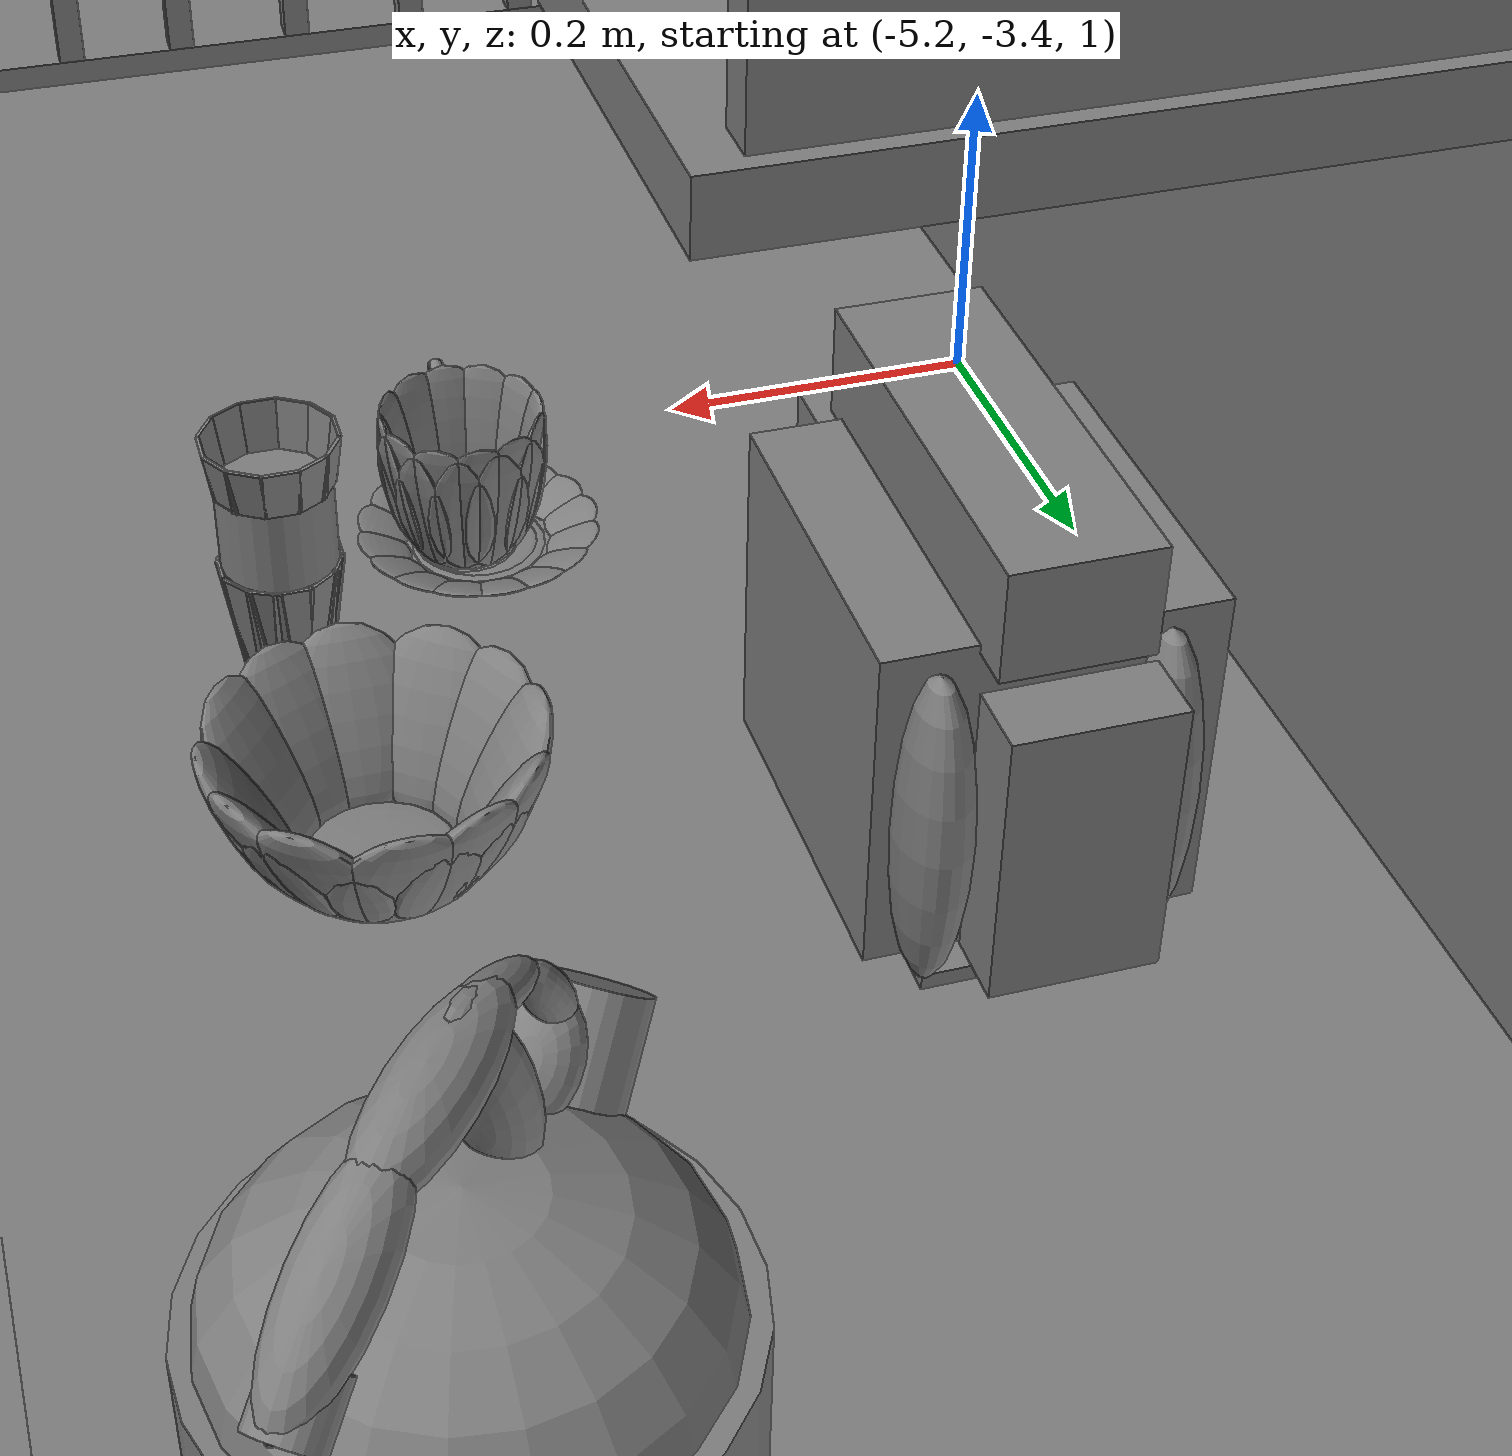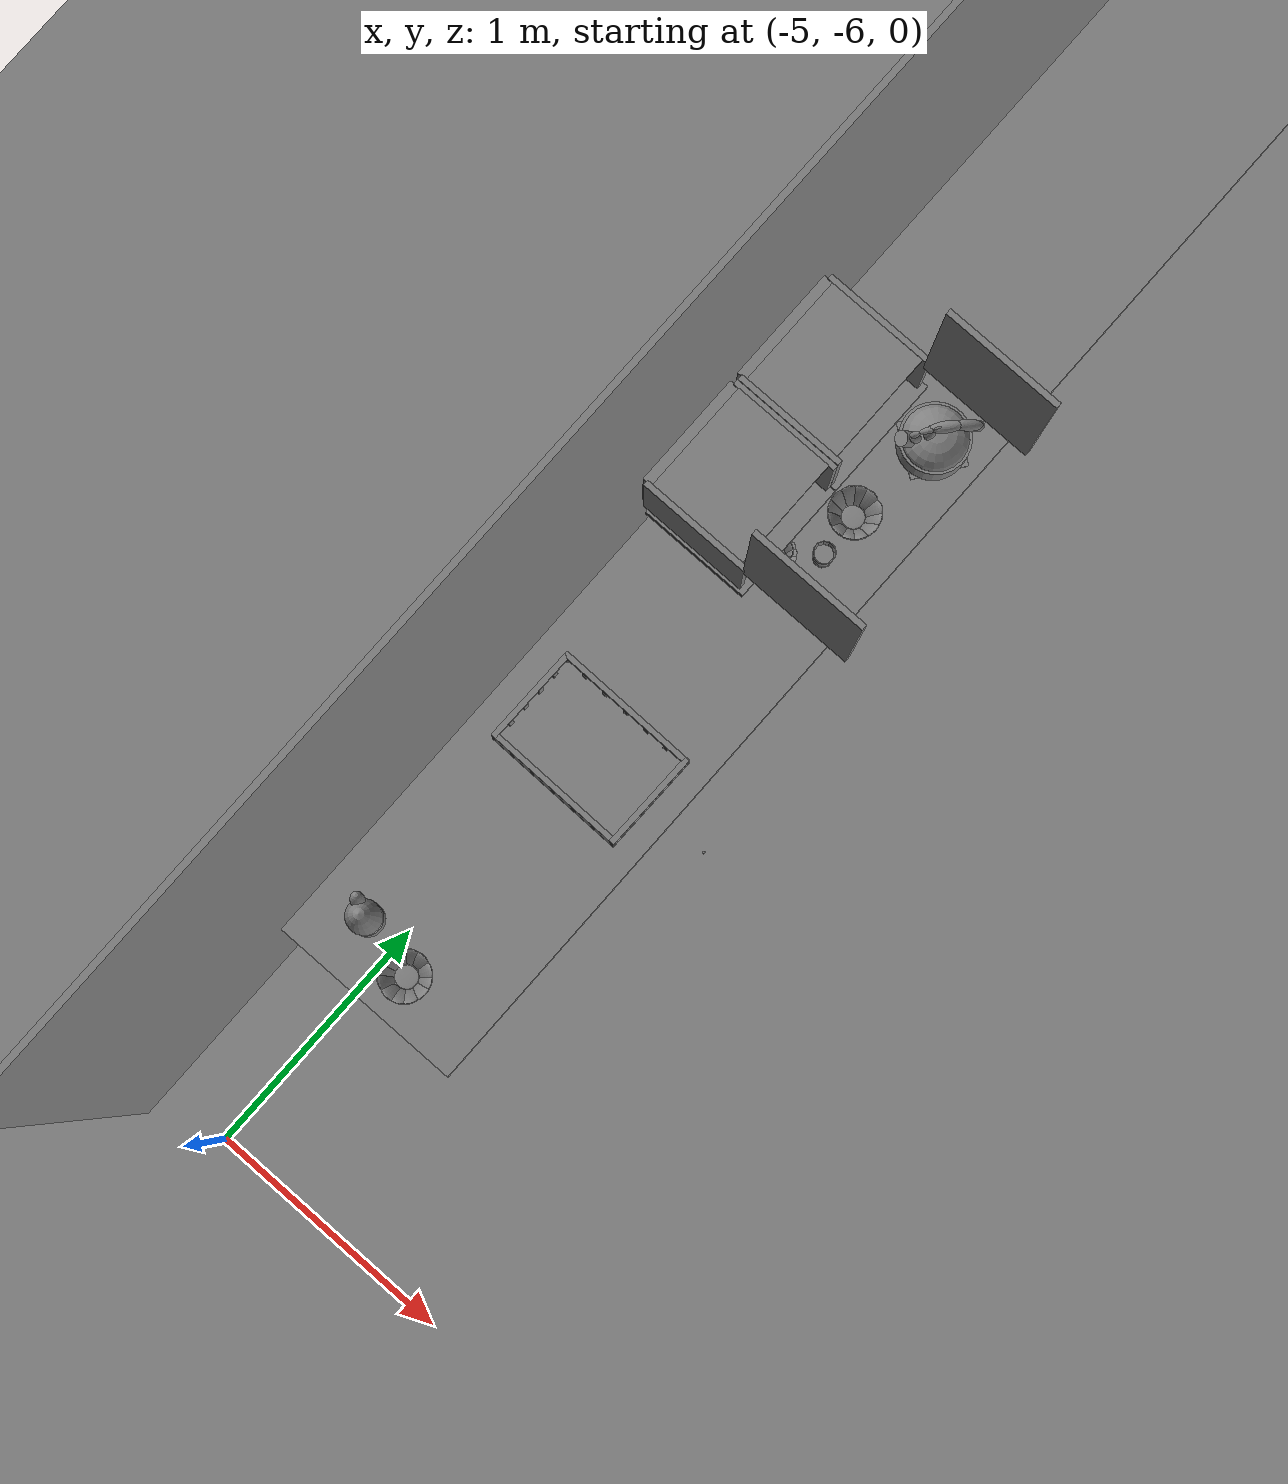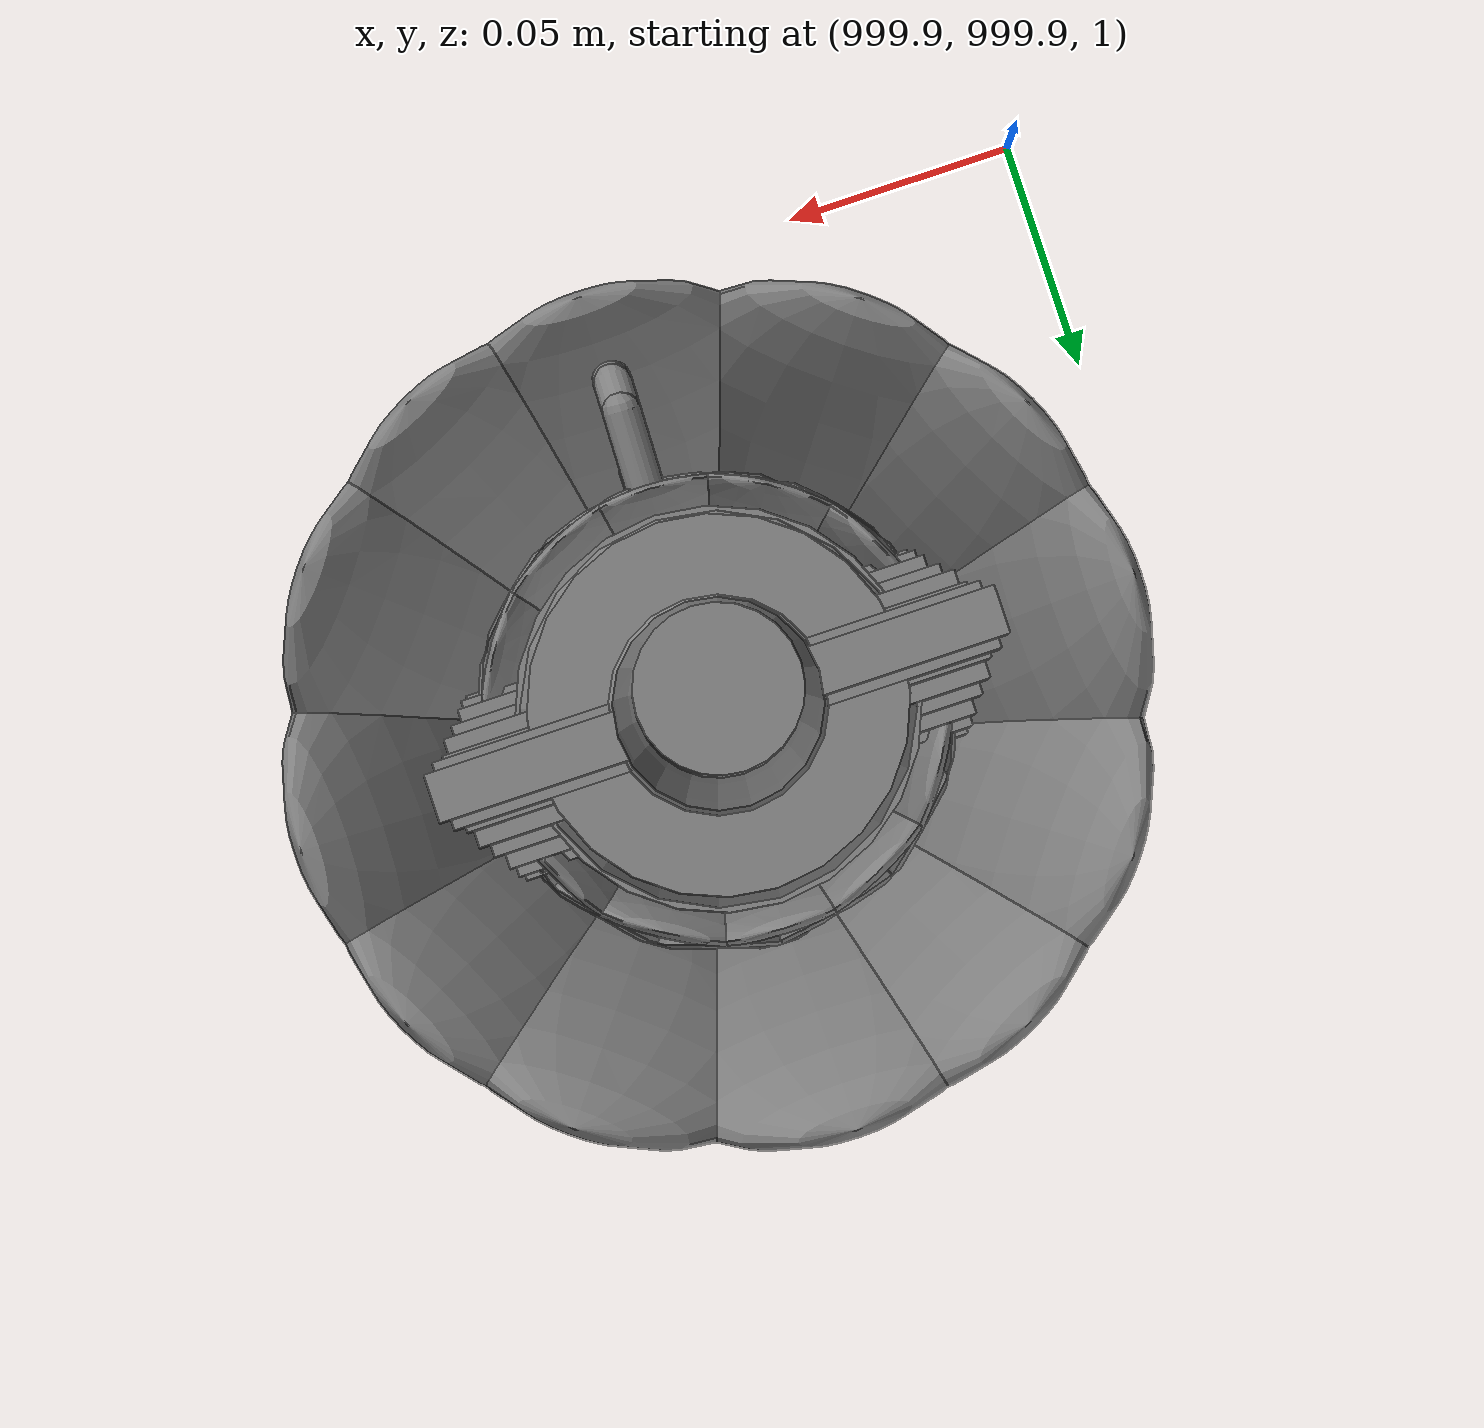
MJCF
<mujoco>
    <option gravity="0.000000000 0.000000000 -9.810000420" timestep="0.0049999999" integrator="implicitfast" density="9.8000002" viscosity="1.8000001e-05" noslip_iterations="10" iterations="100" sdf_iterations="50">
        <flag multiccd="disable"/>
    </option>
    <size memory="1000M"/>
    <compiler coordinate="local"/>
    <worldbody>
        <light cutoff="30" pos="0 1 1" dir="0 -1 -2"/>
        <light cutoff="30" pos="0 -1 1" dir="0 1 -2"/>
        <body pos="-5.046103477 -5.051773071 1.001502514" euler="0.000000000 0.000000000 0.000000000" name="Interactive Objcets_huapen">
            <geom contype="1" conaffinity="1" density="1000" type="ellipsoid" material="" rgba="0.500000000 0.500000000 0.500000000 1.000000000" solimp="0.899999976 0.949999988 0.001000000" friction="1.000000000 0.005000000 0.000100000" solref="0.020000000 1.000000000" margin="0" condim="3" group="0" pos="0.008062840 0.004346371 0.205056787" quat="1.000000000 0.000000000 0.000000000 0.000000000" size="0.059999999 0.059999999 0.180000007" name="Interactive Objcets_huapen_hua_611E910A_A6CF_43B2_A93A_80B6F3F6FEE0"/>
            <geom contype="1" conaffinity="1" density="1000" type="box" material="" rgba="0.500000000 0.500000000 0.500000000 1.000000000" solimp="0.899999976 0.949999988 0.001000000" friction="1.000000000 0.005000000 0.000100000" solref="0.020000000 1.000000000" margin="0" condim="3" group="0" pos="0.008062840 0.003952503 0.020566106" quat="1.000000000 0.000000000 0.000000000 0.000000000" size="0.035000000 0.035000000 0.020000000" name="Interactive Objcets_huapen_hua_B6C2816B_9B1D_4EB2_B2C8_13BA42B13327"/>
            <geom contype="1" conaffinity="1" density="1000" type="cylinder" material="" rgba="0.500000000 0.500000000 0.500000000 1.000000000" solimp="0.899999976 0.949999988 0.001000000" friction="1.000000000 0.005000000 0.000100000" solref="0.020000000 1.000000000" margin="0" condim="3" group="0" pos="0.008062840 0.003952026 0.080107450" quat="1.000000000 0.000000000 0.000000000 0.000000000" size="0.057999998 0.039999999 1.000000000" name="Interactive Objcets_huapen_hua_B2F5C7D4_C426_4E77_B1EB_1FF5BA3343EC"/>
            <geom contype="1" conaffinity="1" density="1000" type="ellipsoid" material="" rgba="0.500000000 0.500000000 0.500000000 1.000000000" solimp="0.899999976 0.949999988 0.001000000" friction="1.000000000 0.005000000 0.000100000" solref="0.020000000 1.000000000" margin="0" condim="3" group="0" pos="-0.029900074 0.033599377 0.321917295" quat="0.992658079 -0.083605267 -0.087364964 0.002748166" size="0.025000000 0.025000000 0.059999999" name="Interactive Objcets_huapen_hua_0B1EBF9D_0559_4D55_806B_7E3D16EC3DEB"/>
            <freejoint name="Interactive Objcets_huapen"/>
        </body>
        <body pos="-4.090442181 -3.819912672 1.779291034" euler="-18.599159241 72.298736572 72.079238892" mocap="true" name="spotlight3_SpotLight"/>
        <body pos="1000.000000000 1000.000000000 1.000000000" euler="0.000000000 0.000000000 0.000000000" name="openloong_gripper_2f85_fix_base_usda_jar_01">
            <geom contype="1" conaffinity="1" density="1000" type="box" material="" rgba="0.500000000 0.500000000 0.500000000 1.000000000" solimp="0.899999976 0.949999988 0.001000000" friction="1.000000000 0.005000000 0.000100000" solref="0.020000000 1.000000000" margin="0" condim="3" group="0" pos="0.000000000 0.000000000 0.006158113" quat="1.000000000 0.000000000 0.000000000 0.000000000" size="0.020000000 0.020000000 0.005000000" name="openloong_gripper_2f85_fix_base_usda_geom_DA4E7205_36D8_469E_9578_9AF3F3144FA2"/>
            <geom contype="1" conaffinity="1" density="1000" type="cylinder" material="" rgba="0.500000000 0.500000000 0.500000000 1.000000000" solimp="0.899999976 0.949999988 0.001000000" friction="1.000000000 0.005000000 0.000100000" solref="0.020000000 1.000000000" margin="0" condim="3" group="0" pos="0.000000000 0.000000000 0.062744498" quat="1.000000000 0.000000000 0.000000000 0.000000000" size="0.041000001 0.052999999 1.000000000" name="openloong_gripper_2f85_fix_base_usda_geom_70F0D93B_C259_4B54_969C_98299248C5AA"/>
            <geom contype="1" conaffinity="1" density="1000" type="ellipsoid" material="" rgba="0.500000000 0.500000000 0.500000000 1.000000000" solimp="0.899999976 0.949999988 0.001000000" friction="1.000000000 0.005000000 0.000100000" solref="0.020000000 1.000000000" margin="0" condim="3" group="0" pos="0.000000000 0.000000000 0.122252703" quat="1.000000000 0.000000000 0.000000000 0.000000000" size="0.035999998 0.035999998 0.010000000" name="openloong_gripper_2f85_fix_base_usda_geom_2EDFA397_3CBF_4EE7_AAE1_FF0607A286B4"/>
            <geom contype="1" conaffinity="1" density="1000" type="cylinder" material="" rgba="0.500000000 0.500000000 0.500000000 1.000000000" solimp="0.899999976 0.949999988 0.001000000" friction="1.000000000 0.005000000 0.000100000" solref="0.020000000 1.000000000" margin="0" condim="3" group="0" pos="0.000000000 0.000000000 0.015747190" quat="1.000000000 0.000000000 0.000000000 0.000000000" size="0.035000000 0.010000000 1.000000000" name="openloong_gripper_2f85_fix_base_usda_geom_E7BC205B_F7F0_497A_BF01_8015ED58DFB6"/>
            <geom contype="1" conaffinity="1" density="1000" type="ellipsoid" material="" rgba="0.500000000 0.500000000 0.500000000 1.000000000" solimp="0.899999976 0.949999988 0.001000000" friction="1.000000000 0.005000000 0.000100000" solref="0.020000000 1.000000000" margin="0" condim="3" group="0" pos="0.000000000 0.000000000 0.115815401" quat="1.000000000 0.000000000 0.000000000 0.000000000" size="0.039999999 0.039999999 0.010000000" name="openloong_gripper_2f85_fix_base_usda_geom_B9C6F741_E724_4983_B98D_9FE563D9EEFA"/>
            <geom contype="1" conaffinity="1" density="1000" type="cylinder" material="" rgba="0.500000000 0.500000000 0.500000000 1.000000000" solimp="0.899999976 0.949999988 0.001000000" friction="1.000000000 0.005000000 0.000100000" solref="0.020000000 1.000000000" margin="0" condim="3" group="0" pos="0.000000000 0.000000000 0.133183479" quat="1.000000000 0.000000000 0.000000000 0.000000000" size="0.037999999 0.006500000 1.000000000" name="openloong_gripper_2f85_fix_base_usda_geom_C538582B_A919_49E7_8F22_516A0BA78EA1"/>
            <freejoint name="openloong_gripper_2f85_fix_base_usda_jar_01_joint"/>
            <site size="0.005000000 0.005000000 0.005000000" rgba="0.500000000 0.500000000 0.500000000 1.000000000" pos="0.000000000 0.000000000 0.000000000" quat="1.000000000 0.000000000 0.000000000 0.000000000" group="0" type="sphere" name="openloong_gripper_2f85_fix_base_usda_jar_01site"/>
        </body>
        <body pos="1000.000000000 1000.000000000 1.000000000" euler="0.000000000 0.000000000 0.000000000" name="openloong_gripper_2f85_fix_base_usda_salt">
            <geom contype="1" conaffinity="1" density="1000" type="box" material="" rgba="0.500000000 0.500000000 0.500000000 1.000000000" solimp="0.899999976 0.949999988 0.001000000" friction="1.000000000 0.005000000 0.000100000" solref="0.020000000 1.000000000" margin="0" condim="3" group="0" pos="0.000305176 0.000000000 0.084862232" quat="1.000000000 0.000000000 0.000000000 0.000000000" size="0.048999999 0.018999999 0.005000000" name="openloong_gripper_2f85_fix_base_usda_geom_1DE48DD1_B225_46F8_9A4E_909311C0DB26"/>
            <geom contype="1" conaffinity="1" density="1000" type="box" material="" rgba="0.500000000 0.500000000 0.500000000 1.000000000" solimp="0.899999976 0.949999988 0.001000000" friction="1.000000000 0.005000000 0.000100000" solref="0.020000000 1.000000000" margin="0" condim="3" group="0" pos="0.000305176 0.000000000 0.104564309" quat="1.000000000 0.000000000 0.000000000 0.000000000" size="0.052000001 0.014000000 0.005000000" name="openloong_gripper_2f85_fix_base_usda_geom_E8039C4A_1978_4CCC_9D83_DCE0800D5B92"/>
            <geom contype="1" conaffinity="1" density="1000" type="box" material="" rgba="0.500000000 0.500000000 0.500000000 1.000000000" solimp="0.899999976 0.949999988 0.001000000" friction="1.000000000 0.005000000 0.000100000" solref="0.020000000 1.000000000" margin="0" condim="3" group="0" pos="0.000305176 0.000000000 0.114487171" quat="1.000000000 0.000000000 0.000000000 0.000000000" size="0.054000001 0.011500000 0.005000000" name="openloong_gripper_2f85_fix_base_usda_geom_3D30742C_A20C_4D10_8F27_8FE7AE6248AA"/>
            <geom contype="1" conaffinity="1" density="1000" type="box" material="" rgba="0.500000000 0.500000000 0.500000000 1.000000000" solimp="0.899999976 0.949999988 0.001000000" friction="1.000000000 0.005000000 0.000100000" solref="0.020000000 1.000000000" margin="0" condim="3" group="0" pos="0.000305176 0.000000000 0.075103164" quat="1.000000000 0.000000000 0.000000000 0.000000000" size="0.048000000 0.020000000 0.005000000" name="openloong_gripper_2f85_fix_base_usda_geom_4D59D02D_D518_4BE8_99B3_5754BB3D7033"/>
            <geom contype="1" conaffinity="1" density="1000" type="box" material="" rgba="0.500000000 0.500000000 0.500000000 1.000000000" solimp="0.899999976 0.949999988 0.001000000" friction="1.000000000 0.005000000 0.000100000" solref="0.020000000 1.000000000" margin="0" condim="3" group="0" pos="0.000305176 0.000000000 0.134892464" quat="1.000000000 0.000000000 0.000000000 0.000000000" size="0.057000000 0.007000000 0.005000000" name="openloong_gripper_2f85_fix_base_usda_geom_BF14544A_8C80_4B36_A802_A53A7C219D4B"/>
            <geom contype="1" conaffinity="1" density="1000" type="box" material="" rgba="0.500000000 0.500000000 0.500000000 1.000000000" solimp="0.899999976 0.949999988 0.001000000" friction="1.000000000 0.005000000 0.000100000" solref="0.020000000 1.000000000" margin="0" condim="3" group="0" pos="0.000305176 0.000000000 0.094920278" quat="1.000000000 0.000000000 0.000000000 0.000000000" size="0.050000001 0.017000001 0.005000000" name="openloong_gripper_2f85_fix_base_usda_geom_5252100C_500A_45A0_B458_B7F47F785DD2"/>
            <geom contype="1" conaffinity="1" density="1000" type="box" material="" rgba="0.500000000 0.500000000 0.500000000 1.000000000" solimp="0.899999976 0.949999988 0.001000000" friction="1.000000000 0.005000000 0.000100000" solref="0.020000000 1.000000000" margin="0" condim="3" group="0" pos="0.000305176 0.000000000 0.065204859" quat="1.000000000 0.000000000 0.000000000 0.000000000" size="0.045000002 0.021000000 0.005000000" name="openloong_gripper_2f85_fix_base_usda_geom_BE07D90C_3A95_4FCA_8DFA_917CC442F346"/>
            <geom contype="1" conaffinity="1" density="1000" type="box" material="" rgba="0.500000000 0.500000000 0.500000000 1.000000000" solimp="0.899999976 0.949999988 0.001000000" friction="1.000000000 0.005000000 0.000100000" solref="0.020000000 1.000000000" margin="0" condim="3" group="0" pos="0.000305176 0.000000000 0.144135714" quat="1.000000000 0.000000000 0.000000000 0.000000000" size="0.059000000 0.005000000 0.004000000" name="openloong_gripper_2f85_fix_base_usda_geom_EEB0CCF2_34AB_45FB_A3FA_7EBAD2C239B0"/>
            <geom contype="1" conaffinity="1" density="1000" type="box" material="" rgba="0.500000000 0.500000000 0.500000000 1.000000000" solimp="0.899999976 0.949999988 0.001000000" friction="1.000000000 0.005000000 0.000100000" solref="0.020000000 1.000000000" margin="0" condim="3" group="0" pos="0.000000000 0.000000000 0.031593561" quat="1.000000000 0.000000000 0.000000000 0.000000000" size="0.041999999 0.024000000 0.029999999" name="openloong_gripper_2f85_fix_base_usda_geom_2FD620C0_105F_4291_AE68_F91BA9899FD0"/>
            <geom contype="1" conaffinity="1" density="1000" type="box" material="" rgba="0.500000000 0.500000000 0.500000000 1.000000000" solimp="0.899999976 0.949999988 0.001000000" friction="1.000000000 0.005000000 0.000100000" solref="0.020000000 1.000000000" margin="0" condim="3" group="0" pos="0.000305176 0.000000000 0.124608755" quat="1.000000000 0.000000000 0.000000000 0.000000000" size="0.055000000 0.008000000 0.005000000" name="openloong_gripper_2f85_fix_base_usda_geom_50BF2FC0_2E29_43AE_A432_CFE4DF6486A4"/>
            <freejoint name="openloong_gripper_2f85_fix_base_usda_salt_joint"/>
            <site size="0.005000000 0.005000000 0.005000000" rgba="0.500000000 0.500000000 0.500000000 1.000000000" pos="0.000000000 0.000000000 0.000000000" quat="1.000000000 0.000000000 0.000000000 0.000000000" group="0" type="sphere" name="openloong_gripper_2f85_fix_base_usda_saltsite"/>
        </body>
        <body pos="1000.000000000 1000.000000000 1.000000000" euler="0.000000000 0.000000000 0.000000000" name="openloong_gripper_2f85_fix_base_usda_bow_yellow_kps">
            <geom contype="1" conaffinity="1" density="1000" type="ellipsoid" material="" rgba="0.500000000 0.500000000 0.500000000 1.000000000" solimp="0.899999976 0.949999988 0.001000000" friction="1.000000000 0.005000000 0.000100000" solref="0.020000000 1.000000000" margin="0" condim="3" group="0" pos="-0.052185059 0.040283203 0.044118762" quat="0.919264615 -0.076883033 -0.225593656 -0.313287765" size="0.010000000 0.039999999 0.052000001" name="openloong_gripper_2f85_fix_base_usda_geom_C56302F4_DD11_4A8B_ADD7_EA2E5D7FDF1A"/>
            <geom contype="1" conaffinity="1" density="1000" type="ellipsoid" material="" rgba="0.500000000 0.500000000 0.500000000 1.000000000" solimp="0.899999976 0.949999988 0.001000000" friction="1.000000000 0.005000000 0.000100000" solref="0.020000000 1.000000000" margin="0" condim="3" group="0" pos="-0.000061035 0.065979004 0.044118762" quat="0.687598765 -0.168314874 -0.168741167 -0.685860336" size="0.010000000 0.039999999 0.052000001" name="openloong_gripper_2f85_fix_base_usda_geom_919779B6_A027_4A1B_8071_9CA0C4AE6419"/>
            <geom contype="1" conaffinity="1" density="1000" type="box" material="" rgba="0.500000000 0.500000000 0.500000000 1.000000000" solimp="0.899999976 0.949999988 0.001000000" friction="1.000000000 0.005000000 0.000100000" solref="0.020000000 1.000000000" margin="0" condim="3" group="0" pos="0.000061035 0.000000000 -0.002001643" quat="1.000000000 0.000000000 0.000000000 0.000000000" size="0.029999999 0.029999999 0.002000000" name="openloong_gripper_2f85_fix_base_usda_geom_8659C729_DE97_4138_B200_DD8815287968"/>
            <geom contype="1" conaffinity="1" density="1000" type="ellipsoid" material="" rgba="0.500000000 0.500000000 0.500000000 1.000000000" solimp="0.899999976 0.949999988 0.001000000" friction="1.000000000 0.005000000 0.000100000" solref="0.020000000 1.000000000" margin="0" condim="3" group="0" pos="0.029418945 -0.059082031 0.044118762" quat="0.825555861 0.125530601 0.202597082 -0.511521280" size="0.010000000 0.039999999 0.052000001" name="openloong_gripper_2f85_fix_base_usda_geom_847F9FE6_987A_4768_B4E6_397BC1F06083"/>
            <geom contype="1" conaffinity="1" density="1000" type="ellipsoid" material="" rgba="0.500000000 0.500000000 0.500000000 1.000000000" solimp="0.899999976 0.949999988 0.001000000" friction="1.000000000 0.005000000 0.000100000" solref="0.020000000 1.000000000" margin="0" condim="3" group="0" pos="0.000244141 -0.065979004 0.044118762" quat="0.687598765 0.168314651 0.168741375 -0.685860336" size="0.010000000 0.039999999 0.052000001" name="openloong_gripper_2f85_fix_base_usda_geom_982F3CD8_77C5_471C_A88A_0006417CE1A1"/>
            <geom contype="1" conaffinity="1" density="1000" type="ellipsoid" material="" rgba="0.500000000 0.500000000 0.500000000 1.000000000" solimp="0.899999976 0.949999988 0.001000000" friction="1.000000000 0.005000000 0.000100000" solref="0.020000000 1.000000000" margin="0" condim="3" group="0" pos="0.000061035 0.000000000 0.000446677" quat="1.000000000 0.000000000 0.000000000 0.000000000" size="0.039999999 0.039999999 0.002000000" name="openloong_gripper_2f85_fix_base_usda_geom_9B31D147_9FCE_46C0_A9A4_4FBBF7448D8C"/>
            <geom contype="1" conaffinity="1" density="1000" type="ellipsoid" material="" rgba="0.500000000 0.500000000 0.500000000 1.000000000" solimp="0.899999976 0.949999988 0.001000000" friction="1.000000000 0.005000000 0.000100000" solref="0.020000000 1.000000000" margin="0" condim="3" group="0" pos="0.059082031 0.029541016 0.044118762" quat="0.223252773 -0.231952220 -0.054787423 -0.945174456" size="0.010000000 0.039999999 0.052000001" name="openloong_gripper_2f85_fix_base_usda_geom_644F8D32_E00B_4E1A_B2D3_F623BB95594B"/>
            <geom contype="1" conaffinity="1" density="1000" type="ellipsoid" material="" rgba="0.500000000 0.500000000 0.500000000 1.000000000" solimp="0.899999976 0.949999988 0.001000000" friction="1.000000000 0.005000000 0.000100000" solref="0.020000000 1.000000000" margin="0" condim="3" group="0" pos="0.000061035 0.000000000 0.007335305" quat="1.000000000 0.000000000 0.000000000 0.000000000" size="0.039999999 0.039999999 0.002000000" name="openloong_gripper_2f85_fix_base_usda_geom_AF5BDBC0_F1B9_47EC_A91C_7C5AF4CE46BA"/>
            <geom contype="1" conaffinity="1" density="1000" type="ellipsoid" material="" rgba="0.500000000 0.500000000 0.500000000 1.000000000" solimp="0.899999976 0.949999988 0.001000000" friction="1.000000000 0.005000000 0.000100000" solref="0.020000000 1.000000000" margin="0" condim="3" group="0" pos="-0.029296875 0.059082031 0.044118762" quat="0.825555861 -0.125530809 -0.202596918 -0.511521280" size="0.010000000 0.039999999 0.052000001" name="openloong_gripper_2f85_fix_base_usda_geom_22C28B39_DAEF_49FA_9FE2_8A27D8B73BD9"/>
            <geom contype="1" conaffinity="1" density="1000" type="ellipsoid" material="" rgba="0.500000000 0.500000000 0.500000000 1.000000000" solimp="0.899999976 0.949999988 0.001000000" friction="1.000000000 0.005000000 0.000100000" solref="0.020000000 1.000000000" margin="0" condim="3" group="0" pos="0.040222168 0.052368164 0.044118762" quat="0.429593176 -0.213750049 -0.105424821 -0.871002972" size="0.010000000 0.039999999 0.052000001" name="openloong_gripper_2f85_fix_base_usda_geom_912CB8CD_E1B9_46F4_9300_9C2AAA59DCC4"/>
            <geom contype="1" conaffinity="1" density="1000" type="ellipsoid" material="" rgba="0.500000000 0.500000000 0.500000000 1.000000000" solimp="0.899999976 0.949999988 0.001000000" friction="1.000000000 0.005000000 0.000100000" solref="0.020000000 1.000000000" margin="0" condim="3" group="0" pos="0.066040039 0.000000000 0.044118762" quat="0.971183062 -0.000000156 0.238334835 0.000000030" size="0.010000000 0.039999999 0.052000001" name="openloong_gripper_2f85_fix_base_usda_geom_BF3069FF_C810_4C31_9E5A_D4C73C9DC979"/>
            <geom contype="1" conaffinity="1" density="1000" type="ellipsoid" material="" rgba="0.500000000 0.500000000 0.500000000 1.000000000" solimp="0.899999976 0.949999988 0.001000000" friction="1.000000000 0.005000000 0.000100000" solref="0.020000000 1.000000000" margin="0" condim="3" group="0" pos="0.052307129 -0.040283203 0.044118762" quat="0.919264674 0.076882750 0.225593731 -0.313287705" size="0.010000000 0.039999999 0.052000001" name="openloong_gripper_2f85_fix_base_usda_geom_DAF603AC_432B_414E_A940_E60D80871887"/>
            <geom contype="1" conaffinity="1" density="1000" type="ellipsoid" material="" rgba="0.500000000 0.500000000 0.500000000 1.000000000" solimp="0.899999976 0.949999988 0.001000000" friction="1.000000000 0.005000000 0.000100000" solref="0.020000000 1.000000000" margin="0" condim="3" group="0" pos="-0.065917969 0.000000000 0.044118762" quat="0.971183062 -0.000000142 -0.238334835 0.000000030" size="0.010000000 0.039999999 0.052000001" name="openloong_gripper_2f85_fix_base_usda_geom_94B6CDD5_29EF_4E71_8C0D_30811B163B2E"/>
            <geom contype="1" conaffinity="1" density="1000" type="ellipsoid" material="" rgba="0.500000000 0.500000000 0.500000000 1.000000000" solimp="0.899999976 0.949999988 0.001000000" friction="1.000000000 0.005000000 0.000100000" solref="0.020000000 1.000000000" margin="0" condim="3" group="0" pos="-0.058898926 -0.029541016 0.044118762" quat="0.223252758 0.231952101 0.054787733 -0.945174575" size="0.010000000 0.039999999 0.052000001" name="openloong_gripper_2f85_fix_base_usda_geom_B3D2F2AE_6332_45C0_8083_814EDC603990"/>
            <geom contype="1" conaffinity="1" density="1000" type="ellipsoid" material="" rgba="0.500000000 0.500000000 0.500000000 1.000000000" solimp="0.899999976 0.949999988 0.001000000" friction="1.000000000 0.005000000 0.000100000" solref="0.020000000 1.000000000" margin="0" condim="3" group="0" pos="-0.040100098 -0.052368164 0.044118762" quat="0.429593235 0.213749886 0.105425082 -0.871003032" size="0.010000000 0.039999999 0.052000001" name="openloong_gripper_2f85_fix_base_usda_geom_E90185B4_FFC7_48C3_8F84_352C8A3A2700"/>
            <freejoint name="openloong_gripper_2f85_fix_base_usda_bow_yellow_kps_joint"/>
            <site size="0.005000000 0.005000000 0.005000000" rgba="0.500000000 0.500000000 0.500000000 1.000000000" pos="0.000000000 0.000000000 0.000000000" quat="0.999961913 0.008726534 0.000000000 0.000000000" group="0" type="sphere" name="openloong_gripper_2f85_fix_base_usda_bow_yellow_kps"/>
        </body>
        <body pos="-4.131280899 -4.385339260 1.916756868" euler="28.934482574 35.173107147 2.246350527" mocap="true" name="spotlight1_SpotLight"/>
        <body pos="-4.450430393 -4.389380932 1.834840775" euler="174.448654175 -49.188316345 -120.899162292" mocap="true" name="spotlight6_SpotLight"/>
        <body pos="1000.000000000 1000.000000000 1.000000000" euler="0.000000000 0.000000000 0.000000000" name="openloong_gripper_2f85_fix_base_usda_coffeecup_white_kps">
            <geom contype="1" conaffinity="1" density="1000" type="capsule" material="" rgba="0.500000000 0.500000000 0.500000000 1.000000000" solimp="0.899999976 0.949999988 0.001000000" friction="1.000000000 0.005000000 0.000100000" solref="0.020000000 1.000000000" margin="0" condim="3" group="0" pos="-0.000854492 -0.065795898 0.050029993" quat="0.343559504 -0.613204718 0.626912475 0.336047262" size="0.004000000 0.005000000 1.000000000" name="openloong_gripper_2f85_fix_base_usda_geom_B2E4E490_57E7_4B81_B9AE_2EB8EAA56978"/>
            <geom contype="1" conaffinity="1" density="1000" type="ellipsoid" material="" rgba="0.500000000 0.500000000 0.500000000 1.000000000" solimp="0.899999976 0.949999988 0.001000000" friction="1.000000000 0.005000000 0.000100000" solref="0.020000000 1.000000000" margin="0" condim="3" group="0" pos="-0.000793457 -0.038452148 0.048040152" quat="0.711656272 0.066323131 -0.067805752 0.696095467" size="0.005000000 0.029999999 0.048999999" name="openloong_gripper_2f85_fix_base_usda_geom_ED1F4255_264A_4282_BAE0_CA3A528CF415"/>
            <geom contype="1" conaffinity="1" density="1000" type="ellipsoid" material="" rgba="0.500000000 0.500000000 0.500000000 1.000000000" solimp="0.899999976 0.949999988 0.001000000" friction="1.000000000 0.005000000 0.000100000" solref="0.020000000 1.000000000" margin="0" condim="3" group="0" pos="0.037719727 -0.001892090 0.048040152" quat="0.995387912 0.001371633 0.094835162 -0.014391154" size="0.005000000 0.029999999 0.048999999" name="openloong_gripper_2f85_fix_base_usda_geom_6715DAEE_F9EA_40E9_BF53_AFE41ADB8FDC"/>
            <geom contype="1" conaffinity="1" density="1000" type="ellipsoid" material="" rgba="0.500000000 0.500000000 0.500000000 1.000000000" solimp="0.899999976 0.949999988 0.001000000" friction="1.000000000 0.005000000 0.000100000" solref="0.020000000 1.000000000" margin="0" condim="3" group="0" pos="0.033996582 0.015502930 0.048040152" quat="0.970659733 -0.021051638 0.092478797 0.220962167" size="0.005000000 0.029999999 0.048999999" name="openloong_gripper_2f85_fix_base_usda_geom_3B4B14B7_EF4B_45D5_AF89_14B4632E617F"/>
            <geom contype="1" conaffinity="1" density="1000" type="box" material="" rgba="0.500000000 0.500000000 0.500000000 1.000000000" solimp="0.899999976 0.949999988 0.001000000" friction="1.000000000 0.005000000 0.000100000" solref="0.020000000 1.000000000" margin="0" condim="3" group="0" pos="0.000793457 -0.000183105 0.000156164" quat="0.714879215 0.000000000 0.000000000 0.699247897" size="0.020000000 0.020000000 0.002000000" name="openloong_gripper_2f85_fix_base_usda_geom_80FD5D99_D15B_4BB5_A1AE_8F78E815A0EE"/>
            <geom contype="1" conaffinity="1" density="1000" type="ellipsoid" material="" rgba="0.500000000 0.500000000 0.500000000 1.000000000" solimp="0.899999976 0.949999988 0.001000000" friction="1.000000000 0.005000000 0.000100000" solref="0.020000000 1.000000000" margin="0" condim="3" group="0" pos="-0.019409180 -0.033081055 0.048040152" quat="0.866879702 0.046630561 -0.082595348 0.489411235" size="0.005000000 0.029999999 0.048999999" name="openloong_gripper_2f85_fix_base_usda_geom_BED0D008_1F6A_4C3C_9AED_779B8A5642D8"/>
            <geom contype="1" conaffinity="1" density="1000" type="ellipsoid" material="" rgba="0.500000000 0.500000000 0.500000000 1.000000000" solimp="0.899999976 0.949999988 0.001000000" friction="1.000000000 0.005000000 0.000100000" solref="0.020000000 1.000000000" margin="0" condim="3" group="0" pos="-0.016052246 0.033264160 0.048040152" quat="0.840792537 -0.050782297 -0.080109790 -0.532983541" size="0.005000000 0.029999999 0.048999999" name="openloong_gripper_2f85_fix_base_usda_geom_02A8030B_2D89_4214_8178_F4B1E60794AE"/>
            <geom contype="1" conaffinity="1" density="1000" type="capsule" material="" rgba="0.500000000 0.500000000 0.500000000 1.000000000" solimp="0.899999976 0.949999988 0.001000000" friction="1.000000000 0.005000000 0.000100000" solref="0.020000000 1.000000000" margin="0" condim="3" group="0" pos="-0.000549316 -0.053527832 0.046825886" quat="0.505496025 -0.494442940 0.505495846 0.494442940" size="0.004000000 0.005000000 1.000000000" name="openloong_gripper_2f85_fix_base_usda_geom_AE015B81_6A9F_4253_83AE_F3CF10AA5F20"/>
            <geom contype="1" conaffinity="1" density="1000" type="ellipsoid" material="" rgba="0.500000000 0.500000000 0.500000000 1.000000000" solimp="0.899999976 0.949999988 0.001000000" friction="1.000000000 0.005000000 0.000100000" solref="0.020000000 1.000000000" margin="0" condim="3" group="0" pos="-0.032104492 0.018920898 0.048040152" quat="0.958129764 -0.025742561 -0.091288343 -0.270168930" size="0.005000000 0.029999999 0.048999999" name="openloong_gripper_2f85_fix_base_usda_geom_9D62ADC9_24E9_4520_A001_813254ED525B"/>
            <geom contype="1" conaffinity="1" density="1000" type="ellipsoid" material="" rgba="0.500000000 0.500000000 0.500000000 1.000000000" solimp="0.899999976 0.949999988 0.001000000" friction="1.000000000 0.005000000 0.000100000" solref="0.020000000 1.000000000" margin="0" condim="3" group="0" pos="-0.037597656 0.000305176 0.048040152" quat="0.995387554 -0.001371440 -0.094839431 -0.014389008" size="0.005000000 0.029999999 0.048999999" name="openloong_gripper_2f85_fix_base_usda_geom_47BBC9B6_B62B_4142_AE09_6715D028C53F"/>
            <geom contype="1" conaffinity="1" density="1000" type="capsule" material="" rgba="0.500000000 0.500000000 0.500000000 1.000000000" solimp="0.899999976 0.949999988 0.001000000" friction="1.000000000 0.005000000 0.000100000" solref="0.020000000 1.000000000" margin="0" condim="3" group="0" pos="-0.000366211 -0.043762207 0.044118762" quat="0.260488123 -0.651174724 0.665731549 0.254792154" size="0.004000000 0.003000000 1.000000000" name="openloong_gripper_2f85_fix_base_usda_geom_69F7C6DE_1A59_473D_856B_91E4A91D2313"/>
            <geom contype="1" conaffinity="1" density="1000" type="capsule" material="" rgba="0.500000000 0.500000000 0.500000000 1.000000000" solimp="0.899999976 0.949999988 0.001000000" friction="1.000000000 0.005000000 0.000100000" solref="0.020000000 1.000000000" margin="0" condim="3" group="0" pos="-0.000915527 -0.068542480 0.082936406" quat="0.624995589 -0.339446366 0.347034454 0.611329615" size="0.004000000 0.004000000 1.000000000" name="openloong_gripper_2f85_fix_base_usda_geom_66273982_5068_4E44_A780_5CBD2557E435"/>
            <geom contype="1" conaffinity="1" density="1000" type="ellipsoid" material="" rgba="0.500000000 0.500000000 0.500000000 1.000000000" solimp="0.899999976 0.949999988 0.001000000" friction="1.000000000 0.005000000 0.000100000" solref="0.020000000 1.000000000" margin="0" condim="3" group="0" pos="0.016113281 -0.034851074 0.048040152" quat="0.840793252 0.050779939 0.080106191 -0.532983422" size="0.005000000 0.029999999 0.048999999" name="openloong_gripper_2f85_fix_base_usda_geom_19F696E1_84C8_4200_9A3C_0FCA4722D61E"/>
            <geom contype="1" conaffinity="1" density="1000" type="ellipsoid" material="" rgba="0.500000000 0.500000000 0.500000000 1.000000000" solimp="0.899999976 0.949999988 0.001000000" friction="1.000000000 0.005000000 0.000100000" solref="0.020000000 1.000000000" margin="0" condim="3" group="0" pos="0.000854492 0.036865234 0.048040152" quat="0.711656570 -0.066320375 0.067802906 0.696095705" size="0.005000000 0.029999999 0.048999999" name="openloong_gripper_2f85_fix_base_usda_geom_D421EA09_CC8D_41D7_B229_B6186F2FC79E"/>
            <geom contype="1" conaffinity="1" density="1000" type="ellipsoid" material="" rgba="0.500000000 0.500000000 0.500000000 1.000000000" solimp="0.899999976 0.949999988 0.001000000" friction="1.000000000 0.005000000 0.000100000" solref="0.020000000 1.000000000" margin="0" condim="3" group="0" pos="-0.033935547 -0.017089844 0.048040152" quat="0.970659137 0.021052625 -0.092483103 0.220962465" size="0.005000000 0.029999999 0.048999999" name="openloong_gripper_2f85_fix_base_usda_geom_FC9484CE_B957_40E6_9141_228D06ECFB6C"/>
            <geom contype="1" conaffinity="1" density="1000" type="ellipsoid" material="" rgba="0.500000000 0.500000000 0.500000000 1.000000000" solimp="0.899999976 0.949999988 0.001000000" friction="1.000000000 0.005000000 0.000100000" solref="0.020000000 1.000000000" margin="0" condim="3" group="0" pos="0.019531250 0.031494141 0.048040152" quat="0.866880119 -0.046628602 0.082591817 0.489411235" size="0.005000000 0.029999999 0.048999999" name="openloong_gripper_2f85_fix_base_usda_geom_C9BD5DE3_1B68_4170_9133_64D5DD758590"/>
            <geom contype="1" conaffinity="1" density="1000" type="ellipsoid" material="" rgba="0.500000000 0.500000000 0.500000000 1.000000000" solimp="0.899999976 0.949999988 0.001000000" friction="1.000000000 0.005000000 0.000100000" solref="0.020000000 1.000000000" margin="0" condim="3" group="0" pos="0.032165527 -0.020507812 0.048040152" quat="0.958128154 0.025740955 0.091285400 -0.270175666" size="0.005000000 0.029999999 0.048999999" name="openloong_gripper_2f85_fix_base_usda_geom_12EAA264_4FC3_4FD5_9340_669A4EA181BA"/>
            <geom contype="1" conaffinity="1" density="1000" type="capsule" material="" rgba="0.500000000 0.500000000 0.500000000 1.000000000" solimp="0.899999976 0.949999988 0.001000000" friction="1.000000000 0.005000000 0.000100000" solref="0.020000000 1.000000000" margin="0" condim="3" group="0" pos="-0.000610352 -0.056823730 0.083572865" quat="0.452654332 -0.541215360 0.553313971 0.442756712" size="0.004000000 0.009000000 1.000000000" name="openloong_gripper_2f85_fix_base_usda_geom_A7A16954_36AC_42C4_8FB4_521DDFAE3AC1"/>
            <geom contype="1" conaffinity="1" density="1000" type="ellipsoid" material="" rgba="0.500000000 0.500000000 0.500000000 1.000000000" solimp="0.899999976 0.949999988 0.001000000" friction="1.000000000 0.005000000 0.000100000" solref="0.020000000 1.000000000" margin="0" condim="3" group="0" pos="0.000061035 -0.000183105 0.001848221" quat="0.714879215 0.000000000 0.000000000 0.699247897" size="0.029999999 0.029999999 0.001000000" name="openloong_gripper_2f85_fix_base_usda_geom_B967D431_4994_4E59_A2DD_C467242F4214"/>
            <geom contype="1" conaffinity="1" density="1000" type="capsule" material="" rgba="0.500000000 0.500000000 0.500000000 1.000000000" solimp="0.899999976 0.949999988 0.001000000" friction="1.000000000 0.005000000 0.000100000" solref="0.020000000 1.000000000" margin="0" condim="3" group="0" pos="-0.000976562 -0.071838379 0.066101432" quat="0.031849027 -0.698553741 0.714169443 0.031152546" size="0.004000000 0.012000000 1.000000000" name="openloong_gripper_2f85_fix_base_usda_geom_AFE1C0A2_4511_428D_9DFB_16FBD95F96C7"/>
            <freejoint name="openloong_gripper_2f85_fix_base_usda_coffeecup_white_kps_joint"/>
            <site size="0.005000000 0.005000000 0.005000000" rgba="0.500000000 0.500000000 0.500000000 1.000000000" pos="0.000000000 0.000000000 0.000000000" quat="0.999961913 0.008726534 0.000000000 0.000000000" group="0" type="sphere" name="openloong_gripper_2f85_fix_base_usda_coffeecup_white_kps"/>
        </body>
        <body pos="1000.000000000 1000.000000000 1.000000000" euler="0.000000000 0.000000000 0.000000000" name="openloong_gripper_2f85_fix_base_usda_bottle_red">
            <geom contype="1" conaffinity="1" density="1000" type="ellipsoid" material="" rgba="0.500000000 0.500000000 0.500000000 1.000000000" solimp="0.899999976 0.949999988 0.001000000" friction="1.000000000 0.005000000 0.000100000" solref="0.020000000 1.000000000" margin="0" condim="3" group="0" pos="0.000000000 0.000000000 0.144284487" quat="1.000000000 0.000000000 0.000000000 0.000000000" size="0.021000000 0.021000000 0.079999998" name="openloong_gripper_2f85_fix_base_usda_geom_ED350C87_884F_4DEF_9A45_AEE8CC952776"/>
            <geom contype="1" conaffinity="1" density="1000" type="cylinder" material="" rgba="0.500000000 0.500000000 0.500000000 1.000000000" solimp="0.899999976 0.949999988 0.001000000" friction="1.000000000 0.005000000 0.000100000" solref="0.020000000 1.000000000" margin="0" condim="3" group="0" pos="0.000000000 0.000000000 0.220618963" quat="1.000000000 0.000000000 0.000000000 0.000000000" size="0.016000001 0.010000000 1.000000000" name="openloong_gripper_2f85_fix_base_usda_geom_D8187A5A_5B56_4693_AA29_446664948959"/>
            <geom contype="1" conaffinity="1" density="1000" type="ellipsoid" material="" rgba="0.500000000 0.500000000 0.500000000 1.000000000" solimp="0.899999976 0.949999988 0.001000000" friction="1.000000000 0.005000000 0.000100000" solref="0.020000000 1.000000000" margin="0" condim="3" group="0" pos="0.000000000 0.000000000 0.118945479" quat="1.000000000 0.000000000 0.000000000 0.000000000" size="0.030999999 0.030999999 0.029999999" name="openloong_gripper_2f85_fix_base_usda_geom_85591A0F_C3A6_4F16_BEC7_B5ED798CD8D3"/>
            <geom contype="1" conaffinity="1" density="1000" type="box" material="" rgba="0.500000000 0.500000000 0.500000000 1.000000000" solimp="0.899999976 0.949999988 0.001000000" friction="1.000000000 0.005000000 0.000100000" solref="0.020000000 1.000000000" margin="0" condim="3" group="0" pos="0.000000000 0.000000000 0.002189159" quat="1.000000000 0.000000000 0.000000000 0.000000000" size="0.020000000 0.020000000 0.003000000" name="openloong_gripper_2f85_fix_base_usda_geom_605B052F_64BB_4009_839F_16F454E2DD71"/>
            <geom contype="1" conaffinity="1" density="1000" type="cylinder" material="" rgba="0.500000000 0.500000000 0.500000000 1.000000000" solimp="0.899999976 0.949999988 0.001000000" friction="1.000000000 0.005000000 0.000100000" solref="0.020000000 1.000000000" margin="0" condim="3" group="0" pos="0.000000000 -0.000366211 0.060884237" quat="1.000000000 0.000000000 0.000000000 0.000000000" size="0.030999999 0.057999998 1.000000000" name="openloong_gripper_2f85_fix_base_usda_geom_35156E45_0A68_4D0C_B559_4B9AE341E672"/>
            <freejoint name="openloong_gripper_2f85_fix_base_usda_bottle_red_joint"/>
            <site size="0.005000000 0.005000000 0.005000000" rgba="0.500000000 0.500000000 0.500000000 1.000000000" pos="0.000000000 0.000000000 0.000000000" quat="0.999961913 0.008726535 0.000000000 0.000000000" group="0" type="sphere" name="openloong_gripper_2f85_fix_base_usda_bottle_redsite"/>
        </body>
        <body pos="0.000000000 0.000000000 0.000000000" euler="0.000000000 0.000000000 0.000000000" name="Static Objcets_Static Objcets">
            <geom contype="1" conaffinity="1" density="1000" type="box" material="" rgba="0.500000000 0.500000000 0.500000000 1.000000000" solimp="0.899999976 0.949999988 0.001000000" friction="1.000000000 0.005000000 0.000100000" solref="0.020000000 1.000000000" margin="0" condim="3" group="0" pos="-4.999745846 -3.087441683 1.763863802" quat="0.707107067 0.707106471 0.000000000 0.000000000" size="0.200000003 0.159999996 0.010000000" name="Static Objcets_geom_D6DC67B2_4C9B_48FF_B97B_B1D7C8289463"/>
            <geom contype="1" conaffinity="1" density="1000" type="box" material="" rgba="0.500000000 0.500000000 0.500000000 1.000000000" solimp="0.899999976 0.949999988 0.001000000" friction="1.000000000 0.005000000 0.000100000" solref="0.020000000 1.000000000" margin="0" condim="3" group="0" pos="-5.189302921 -3.293644905 1.760152459" quat="0.707107067 0.707106471 0.000000000 0.000000000" size="0.025000000 0.159999996 0.200000003" name="Static Objcets_geom_F3BE235A_7708_4A73_918B_6F461C5322B6"/>
            <geom contype="1" conaffinity="1" density="1000" type="box" material="" rgba="0.500000000 0.500000000 0.500000000 1.000000000" solimp="0.899999976 0.949999988 0.001000000" friction="1.000000000 0.005000000 0.000100000" solref="0.020000000 1.000000000" margin="0" condim="3" group="0" pos="-4.979488373 -3.297635794 1.591412544" quat="0.707106829 0.707106709 0.000000000 0.000000000" size="0.200000003 0.015000000 0.219999999" name="Static Objcets_geom_74123B58_2193_4DD8_98C9_E549B458F4AD"/>
            <geom contype="1" conaffinity="1" density="1000" type="box" material="" rgba="0.500000000 0.500000000 0.500000000 1.000000000" solimp="0.899999976 0.949999988 0.001000000" friction="1.000000000 0.005000000 0.000100000" solref="0.020000000 1.000000000" margin="0" condim="3" group="0" pos="-4.999745846 -3.497932911 1.764780521" quat="0.707107067 0.707106471 0.000000000 0.000000000" size="0.200000003 0.159999996 0.010000000" name="Static Objcets_geom_39D8F155_ED89_4DEC_AE8B_0AC9DF182098"/>
            <geom contype="1" conaffinity="1" density="1000" type="box" material="" rgba="0.500000000 0.500000000 0.500000000 1.000000000" solimp="0.899999976 0.949999988 0.001000000" friction="1.000000000 0.005000000 0.000100000" solref="0.020000000 1.000000000" margin="0" condim="3" group="0" pos="-5.000125408 -3.294431210 1.913951039" quat="0.707107067 0.707106471 0.000000000 0.000000000" size="0.180000007 0.010000000 0.200000003" name="Static Objcets_geom_3644F842_03BC_46B7_A886_03E8D518F437"/>
            <geom contype="1" conaffinity="1" density="1000" type="box" material="" rgba="0.500000000 0.500000000 0.500000000 1.000000000" solimp="0.899999976 0.949999988 0.001000000" friction="1.000000000 0.005000000 0.000100000" solref="0.020000000 1.000000000" margin="0" condim="3" group="0" pos="-4.999745846 -3.066934109 1.765979409" quat="0.707107067 0.707106471 0.000000000 0.000000000" size="0.200000003 0.159999996 0.010000000" name="Static Objcets_geom_EE4FB303_3833_434A_B94B_80B400CC84C3"/>
            <geom contype="1" conaffinity="1" density="1000" type="box" material="" rgba="0.500000000 0.500000000 0.500000000 1.000000000" solimp="0.899999976 0.949999988 0.001000000" friction="1.000000000 0.005000000 0.000100000" solref="0.020000000 1.000000000" margin="0" condim="3" group="0" pos="-5.189302921 -2.861564636 1.760152102" quat="0.707107067 0.707106471 0.000000000 0.000000000" size="0.025000000 0.159999996 0.200000003" name="Static Objcets_geom_FA380B97_1293_4077_82F9_B0C1A4BC018B"/>
            <geom contype="1" conaffinity="1" density="1000" type="box" material="" rgba="0.500000000 0.500000000 0.500000000 1.000000000" solimp="0.899999976 0.949999988 0.001000000" friction="1.000000000 0.005000000 0.000100000" solref="0.020000000 1.000000000" margin="0" condim="3" group="0" pos="-5.000125408 -2.861802340 1.913950682" quat="0.707107067 0.707106471 0.000000000 0.000000000" size="0.180000007 0.010000000 0.200000003" name="Static Objcets_geom_B07DB55E_2622_4583_9FCE_9DA0F2757B92"/>
            <geom contype="1" conaffinity="1" density="1000" type="box" material="" rgba="0.500000000 0.500000000 0.500000000 1.000000000" solimp="0.899999976 0.949999988 0.001000000" friction="1.000000000 0.005000000 0.000100000" solref="0.020000000 1.000000000" margin="0" condim="3" group="0" pos="-4.979488373 -2.855390549 1.591412187" quat="0.707106709 0.707106769 0.000000000 0.000000000" size="0.200000003 0.015000000 0.219999999" name="Static Objcets_geom_EE20F5C9_DEAE_4A42_820C_A3549B41A0D1"/>
            <geom contype="1" conaffinity="1" density="1000" type="box" material="" rgba="0.500000000 0.500000000 0.500000000 1.000000000" solimp="0.899999976 0.949999988 0.001000000" friction="1.000000000 0.005000000 0.000100000" solref="0.020000000 1.000000000" margin="0" condim="3" group="0" pos="-4.999745846 -2.653569937 1.764779806" quat="0.707107067 0.707106471 0.000000000 0.000000000" size="0.200000003 0.159999996 0.010000000" name="Static Objcets_geom_ABFE137C_BA33_4D3A_A917_AECA3A0A2BF1"/>
            <geom contype="1" conaffinity="1" density="1000" type="box" material="" rgba="0.500000000 0.500000000 0.500000000 1.000000000" solimp="0.899999976 0.949999988 0.001000000" friction="1.000000000 0.005000000 0.000100000" solref="0.020000000 1.000000000" margin="0" condim="3" group="0" pos="-0.720102787 0.222944975 -1.102830648" quat="0.000000954 1.000000000 0.000000000 0.000000000" size="8.000000000 8.000000000 0.010000000" name="Static Objcets_geom_55E4BFD8_B866_407E_B990_CE0F6805C187"/>
            <geom contype="1" conaffinity="1" density="1000" type="box" material="" rgba="0.500000000 0.500000000 0.500000000 1.000000000" solimp="0.899999976 0.949999988 0.001000000" friction="1.000000000 0.005000000 0.000100000" solref="0.020000000 1.000000000" margin="0" condim="3" group="0" pos="-4.873187065 -2.461376429 0.977675021" quat="0.707107067 0.707106471 0.000000000 0.000000000" size="0.370000005 0.029999999 2.799999952" name="Static Objcets_geom_EA50066A_0D7C_4FDD_BF33_110FAAF7AB27"/>
            <geom contype="1" conaffinity="1" density="1000" type="box" material="" rgba="0.500000000 0.500000000 0.500000000 1.000000000" solimp="0.899999976 0.949999988 0.001000000" friction="1.000000000 0.005000000 0.000100000" solref="0.020000000 1.000000000" margin="0" condim="3" group="0" pos="-5.244853973 -2.375543594 1.820221663" quat="0.707107008 0.707106531 0.000000000 0.000000000" size="0.010000000 1.500000000 3.700000048" name="Static Objcets_geom_8E47E2BE_C17F_472C_9EDA_5212B558A779"/>
        </body>
        <body pos="-4.827295780 -3.287638187 1.074643731" euler="0.000000000 0.000000000 89.999992371" name="Interactive Objcets_coffeecup_01">
            <geom contype="1" conaffinity="1" density="1000" type="ellipsoid" material="" rgba="0.500000000 0.500000000 0.500000000 1.000000000" solimp="0.899999976 0.949999988 0.001000000" friction="1.000000000 0.005000000 0.000100000" solref="0.020000000 1.000000000" margin="0" condim="3" group="0" pos="0.068445444 0.017385960 0.002976775" quat="0.228377223 -0.092319682 -0.021759447 -0.968941331" size="0.005000000 0.029999999 0.048999999" name="Interactive Objcets_geom_132C8FEB_51D9_4622_929A_738F334F2AD8"/>
            <geom contype="1" conaffinity="1" density="1000" type="capsule" material="" rgba="0.500000000 0.500000000 0.500000000 1.000000000" solimp="0.899999976 0.949999988 0.001000000" friction="1.000000000 0.005000000 0.000100000" solref="0.020000000 1.000000000" margin="0" condim="3" group="0" pos="-0.008219719 0.000000000 -0.000944734" quat="0.364379913 0.000000063 0.931250274 -0.000000063" size="0.004000000 0.003000000 1.000000000" name="Interactive Objcets_geom_CA925D3F_3333_4D64_A1C5_8D6D75CA5F6C"/>
            <geom contype="1" conaffinity="1" density="1000" type="ellipsoid" material="" rgba="0.500000000 0.500000000 0.500000000 1.000000000" solimp="0.899999976 0.949999988 0.001000000" friction="1.000000000 0.005000000 0.000100000" solref="0.020000000 1.000000000" margin="0" condim="3" group="0" pos="0.001010895 -0.016271591 0.002976775" quat="0.228377163 0.092315644 0.021758538 -0.968941689" size="0.005000000 0.029999999 0.048999999" name="Interactive Objcets_geom_DDCEBB1D_16B3_4565_B857_030BF3F6AB45"/>
            <geom contype="1" conaffinity="1" density="1000" type="ellipsoid" material="" rgba="0.500000000 0.500000000 0.500000000 1.000000000" solimp="0.899999976 0.949999988 0.001000000" friction="1.000000000 0.005000000 0.000100000" solref="0.020000000 1.000000000" margin="0" condim="3" group="0" pos="0.034471050 -0.037125111 0.002976775" quat="0.701517045 0.067293778 0.066836871 -0.706313014" size="0.005000000 0.029999999 0.048999999" name="Interactive Objcets_geom_1C2E561C_1FB1_4D8A_9293_2ACA3248312B"/>
            <geom contype="1" conaffinity="1" density="1000" type="ellipsoid" material="" rgba="0.500000000 0.500000000 0.500000000 1.000000000" solimp="0.899999976 0.949999988 0.001000000" friction="1.000000000 0.005000000 0.000100000" solref="0.020000000 1.000000000" margin="0" condim="3" group="0" pos="0.035336256 0.000558376 -0.045152068" quat="0.999999881 0.000000000 0.000000000 0.000000000" size="0.029999999 0.029999999 0.001000000" name="Interactive Objcets_geom_0AF8211E_53EC_470C_BACB_16D8A2E02ECA"/>
            <geom contype="1" conaffinity="1" density="1000" type="capsule" material="" rgba="0.500000000 0.500000000 0.500000000 1.000000000" solimp="0.899999976 0.949999988 0.001000000" friction="1.000000000 0.005000000 0.000100000" solref="0.020000000 1.000000000" margin="0" condim="3" group="0" pos="-0.033022881 0.000000000 0.037873149" quat="0.874267220 0.000000042 0.485444903 -0.000000084" size="0.004000000 0.004000000 1.000000000" name="Interactive Objcets_geom_5191D936_C31A_4FD1_9D77_8D9D64EAACF7"/>
            <geom contype="1" conaffinity="1" density="1000" type="capsule" material="" rgba="0.500000000 0.500000000 0.500000000 1.000000000" solimp="0.899999976 0.949999988 0.001000000" friction="1.000000000 0.005000000 0.000100000" solref="0.020000000 1.000000000" margin="0" condim="3" group="0" pos="-0.018014431 0.000000000 0.001762271" quat="0.707106769 -0.000000004 0.707106709 -0.000000088" size="0.004000000 0.005000000 1.000000000" name="Interactive Objcets_geom_AA20F7F2_86AD_4D02_9622_8B6848B8A3B8"/>
            <geom contype="1" conaffinity="1" density="1000" type="capsule" material="" rgba="0.500000000 0.500000000 0.500000000 1.000000000" solimp="0.899999976 0.949999988 0.001000000" friction="1.000000000 0.005000000 0.000100000" solref="0.020000000 1.000000000" margin="0" condim="3" group="0" pos="-0.021276474 0.000000000 0.038509369" quat="0.633189917 0.000000000 0.773996413 0.000000000" size="0.004000000 0.009000000 1.000000000" name="Interactive Objcets_geom_CAA55DFA_5C04_415B_AF66_59F50A023273"/>
            <geom contype="1" conaffinity="1" density="1000" type="ellipsoid" material="" rgba="0.500000000 0.500000000 0.500000000 1.000000000" solimp="0.899999976 0.949999988 0.001000000" friction="1.000000000 0.005000000 0.000100000" solref="0.020000000 1.000000000" margin="0" condim="3" group="0" pos="0.002039194 0.019308567 0.002976775" quat="0.961933970 -0.024419386 -0.091652036 -0.256293654" size="0.005000000 0.029999999 0.048999999" name="Interactive Objcets_geom_7F5AA3BC_9052_4E85_B651_6533EE61C762"/>
            <geom contype="1" conaffinity="1" density="1000" type="ellipsoid" material="" rgba="0.500000000 0.500000000 0.500000000 1.000000000" solimp="0.899999976 0.949999988 0.001000000" friction="1.000000000 0.005000000 0.000100000" solref="0.020000000 1.000000000" margin="0" condim="3" group="0" pos="0.034984604 0.038240910 0.002976775" quat="0.701516926 -0.067296736 -0.066839755 -0.706312656" size="0.005000000 0.029999999 0.048999999" name="Interactive Objcets_geom_DF511C50_56A0_471C_9ABB_870886E76B73"/>
            <geom contype="1" conaffinity="1" density="1000" type="ellipsoid" material="" rgba="0.500000000 0.500000000 0.500000000 1.000000000" solimp="0.899999976 0.949999988 0.001000000" friction="1.000000000 0.005000000 0.000100000" solref="0.020000000 1.000000000" margin="0" condim="3" group="0" pos="-0.002956629 0.000558376 0.002976775" quat="0.995491505 0.000000004 -0.094849378 -0.000000089" size="0.005000000 0.029999999 0.048999999" name="Interactive Objcets_geom_210FD141_2C6D_40B2_9A15_48FBB9F70E64"/>
            <geom contype="1" conaffinity="1" density="1000" type="ellipsoid" material="" rgba="0.500000000 0.500000000 0.500000000 1.000000000" solimp="0.899999976 0.949999988 0.001000000" friction="1.000000000 0.005000000 0.000100000" solref="0.020000000 1.000000000" margin="0" condim="3" group="0" pos="0.067416430 -0.018191338 0.002976775" quat="0.961934388 0.024418317 0.091648072 -0.256293803" size="0.005000000 0.029999999 0.048999999" name="Interactive Objcets_geom_EACC703D_E625_4AA1_A98C_5F0BF25611F3"/>
            <geom contype="1" conaffinity="1" density="1000" type="ellipsoid" material="" rgba="0.500000000 0.500000000 0.500000000 1.000000000" solimp="0.899999976 0.949999988 0.001000000" friction="1.000000000 0.005000000 0.000100000" solref="0.020000000 1.000000000" margin="0" condim="3" group="0" pos="0.051787138 -0.033043861 0.002976775" quat="0.848411202 0.049616337 0.080832161 -0.520771146" size="0.005000000 0.029999999 0.048999999" name="Interactive Objcets_geom_D866EAF3_26BB_4C78_9E85_F3053EA74C26"/>
            <geom contype="1" conaffinity="1" density="1000" type="ellipsoid" material="" rgba="0.500000000 0.500000000 0.500000000 1.000000000" solimp="0.899999976 0.949999988 0.001000000" friction="1.000000000 0.005000000 0.000100000" solref="0.020000000 1.000000000" margin="0" condim="3" group="0" pos="0.017669693 0.034160614 0.002976775" quat="0.848410904 -0.049618516 -0.080835648 -0.520770907" size="0.005000000 0.029999999 0.048999999" name="Interactive Objcets_geom_770B767A_1DDB_4DAF_A9ED_3DC83854652D"/>
            <geom contype="1" conaffinity="1" density="1000" type="capsule" material="" rgba="0.500000000 0.500000000 0.500000000 1.000000000" solimp="0.899999976 0.949999988 0.001000000" friction="1.000000000 0.005000000 0.000100000" solref="0.020000000 1.000000000" margin="0" condim="3" group="0" pos="-0.030251026 0.000000000 0.004966617" quat="0.480583906 -0.000000000 0.876948774 -0.000000126" size="0.004000000 0.005000000 1.000000000" name="Interactive Objcets_geom_C7C8B6AA_A728_481E_B167_98A59EB53B34"/>
            <geom contype="1" conaffinity="1" density="1000" type="capsule" material="" rgba="0.500000000 0.500000000 0.500000000 1.000000000" solimp="0.899999976 0.949999988 0.001000000" friction="1.000000000 0.005000000 0.000100000" solref="0.020000000 1.000000000" margin="0" condim="3" group="0" pos="-0.036300898 0.000000000 0.021037936" quat="0.044551343 -0.000000000 0.999007046 -0.000000126" size="0.004000000 0.012000000 1.000000000" name="Interactive Objcets_geom_CBEB303B_7D8B_48CF_84DC_1950A40BBDEF"/>
            <geom contype="1" conaffinity="1" density="1000" type="ellipsoid" material="" rgba="0.500000000 0.500000000 0.500000000 1.000000000" solimp="0.899999976 0.949999988 0.001000000" friction="1.000000000 0.005000000 0.000100000" solref="0.020000000 1.000000000" margin="0" condim="3" group="0" pos="0.053700209 0.033117294 0.002976775" quat="0.496025741 -0.082236379 -0.047260769 -0.863111615" size="0.005000000 0.029999999 0.048999999" name="Interactive Objcets_geom_BA8E4836_3423_43A7_8778_3912D93E24C2"/>
            <geom contype="1" conaffinity="1" density="1000" type="ellipsoid" material="" rgba="0.500000000 0.500000000 0.500000000 1.000000000" solimp="0.899999976 0.949999988 0.001000000" friction="1.000000000 0.005000000 0.000100000" solref="0.020000000 1.000000000" margin="0" condim="3" group="0" pos="0.035336256 0.000558376 -0.043215394" quat="0.999999881 0.000000000 0.000000000 0.000000000" size="0.029999999 0.029999999 0.001000000" name="Interactive Objcets_geom_16C35EF4_C32E_4241_B6F3_1FD8D815438A"/>
            <geom contype="1" conaffinity="1" density="1000" type="ellipsoid" material="" rgba="0.500000000 0.500000000 0.500000000 1.000000000" solimp="0.899999976 0.949999988 0.001000000" friction="1.000000000 0.005000000 0.000100000" solref="0.020000000 1.000000000" margin="0" condim="3" group="0" pos="0.015755907 -0.032001972 0.002976775" quat="0.496025920 0.082232773 0.047258731 -0.863112032" size="0.005000000 0.029999999 0.048999999" name="Interactive Objcets_geom_7F253983_7122_4CB6_96B6_B20B08701965"/>
            <geom contype="1" conaffinity="1" density="1000" type="ellipsoid" material="" rgba="0.500000000 0.500000000 0.500000000 1.000000000" solimp="0.899999976 0.949999988 0.001000000" friction="1.000000000 0.005000000 0.000100000" solref="0.020000000 1.000000000" margin="0" condim="3" group="0" pos="0.072411790 0.000558376 0.002976775" quat="0.995491922 -0.000000019 0.094845265 -0.000000089" size="0.005000000 0.029999999 0.048999999" name="Interactive Objcets_geom_ADDB7117_2CFD_4B9E_94B0_A5BFAC08158C"/>
            <freejoint name="Interactive Objcets_coffeecup_01"/>
        </body>
        <body pos="-4.705342293 -3.169416904 1.103703976" euler="0.000000000 0.000000000 0.000000000" name="Interactive Objcets_cup_02">
            <geom contype="1" conaffinity="1" density="1000" type="box" material="" rgba="0.500000000 0.500000000 0.500000000 1.000000000" solimp="0.899999976 0.949999988 0.001000000" friction="1.000000000 0.005000000 0.000100000" solref="0.020000000 1.000000000" margin="0" condim="3" group="0" pos="-0.034549713 0.000000000 0.062637210" quat="0.704941988 0.055288255 -0.055288251 -0.704942048" size="0.010000000 0.001000000 0.015000000" name="Interactive Objcets_geom_BFFA3FF4_0A67_44C2_B542_C7DE56A44562"/>
            <geom contype="1" conaffinity="1" density="1000" type="box" material="" rgba="0.500000000 0.500000000 0.500000000 1.000000000" solimp="0.899999976 0.949999988 0.001000000" friction="1.000000000 0.005000000 0.000100000" solref="0.020000000 1.000000000" margin="0" condim="3" group="0" pos="0.022285938 0.016949892 -0.037281752" quat="0.893179297 -0.070051625 0.034732576 -0.442851186" size="0.010000000 0.001000000 0.035000000" name="Interactive Objcets_geom_9F36E6F1_1D91_4DB2_BF19_C029AF431193"/>
            <geom contype="1" conaffinity="1" density="1000" type="box" material="" rgba="0.500000000 0.500000000 0.500000000 1.000000000" solimp="0.899999976 0.949999988 0.001000000" friction="1.000000000 0.005000000 0.000100000" solref="0.020000000 1.000000000" margin="0" condim="3" group="0" pos="-0.018181324 -0.029377937 0.062637210" quat="0.958910167 0.075206861 -0.021389510 -0.272722572" size="0.010000000 0.001000000 0.015000000" name="Interactive Objcets_geom_23B154A6_9354_413A_A0AA_C31E006FFCC6"/>
            <geom contype="1" conaffinity="1" density="1000" type="box" material="" rgba="0.500000000 0.500000000 0.500000000 1.000000000" solimp="0.899999976 0.949999988 0.001000000" friction="1.000000000 0.005000000 0.000100000" solref="0.020000000 1.000000000" margin="0" condim="3" group="0" pos="0.000000000 -0.027877331 -0.037281752" quat="0.996938646 0.078187965 0.000000000 0.000000000" size="0.010000000 0.001000000 0.035000000" name="Interactive Objcets_geom_256C667D_EC8A_4394_91C3_F5751699B38D"/>
            <geom contype="1" conaffinity="1" density="1000" type="cylinder" material="" rgba="0.500000000 0.500000000 0.500000000 1.000000000" solimp="0.899999976 0.949999988 0.001000000" friction="1.000000000 0.005000000 0.000100000" solref="0.020000000 1.000000000" margin="0" condim="3" group="0" pos="0.000000000 0.000000000 0.022491097" quat="1.000000000 0.000000030 0.000000000 0.000000000" size="0.033000000 0.025000000 1.000000000" name="Interactive Objcets_geom_5E098557_376B_48FD_A0D4_1B22F92E8AE7"/>
            <geom contype="1" conaffinity="1" density="1000" type="box" material="" rgba="0.500000000 0.500000000 0.500000000 1.000000000" solimp="0.899999976 0.949999988 0.001000000" friction="1.000000000 0.005000000 0.000100000" solref="0.020000000 1.000000000" margin="0" condim="3" group="0" pos="0.000000000 0.034549713 0.062637210" quat="0.996938646 -0.078187965 0.000000000 0.000000000" size="0.010000000 0.001000000 0.015000000" name="Interactive Objcets_geom_26A1B859_B599_488B_9CC0_7774EC04D378"/>
            <geom contype="1" conaffinity="1" density="1000" type="box" material="" rgba="0.500000000 0.500000000 0.500000000 1.000000000" solimp="0.899999976 0.949999988 0.001000000" friction="1.000000000 0.005000000 0.000100000" solref="0.020000000 1.000000000" margin="0" condim="3" group="0" pos="0.034549713 0.000000000 0.062637210" quat="0.704941988 -0.055288255 0.055288251 -0.704942048" size="0.010000000 0.001000000 0.015000000" name="Interactive Objcets_geom_8136BD67_28EC_45E7_B1A4_330DD04120CA"/>
            <geom contype="1" conaffinity="1" density="1000" type="box" material="" rgba="0.500000000 0.500000000 0.500000000 1.000000000" solimp="0.899999976 0.949999988 0.001000000" friction="1.000000000 0.005000000 0.000100000" solref="0.020000000 1.000000000" margin="0" condim="3" group="0" pos="-0.025214195 0.011891127 -0.037281752" quat="0.841975451 -0.066034243 -0.041866414 0.533820212" size="0.010000000 0.001000000 0.035000000" name="Interactive Objcets_geom_D7FA8F94_BC5E_4BB9_AD04_5E681307CB16"/>
            <geom contype="1" conaffinity="1" density="1000" type="box" material="" rgba="0.500000000 0.500000000 0.500000000 1.000000000" solimp="0.899999976 0.949999988 0.001000000" friction="1.000000000 0.005000000 0.000100000" solref="0.020000000 1.000000000" margin="0" condim="3" group="0" pos="0.025214195 -0.011892319 -0.037281752" quat="0.841975451 0.066034243 0.041866414 0.533820212" size="0.010000000 0.001000000 0.035000000" name="Interactive Objcets_geom_3BD3CDA4_186D_458C_96D4_43EBEFCBA987"/>
            <geom contype="1" conaffinity="1" density="1000" type="box" material="" rgba="0.500000000 0.500000000 0.500000000 1.000000000" solimp="0.899999976 0.949999988 0.001000000" friction="1.000000000 0.005000000 0.000100000" solref="0.020000000 1.000000000" margin="0" condim="3" group="0" pos="0.018182278 0.029379368 0.062637210" quat="0.958910167 -0.075206861 0.021389510 -0.272722572" size="0.010000000 0.001000000 0.015000000" name="Interactive Objcets_geom_12721073_9038_4A02_9D41_8600B3B0F1C1"/>
            <geom contype="1" conaffinity="1" density="1000" type="box" material="" rgba="0.500000000 0.500000000 0.500000000 1.000000000" solimp="0.899999976 0.949999988 0.001000000" friction="1.000000000 0.005000000 0.000100000" solref="0.020000000 1.000000000" margin="0" condim="3" group="0" pos="0.029378891 -0.018181801 0.062637210" quat="0.870895982 0.068302706 0.038053915 0.485208035" size="0.010000000 0.001000000 0.015000000" name="Interactive Objcets_geom_939CA51E_1BA8_4F74_B959_44429B0EA1F4"/>
            <geom contype="1" conaffinity="1" density="1000" type="box" material="" rgba="0.500000000 0.500000000 0.500000000 1.000000000" solimp="0.899999976 0.949999988 0.001000000" friction="1.000000000 0.005000000 0.000100000" solref="0.020000000 1.000000000" margin="0" condim="3" group="0" pos="0.017436981 -0.029826880 0.062637210" quat="0.962265730 0.075468659 0.020441191 0.260636479" size="0.010000000 0.001000000 0.015000000" name="Interactive Objcets_geom_EBD8D4C9_FE9C_4A4F_80D2_F3A921605845"/>
            <geom contype="1" conaffinity="1" density="1000" type="box" material="" rgba="0.500000000 0.500000000 0.500000000 1.000000000" solimp="0.899999976 0.949999988 0.001000000" friction="1.000000000 0.005000000 0.000100000" solref="0.020000000 1.000000000" margin="0" condim="3" group="0" pos="-0.016875744 0.022189617 -0.037281752" quat="0.944716334 -0.074092269 -0.024973858 0.318430305" size="0.010000000 0.001000000 0.035000000" name="Interactive Objcets_geom_F2AC34AB_14B4_4375_B2F4_C9F6D3417708"/>
            <geom contype="1" conaffinity="1" density="1000" type="box" material="" rgba="0.500000000 0.500000000 0.500000000 1.000000000" solimp="0.899999976 0.949999988 0.001000000" friction="1.000000000 0.005000000 0.000100000" solref="0.020000000 1.000000000" margin="0" condim="3" group="0" pos="0.000000000 -0.034549713 0.062637210" quat="0.996938646 0.078187965 0.000000000 0.000000000" size="0.010000000 0.001000000 0.015000000" name="Interactive Objcets_geom_704B2A96_A910_4CAB_85FA_D0BA6737BC8F"/>
            <geom contype="1" conaffinity="1" density="1000" type="box" material="" rgba="0.500000000 0.500000000 0.500000000 1.000000000" solimp="0.899999976 0.949999988 0.001000000" friction="1.000000000 0.005000000 0.000100000" solref="0.020000000 1.000000000" margin="0" condim="3" group="0" pos="0.016875744 -0.022189379 -0.037281752" quat="0.944716334 0.074092269 0.024973858 0.318430305" size="0.010000000 0.001000000 0.035000000" name="Interactive Objcets_geom_08132919_E2D0_4E61_8610_45C26B359D93"/>
            <geom contype="1" conaffinity="1" density="1000" type="box" material="" rgba="0.500000000 0.500000000 0.500000000 1.000000000" solimp="0.899999976 0.949999988 0.001000000" friction="1.000000000 0.005000000 0.000100000" solref="0.020000000 1.000000000" margin="0" condim="3" group="0" pos="0.000000000 0.000000000 -0.075536966" quat="1.000000000 0.000000000 0.000000000 0.000000000" size="0.015000000 0.015000000 0.002000000" name="Interactive Objcets_geom_9CA69BD4_91EF_4526_8E52_FD72577E1DA7"/>
            <geom contype="1" conaffinity="1" density="1000" type="box" material="" rgba="0.500000000 0.500000000 0.500000000 1.000000000" solimp="0.899999976 0.949999988 0.001000000" friction="1.000000000 0.005000000 0.000100000" solref="0.020000000 1.000000000" margin="0" condim="3" group="0" pos="0.000000000 0.027877331 -0.037281752" quat="0.996938646 -0.078187965 0.000000000 0.000000000" size="0.010000000 0.001000000 0.035000000" name="Interactive Objcets_geom_63CC295F_EC6C_4B3C_AED5_583D6CA9B662"/>
            <geom contype="1" conaffinity="1" density="1000" type="box" material="" rgba="0.500000000 0.500000000 0.500000000 1.000000000" solimp="0.899999976 0.949999988 0.001000000" friction="1.000000000 0.005000000 0.000100000" solref="0.020000000 1.000000000" margin="0" condim="3" group="0" pos="0.011943817 0.025323629 -0.037281752" quat="0.972834349 -0.076298930 0.017089661 -0.217898533" size="0.010000000 0.001000000 0.035000000" name="Interactive Objcets_geom_BC624F3A_C758_404C_BEC9_7E06E4F1C068"/>
            <geom contype="1" conaffinity="1" density="1000" type="box" material="" rgba="0.500000000 0.500000000 0.500000000 1.000000000" solimp="0.899999976 0.949999988 0.001000000" friction="1.000000000 0.005000000 0.000100000" solref="0.020000000 1.000000000" margin="0" condim="3" group="0" pos="-0.022286415 -0.016949654 -0.037281752" quat="0.893179297 0.070051625 -0.034732576 -0.442851186" size="0.010000000 0.001000000 0.035000000" name="Interactive Objcets_geom_B19872DA_8646_4B56_936C_21C727C4D8E8"/>
            <geom contype="1" conaffinity="1" density="1000" type="box" material="" rgba="0.500000000 0.500000000 0.500000000 1.000000000" solimp="0.899999976 0.949999988 0.001000000" friction="1.000000000 0.005000000 0.000100000" solref="0.020000000 1.000000000" margin="0" condim="3" group="0" pos="-0.029377937 0.018182278 0.062637210" quat="0.870895982 -0.068302706 -0.038053915 0.485208035" size="0.010000000 0.001000000 0.015000000" name="Interactive Objcets_geom_FC2FC6B3_5913_4ACB_901F_648B8BCC39D0"/>
            <geom contype="1" conaffinity="1" density="1000" type="box" material="" rgba="0.500000000 0.500000000 0.500000000 1.000000000" solimp="0.899999976 0.949999988 0.001000000" friction="1.000000000 0.005000000 0.000100000" solref="0.020000000 1.000000000" margin="0" condim="3" group="0" pos="0.029827118 0.017437220 0.062637210" quat="0.864722252 -0.067819774 0.038910985 -0.496126890" size="0.010000000 0.001000000 0.015000000" name="Interactive Objcets_geom_A8EF56DB_0B0D_4602_8BB7_278ECC98B5C2"/>
            <geom contype="1" conaffinity="1" density="1000" type="box" material="" rgba="0.500000000 0.500000000 0.500000000 1.000000000" solimp="0.899999976 0.949999988 0.001000000" friction="1.000000000 0.005000000 0.000100000" solref="0.020000000 1.000000000" margin="0" condim="3" group="0" pos="-0.027999878 0.000000000 -0.037281752" quat="0.704941988 0.055288255 -0.055288251 -0.704942048" size="0.010000000 0.001000000 0.035000000" name="Interactive Objcets_geom_9FA97E75_DA5D_4E7B_99E9_B3C695F9CA95"/>
            <geom contype="1" conaffinity="1" density="1000" type="box" material="" rgba="0.500000000 0.500000000 0.500000000 1.000000000" solimp="0.899999976 0.949999988 0.001000000" friction="1.000000000 0.005000000 0.000100000" solref="0.020000000 1.000000000" margin="0" condim="3" group="0" pos="0.027999878 0.000000000 -0.037281752" quat="0.704941988 -0.055288255 0.055288251 -0.704942048" size="0.010000000 0.001000000 0.035000000" name="Interactive Objcets_geom_4466DCED_FE28_450E_BA5B_2A8E3869B7B8"/>
            <geom contype="1" conaffinity="1" density="1000" type="box" material="" rgba="0.500000000 0.500000000 0.500000000 1.000000000" solimp="0.899999976 0.949999988 0.001000000" friction="1.000000000 0.005000000 0.000100000" solref="0.020000000 1.000000000" margin="0" condim="3" group="0" pos="-0.017436504 0.029826880 0.062637210" quat="0.962265730 -0.075468659 -0.020441191 0.260636479" size="0.010000000 0.001000000 0.015000000" name="Interactive Objcets_geom_FEC1368C_2F12_4CA5_9409_731397D558FF"/>
            <geom contype="1" conaffinity="1" density="1000" type="box" material="" rgba="0.500000000 0.500000000 0.500000000 1.000000000" solimp="0.899999976 0.949999988 0.001000000" friction="1.000000000 0.005000000 0.000100000" solref="0.020000000 1.000000000" margin="0" condim="3" group="0" pos="-0.029826641 -0.017436504 0.062637210" quat="0.864722252 0.067819774 -0.038910985 -0.496126890" size="0.010000000 0.001000000 0.015000000" name="Interactive Objcets_geom_FD9BE6FB_764A_4DE4_B11E_8D65D2C3A96D"/>
            <freejoint name="Interactive Objcets_cup_02"/>
        </body>
        <body pos="-4.685121059 -2.618872881 1.139834642" euler="-89.999885559 -75.046211243 -179.999633789" name="Interactive Objcets_shuihu">
            <geom contype="1" conaffinity="1" density="1000" type="ellipsoid" material="" rgba="0.500000000 0.500000000 0.500000000 1.000000000" solimp="0.899999976 0.949999988 0.001000000" friction="1.000000000 0.005000000 0.000100000" solref="0.020000000 1.000000000" margin="0" condim="3" group="0" pos="-0.012925148 0.115441918 -0.008463383" quat="0.573223114 -0.617213011 0.363985062 0.397464871" size="0.020000000 0.059999999 0.017999999" name="Interactive Objcets_geom_E5AEC7CB_6AA7_483F_840F_B47A1D627436"/>
            <geom contype="1" conaffinity="1" density="1000" type="cylinder" material="" rgba="0.500000000 0.500000000 0.500000000 1.000000000" solimp="0.899999976 0.949999988 0.001000000" friction="1.000000000 0.005000000 0.000100000" solref="0.020000000 1.000000000" margin="0" condim="3" group="0" pos="0.097564876 0.019223809 0.042538166" quat="0.757945418 -0.330064029 0.507527351 0.242883876" size="0.027000001 0.032499999 1.000000000" name="Interactive Objcets_geom_5170380B_A78F_467D_A701_DB6DFFF0A579"/>
            <geom contype="1" conaffinity="1" density="1000" type="ellipsoid" material="" rgba="0.500000000 0.500000000 0.500000000 1.000000000" solimp="0.899999976 0.949999988 0.001000000" friction="1.000000000 0.005000000 0.000100000" solref="0.020000000 1.000000000" margin="0" condim="3" group="0" pos="0.076839805 0.041928887 0.028444767" quat="0.777403057 0.260122687 0.543099582 -0.181723833" size="0.020000000 0.029999999 0.015000000" name="Interactive Objcets_geom_F6EA66C9_DC07_4DF8_85CE_E3268E6EBE88"/>
            <geom contype="1" conaffinity="1" density="1000" type="cylinder" material="" rgba="0.500000000 0.500000000 0.500000000 1.000000000" solimp="0.899999976 0.949999988 0.001000000" friction="1.000000000 0.005000000 0.000100000" solref="0.020000000 1.000000000" margin="0" condim="3" group="0" pos="0.006719470 -0.083229184 -0.000185013" quat="0.579664290 -0.579662681 0.404957741 0.404956520" size="0.123000003 0.050000001 1.000000000" name="Interactive Objcets_geom_DAB3C335_7382_4D73_9566_8E716E6A30A2"/>
            <geom contype="1" conaffinity="1" density="1000" type="ellipsoid" material="" rgba="0.500000000 0.500000000 0.500000000 1.000000000" solimp="0.899999976 0.949999988 0.001000000" friction="1.000000000 0.005000000 0.000100000" solref="0.020000000 1.000000000" margin="0" condim="3" group="0" pos="0.079775751 0.074323297 0.032407284" quat="0.807211578 -0.212389767 0.536951303 0.122406662" size="0.011000000 0.029999999 0.010000000" name="Interactive Objcets_geom_BCAF614D_374A_4C80_8BF2_3889D5F33CE1"/>
            <geom contype="1" conaffinity="1" density="1000" type="cylinder" material="" rgba="0.500000000 0.500000000 0.500000000 1.000000000" solimp="0.899999976 0.949999988 0.001000000" friction="1.000000000 0.005000000 0.000100000" solref="0.020000000 1.000000000" margin="0" condim="3" group="0" pos="-0.109747589 0.061178923 -0.054180622" quat="0.791120291 -0.252390862 0.522301614 0.193980843" size="0.017000001 0.015000000 1.000000000" name="Interactive Objcets_geom_C1950416_40B5_458D_9D10_18376783C8B6"/>
            <geom contype="1" conaffinity="1" density="1000" type="ellipsoid" material="" rgba="0.500000000 0.500000000 0.500000000 1.000000000" solimp="0.899999976 0.949999988 0.001000000" friction="1.000000000 0.005000000 0.000100000" solref="0.020000000 1.000000000" margin="0" condim="3" group="0" pos="0.036164403 0.116219044 0.012343884" quat="0.691036344 -0.468154669 0.465933800 0.293608427" size="0.011000000 0.039999999 0.010000000" name="Interactive Objcets_geom_90CE3599_8110_4BC3_B7DC_3C2BE99158E6"/>
            <geom contype="1" conaffinity="1" density="1000" type="box" material="" rgba="0.500000000 0.500000000 0.500000000 1.000000000" solimp="0.899999976 0.949999988 0.001000000" friction="1.000000000 0.005000000 0.000100000" solref="0.020000000 1.000000000" margin="0" condim="3" group="0" pos="0.006720424 -0.132364750 -0.000183582" quat="0.579664230 -0.579662681 0.404957652 0.404956520" size="0.100000001 0.100000001 0.005000000" name="Interactive Objcets_geom_E8D4671A_1080_481A_89B8_F5A44AB487D1"/>
            <geom contype="1" conaffinity="1" density="1000" type="ellipsoid" material="" rgba="0.500000000 0.500000000 0.500000000 1.000000000" solimp="0.899999976 0.949999988 0.001000000" friction="1.000000000 0.005000000 0.000100000" solref="0.020000000 1.000000000" margin="0" condim="3" group="0" pos="0.006307602 -0.038442492 -0.000561237" quat="0.579664290 -0.579662681 0.404957741 0.404956520" size="0.115000002 0.115000002 0.079999998" name="Interactive Objcets_geom_C26F0AE5_F615_4254_BAC6_AB98E62082AC"/>
            <geom contype="1" conaffinity="1" density="1000" type="ellipsoid" material="" rgba="0.500000000 0.500000000 0.500000000 1.000000000" solimp="0.899999976 0.949999988 0.001000000" friction="1.000000000 0.005000000 0.000100000" solref="0.020000000 1.000000000" margin="0" condim="3" group="0" pos="-0.081469536 0.090929627 -0.040654182" quat="0.423473954 -0.728255510 0.250199795 0.477193654" size="0.020000000 0.059999999 0.017999999" name="Interactive Objcets_geom_9D9E65AF_78B5_4F30_872E_3054B71B3F47"/>
            <geom contype="1" conaffinity="1" density="1000" type="ellipsoid" material="" rgba="0.500000000 0.500000000 0.500000000 1.000000000" solimp="0.899999976 0.949999988 0.001000000" friction="1.000000000 0.005000000 0.000100000" solref="0.020000000 1.000000000" margin="0" condim="3" group="0" pos="0.031587839 0.066336274 0.011863232" quat="0.813834965 -0.098448642 0.568551302 0.068776846" size="0.020000000 0.059999999 0.015000000" name="Interactive Objcets_geom_3396D2E1_3532_424A_874B_6C41ABCC5DF8"/>
            <freejoint name="Interactive Objcets_shuihu"/>
        </body>
        <body pos="-4.821335316 -5.105734825 1.007418752" euler="0.000000000 0.000000000 89.999946594" name="Interactive Objcets_bow_04">
            <geom contype="1" conaffinity="1" density="1000" type="ellipsoid" material="" rgba="0.500000000 0.500000000 0.500000000 1.000000000" solimp="0.899999976 0.949999988 0.001000000" friction="1.000000000 0.005000000 0.000100000" solref="0.020000000 1.000000000" margin="0" condim="3" group="0" pos="0.000082970 0.000000000 0.000446677" quat="1.000000000 0.000000000 0.000000000 0.000000000" size="0.039999999 0.039999999 0.002000000" name="Interactive Objcets_geom_7BCE9885_CBB9_4E92_A148_1F60A5762625"/>
            <geom contype="1" conaffinity="1" density="1000" type="ellipsoid" material="" rgba="0.500000000 0.500000000 0.500000000 1.000000000" solimp="0.899999976 0.949999988 0.001000000" friction="1.000000000 0.005000000 0.000100000" solref="0.020000000 1.000000000" margin="0" condim="3" group="0" pos="-0.040080309 -0.052354813 0.044118762" quat="0.429593146 0.213749856 0.105425127 -0.871003032" size="0.010000000 0.039999999 0.052000001" name="Interactive Objcets_geom_E972DC82_376C_4347_8F0E_3FB243B393C9"/>
            <geom contype="1" conaffinity="1" density="1000" type="ellipsoid" material="" rgba="0.500000000 0.500000000 0.500000000 1.000000000" solimp="0.899999976 0.949999988 0.001000000" friction="1.000000000 0.005000000 0.000100000" solref="0.020000000 1.000000000" margin="0" condim="3" group="0" pos="0.000082970 0.000000000 0.003118873" quat="1.000000000 0.000000000 0.000000000 0.000000000" size="0.039999999 0.039999999 0.002000000" name="Interactive Objcets_geom_6A88404D_DBDD_43E5_90A7_1D904AE29B98"/>
            <geom contype="1" conaffinity="1" density="1000" type="ellipsoid" material="" rgba="0.500000000 0.500000000 0.500000000 1.000000000" solimp="0.899999976 0.949999988 0.001000000" friction="1.000000000 0.005000000 0.000100000" solref="0.020000000 1.000000000" margin="0" condim="3" group="0" pos="0.059080124 0.029511929 0.044118762" quat="0.223252952 -0.231952190 -0.054787360 -0.945174456" size="0.010000000 0.039999999 0.052000001" name="Interactive Objcets_geom_DA90724A_70E2_4357_8EA0_28FE534670B1"/>
            <geom contype="1" conaffinity="1" density="1000" type="ellipsoid" material="" rgba="0.500000000 0.500000000 0.500000000 1.000000000" solimp="0.899999976 0.949999988 0.001000000" friction="1.000000000 0.005000000 0.000100000" solref="0.020000000 1.000000000" margin="0" condim="3" group="0" pos="-0.065898657 -0.000007629 0.044118762" quat="0.971183062 -0.000000142 -0.238334835 0.000000030" size="0.010000000 0.039999999 0.052000001" name="Interactive Objcets_geom_54B2A489_D796_476D_8998_5553F5891CBB"/>
            <geom contype="1" conaffinity="1" density="1000" type="ellipsoid" material="" rgba="0.500000000 0.500000000 0.500000000 1.000000000" solimp="0.899999976 0.949999988 0.001000000" friction="1.000000000 0.005000000 0.000100000" solref="0.020000000 1.000000000" margin="0" condim="3" group="0" pos="0.052321672 -0.040297985 0.044118762" quat="0.919264674 0.076882720 0.225593746 -0.313287675" size="0.010000000 0.039999999 0.052000001" name="Interactive Objcets_geom_304E3AD3_6C30_4C94_9570_2A0182941B4F"/>
            <geom contype="1" conaffinity="1" density="1000" type="ellipsoid" material="" rgba="0.500000000 0.500000000 0.500000000 1.000000000" solimp="0.899999976 0.949999988 0.001000000" friction="1.000000000 0.005000000 0.000100000" solref="0.020000000 1.000000000" margin="0" condim="3" group="0" pos="-0.029293537 0.059069157 0.044118762" quat="0.825556040 -0.125530839 -0.202596709 -0.511521041" size="0.010000000 0.039999999 0.052000001" name="Interactive Objcets_geom_F988DA53_4A2B_4BE3_B19E_249E06C98F87"/>
            <geom contype="1" conaffinity="1" density="1000" type="ellipsoid" material="" rgba="0.500000000 0.500000000 0.500000000 1.000000000" solimp="0.899999976 0.949999988 0.001000000" friction="1.000000000 0.005000000 0.000100000" solref="0.020000000 1.000000000" margin="0" condim="3" group="0" pos="0.040234327 0.052339077 0.044118762" quat="0.429593533 -0.213750005 -0.105424747 -0.871002972" size="0.010000000 0.039999999 0.052000001" name="Interactive Objcets_geom_4BF4077E_3FCE_410E_B0E4_C34B0DE93044"/>
            <geom contype="1" conaffinity="1" density="1000" type="ellipsoid" material="" rgba="0.500000000 0.500000000 0.500000000 1.000000000" solimp="0.899999976 0.949999988 0.001000000" friction="1.000000000 0.005000000 0.000100000" solref="0.020000000 1.000000000" margin="0" condim="3" group="0" pos="0.066051960 -0.000007629 0.044118762" quat="0.971183062 -0.000000156 0.238334835 0.000000030" size="0.010000000 0.039999999 0.052000001" name="Interactive Objcets_geom_849F23CA_2F74_4ACB_8AAE_36FA8393F3E6"/>
            <geom contype="1" conaffinity="1" density="1000" type="ellipsoid" material="" rgba="0.500000000 0.500000000 0.500000000 1.000000000" solimp="0.899999976 0.949999988 0.001000000" friction="1.000000000 0.005000000 0.000100000" solref="0.020000000 1.000000000" margin="0" condim="3" group="0" pos="0.000243664 -0.065983295 0.044118762" quat="0.687598884 0.168314576 0.168741226 -0.685860336" size="0.010000000 0.039999999 0.052000001" name="Interactive Objcets_geom_2BC5B925_5276_4552_AF15_C903384E55D2"/>
            <geom contype="1" conaffinity="1" density="1000" type="ellipsoid" material="" rgba="0.500000000 0.500000000 0.500000000 1.000000000" solimp="0.899999976 0.949999988 0.001000000" friction="1.000000000 0.005000000 0.000100000" solref="0.020000000 1.000000000" margin="0" condim="3" group="0" pos="-0.058925867 -0.029528618 0.044118762" quat="0.223252863 0.231952116 0.054787725 -0.945174456" size="0.010000000 0.039999999 0.052000001" name="Interactive Objcets_geom_3853185A_F5A9_4E51_8041_DEEBB4AB2ED0"/>
            <geom contype="1" conaffinity="1" density="1000" type="ellipsoid" material="" rgba="0.500000000 0.500000000 0.500000000 1.000000000" solimp="0.899999976 0.949999988 0.001000000" friction="1.000000000 0.005000000 0.000100000" solref="0.020000000 1.000000000" margin="0" condim="3" group="0" pos="-0.052167892 0.040281773 0.044118762" quat="0.919264615 -0.076883025 -0.225593626 -0.313287735" size="0.010000000 0.039999999 0.052000001" name="Interactive Objcets_geom_455D5862_83FB_421A_B45C_026A5608BB13"/>
            <geom contype="1" conaffinity="1" density="1000" type="ellipsoid" material="" rgba="0.500000000 0.500000000 0.500000000 1.000000000" solimp="0.899999976 0.949999988 0.001000000" friction="1.000000000 0.005000000 0.000100000" solref="0.020000000 1.000000000" margin="0" condim="3" group="0" pos="0.029448032 -0.059085369 0.044118762" quat="0.825555801 0.125530601 0.202597082 -0.511521280" size="0.010000000 0.039999999 0.052000001" name="Interactive Objcets_geom_AAE772A8_52D6_4A03_9CDB_9C845060E50B"/>
            <geom contype="1" conaffinity="1" density="1000" type="ellipsoid" material="" rgba="0.500000000 0.500000000 0.500000000 1.000000000" solimp="0.899999976 0.949999988 0.001000000" friction="1.000000000 0.005000000 0.000100000" solref="0.020000000 1.000000000" margin="0" condim="3" group="0" pos="-0.000090122 0.065967083 0.044118762" quat="0.687598825 -0.168314755 -0.168741047 -0.685860395" size="0.010000000 0.039999999 0.052000001" name="Interactive Objcets_geom_7B17E1EF_4A78_459D_9175_194DF840FDA9"/>
            <freejoint name="Interactive Objcets_bow_04"/>
        </body>
        <body pos="-4.721817970 -2.990536690 1.027358174" euler="0.000000000 0.000000000 89.999946594" name="Interactive Objcets_bow_02">
            <geom contype="1" conaffinity="1" density="1000" type="ellipsoid" material="" rgba="0.500000000 0.500000000 0.500000000 1.000000000" solimp="0.899999976 0.949999988 0.001000000" friction="1.000000000 0.005000000 0.000100000" solref="0.020000000 1.000000000" margin="0" condim="3" group="0" pos="-0.029293532 0.059069633 0.044118762" quat="0.825555801 -0.125530809 -0.202596903 -0.511521280" size="0.010000000 0.039999999 0.052000001" name="Interactive Objcets_geom_EBB616B1_2512_4C84_A802_300EB0E0056D"/>
            <geom contype="1" conaffinity="1" density="1000" type="ellipsoid" material="" rgba="0.500000000 0.500000000 0.500000000 1.000000000" solimp="0.899999976 0.949999988 0.001000000" friction="1.000000000 0.005000000 0.000100000" solref="0.020000000 1.000000000" margin="0" condim="3" group="0" pos="0.029448029 -0.059084892 0.044118762" quat="0.825555801 0.125530601 0.202597082 -0.511521280" size="0.010000000 0.039999999 0.052000001" name="Interactive Objcets_geom_2E6FC348_9211_4287_9F8B_086F2D971BF6"/>
            <geom contype="1" conaffinity="1" density="1000" type="ellipsoid" material="" rgba="0.500000000 0.500000000 0.500000000 1.000000000" solimp="0.899999976 0.949999988 0.001000000" friction="1.000000000 0.005000000 0.000100000" solref="0.020000000 1.000000000" margin="0" condim="3" group="0" pos="0.052321676 -0.040297508 0.044118762" quat="0.919264674 0.076882742 0.225593731 -0.313287675" size="0.010000000 0.039999999 0.052000001" name="Interactive Objcets_geom_5AB3D2E2_504D_4BE6_ADC6_7D764CE89CB7"/>
            <geom contype="1" conaffinity="1" density="1000" type="ellipsoid" material="" rgba="0.500000000 0.500000000 0.500000000 1.000000000" solimp="0.899999976 0.949999988 0.001000000" friction="1.000000000 0.005000000 0.000100000" solref="0.020000000 1.000000000" margin="0" condim="3" group="0" pos="0.040234569 0.052338600 0.044118762" quat="0.429593176 -0.213750035 -0.105424814 -0.871002913" size="0.010000000 0.039999999 0.052000001" name="Interactive Objcets_geom_B48EA144_E105_485F_8162_0F4DD400EF20"/>
            <geom contype="1" conaffinity="1" density="1000" type="ellipsoid" material="" rgba="0.500000000 0.500000000 0.500000000 1.000000000" solimp="0.899999976 0.949999988 0.001000000" friction="1.000000000 0.005000000 0.000100000" solref="0.020000000 1.000000000" margin="0" condim="3" group="0" pos="0.000082973 0.000000000 0.000446677" quat="1.000000000 0.000000000 0.000000000 0.000000000" size="0.039999999 0.039999999 0.002000000" name="Interactive Objcets_geom_22FE0030_03C0_4A13_8805_A5A9ED0CA15B"/>
            <geom contype="1" conaffinity="1" density="1000" type="ellipsoid" material="" rgba="0.500000000 0.500000000 0.500000000 1.000000000" solimp="0.899999976 0.949999988 0.001000000" friction="1.000000000 0.005000000 0.000100000" solref="0.020000000 1.000000000" margin="0" condim="3" group="0" pos="-0.040080305 -0.052354336 0.044118762" quat="0.429593205 0.213749886 0.105425082 -0.871003032" size="0.010000000 0.039999999 0.052000001" name="Interactive Objcets_geom_D5C1F8FD_EE08_450B_BB18_720A8D2DB527"/>
            <geom contype="1" conaffinity="1" density="1000" type="ellipsoid" material="" rgba="0.500000000 0.500000000 0.500000000 1.000000000" solimp="0.899999976 0.949999988 0.001000000" friction="1.000000000 0.005000000 0.000100000" solref="0.020000000 1.000000000" margin="0" condim="3" group="0" pos="-0.065898418 -0.000007629 0.044118762" quat="0.971183062 -0.000000142 -0.238334835 0.000000030" size="0.010000000 0.039999999 0.052000001" name="Interactive Objcets_geom_54718A35_F7C7_4A22_B69D_E5B74673CDFC"/>
            <geom contype="1" conaffinity="1" density="1000" type="ellipsoid" material="" rgba="0.500000000 0.500000000 0.500000000 1.000000000" solimp="0.899999976 0.949999988 0.001000000" friction="1.000000000 0.005000000 0.000100000" solref="0.020000000 1.000000000" margin="0" condim="3" group="0" pos="-0.000090118 0.065967560 0.044118762" quat="0.687598705 -0.168314859 -0.168741152 -0.685860336" size="0.010000000 0.039999999 0.052000001" name="Interactive Objcets_geom_60E6E51D_15C4_492A_A699_2A33C4320280"/>
            <geom contype="1" conaffinity="1" density="1000" type="ellipsoid" material="" rgba="0.500000000 0.500000000 0.500000000 1.000000000" solimp="0.899999976 0.949999988 0.001000000" friction="1.000000000 0.005000000 0.000100000" solref="0.020000000 1.000000000" margin="0" condim="3" group="0" pos="-0.058925860 -0.029528141 0.044118762" quat="0.223252773 0.231952101 0.054787740 -0.945174515" size="0.010000000 0.039999999 0.052000001" name="Interactive Objcets_geom_6430D472_4096_48D8_9719_C913871D27DE"/>
            <geom contype="1" conaffinity="1" density="1000" type="ellipsoid" material="" rgba="0.500000000 0.500000000 0.500000000 1.000000000" solimp="0.899999976 0.949999988 0.001000000" friction="1.000000000 0.005000000 0.000100000" solref="0.020000000 1.000000000" margin="0" condim="3" group="0" pos="-0.052167647 0.040282249 0.044118762" quat="0.919264615 -0.076883025 -0.225593641 -0.313287735" size="0.010000000 0.039999999 0.052000001" name="Interactive Objcets_geom_006ADC6E_24F0_4AE3_AEDE_9A29D5D79C30"/>
            <geom contype="1" conaffinity="1" density="1000" type="ellipsoid" material="" rgba="0.500000000 0.500000000 0.500000000 1.000000000" solimp="0.899999976 0.949999988 0.001000000" friction="1.000000000 0.005000000 0.000100000" solref="0.020000000 1.000000000" margin="0" condim="3" group="0" pos="0.059080135 0.029512405 0.044118762" quat="0.223252743 -0.231952220 -0.054787420 -0.945174456" size="0.010000000 0.039999999 0.052000001" name="Interactive Objcets_geom_E21E2A12_2C7B_4D64_AF0D_76DAFB19A51B"/>
            <geom contype="1" conaffinity="1" density="1000" type="ellipsoid" material="" rgba="0.500000000 0.500000000 0.500000000 1.000000000" solimp="0.899999976 0.949999988 0.001000000" friction="1.000000000 0.005000000 0.000100000" solref="0.020000000 1.000000000" margin="0" condim="3" group="0" pos="0.000082973 0.000000000 0.005656481" quat="1.000000000 0.000000000 0.000000000 0.000000000" size="0.039999999 0.039999999 0.002000000" name="Interactive Objcets_geom_3CECCD39_2D76_4E4E_86F3_0BB7350BD992"/>
            <geom contype="1" conaffinity="1" density="1000" type="ellipsoid" material="" rgba="0.500000000 0.500000000 0.500000000 1.000000000" solimp="0.899999976 0.949999988 0.001000000" friction="1.000000000 0.005000000 0.000100000" solref="0.020000000 1.000000000" margin="0" condim="3" group="0" pos="0.000243668 -0.065982819 0.044118762" quat="0.687598705 0.168314636 0.168741375 -0.685860336" size="0.010000000 0.039999999 0.052000001" name="Interactive Objcets_geom_CC1B9219_BAF6_43E0_A412_3DDE80C4F919"/>
            <geom contype="1" conaffinity="1" density="1000" type="ellipsoid" material="" rgba="0.500000000 0.500000000 0.500000000 1.000000000" solimp="0.899999976 0.949999988 0.001000000" friction="1.000000000 0.005000000 0.000100000" solref="0.020000000 1.000000000" margin="0" condim="3" group="0" pos="0.066052437 -0.000007629 0.044118762" quat="0.971183062 -0.000000156 0.238334835 0.000000030" size="0.010000000 0.039999999 0.052000001" name="Interactive Objcets_geom_B91E8FD9_53F8_4A1D_B65B_8D48C0FB860C"/>
            <freejoint name="Interactive Objcets_bow_02"/>
        </body>
        <body pos="-4.802892208 -3.488179445 1.876015186" euler="89.999992371 -89.999946594 0.000000000" name="Interactive Objcets_guimen_01">
            <geom contype="1" conaffinity="1" density="1000" type="box" material="" rgba="0.500000000 0.500000000 0.500000000 1.000000000" solimp="0.899999976 0.949999988 0.001000000" friction="1.000000000 0.005000000 0.000100000" solref="0.020000000 1.000000000" margin="0" condim="3" group="0" pos="0.006727934 0.314709902 -0.203009605" quat="1.000000000 0.000000119 -0.000000119 0.000000000" size="0.010000000 0.317999989 0.204999998" name="Interactive Objcets_geom_3F26BC2A_B0A5_4F19_90C4_DB453CD38DFB"/>
            <joint armature="0" stiffness="0" damping="1" axis="0.000000 1.000000 0.000000" type="hinge" name="Interactive Objcets_guimen_01"/>
        </body>
        <body pos="-4.835184574 -3.254794121 1.033557892" euler="0.000000000 0.000000000 0.000000000" name="Interactive Objcets_cupplate_01">
            <geom contype="1" conaffinity="1" density="1000" type="ellipsoid" material="" rgba="0.500000000 0.500000000 0.500000000 1.000000000" solimp="0.899999976 0.949999988 0.001000000" friction="1.000000000 0.005000000 0.000100000" solref="0.020000000 1.000000000" margin="0" condim="3" group="0" pos="0.022432804 0.052464008 0.000154614" quat="0.455865860 -0.467545629 -0.308059722 -0.691871881" size="0.002000000 0.020000000 0.017000001" name="Interactive Objcets_geom_1CEE04D8_8A5F_4DF9_8694_F83BB6C490E3"/>
            <geom contype="1" conaffinity="1" density="1000" type="ellipsoid" material="" rgba="0.500000000 0.500000000 0.500000000 1.000000000" solimp="0.899999976 0.949999988 0.001000000" friction="1.000000000 0.005000000 0.000100000" solref="0.020000000 1.000000000" margin="0" condim="3" group="0" pos="-0.041719437 -0.039082766 0.000000000" quat="0.304989874 0.520597219 0.206102297 -0.770377457" size="0.002000000 0.020000000 0.017000001" name="Interactive Objcets_geom_DFE5F82A_2D02_4706_A6BA_5C2D1E47E8C4"/>
            <geom contype="1" conaffinity="1" density="1000" type="ellipsoid" material="" rgba="0.500000000 0.500000000 0.500000000 1.000000000" solimp="0.899999976 0.949999988 0.001000000" friction="1.000000000 0.005000000 0.000100000" solref="0.020000000 1.000000000" margin="0" condim="3" group="0" pos="0.000000000 0.000000000 -0.007192612" quat="1.000000000 0.000000000 0.000000000 0.000000000" size="0.039999999 0.039999999 0.001000000" name="Interactive Objcets_geom_7031846A_2EA9_4906_A754_533780E7D5F1"/>
            <geom contype="1" conaffinity="1" density="1000" type="ellipsoid" material="" rgba="0.500000000 0.500000000 0.500000000 1.000000000" solimp="0.899999976 0.949999988 0.001000000" friction="1.000000000 0.005000000 0.000100000" solref="0.020000000 1.000000000" margin="0" condim="3" group="0" pos="-0.057191849 0.000000477 0.000154614" quat="0.828553081 0.000000000 -0.559910476 0.000000000" size="0.002000000 0.020000000 0.017000001" name="Interactive Objcets_geom_2794D60A_0D95_4EDD_BDD4_BFFD1FD541F1"/>
            <geom contype="1" conaffinity="1" density="1000" type="ellipsoid" material="" rgba="0.500000000 0.500000000 0.500000000 1.000000000" solimp="0.899999976 0.949999988 0.001000000" friction="1.000000000 0.005000000 0.000100000" solref="0.020000000 1.000000000" margin="0" condim="3" group="0" pos="-0.052522659 0.022613287 0.000154614" quat="0.811438143 -0.113215551 -0.548344791 -0.167535841" size="0.002000000 0.020000000 0.017000001" name="Interactive Objcets_geom_4D4F964A_4450_4B2A_9011_D5284F7BB666"/>
            <geom contype="1" conaffinity="1" density="1000" type="ellipsoid" material="" rgba="0.500000000 0.500000000 0.500000000 1.000000000" solimp="0.899999976 0.949999988 0.001000000" friction="1.000000000 0.005000000 0.000100000" solref="0.020000000 1.000000000" margin="0" condim="3" group="0" pos="0.057000160 0.000000477 0.000000000" quat="0.828553081 0.000000000 0.559910476 0.000000000" size="0.002000000 0.020000000 0.017000001" name="Interactive Objcets_geom_633EB24B_EEB2_463F_B842_30CEE3504E84"/>
            <geom contype="1" conaffinity="1" density="1000" type="ellipsoid" material="" rgba="0.500000000 0.500000000 0.500000000 1.000000000" solimp="0.899999976 0.949999988 0.001000000" friction="1.000000000 0.005000000 0.000100000" solref="0.020000000 1.000000000" margin="0" condim="3" group="0" pos="-0.000003815 -0.057095528 0.000000000" quat="0.586347640 0.395597160 0.396235406 -0.585402966" size="0.002000000 0.020000000 0.017000001" name="Interactive Objcets_geom_70B2E70B_9B9E_4781_8A22_CC3D9B3EC457"/>
            <geom contype="1" conaffinity="1" density="1000" type="ellipsoid" material="" rgba="0.500000000 0.500000000 0.500000000 1.000000000" solimp="0.899999976 0.949999988 0.001000000" friction="1.000000000 0.005000000 0.000100000" solref="0.020000000 1.000000000" margin="0" condim="3" group="0" pos="0.052457333 0.022318602 0.000154614" quat="0.165263638 -0.548659503 -0.111679509 -0.811904132" size="0.002000000 0.020000000 0.017000001" name="Interactive Objcets_geom_EBE7E254_4B5C_4B5C_9E9E_87535DF1D2D5"/>
            <geom contype="1" conaffinity="1" density="1000" type="ellipsoid" material="" rgba="0.500000000 0.500000000 0.500000000 1.000000000" solimp="0.899999976 0.949999988 0.001000000" friction="1.000000000 0.005000000 0.000100000" solref="0.020000000 1.000000000" margin="0" condim="3" group="0" pos="-0.000187874 0.057096481 0.000154614" quat="0.586347640 -0.395597160 -0.396235406 -0.585402966" size="0.002000000 0.020000000 0.017000001" name="Interactive Objcets_geom_FD50C758_811E_44E5_94D9_85E0B43B2E38"/>
            <geom contype="1" conaffinity="1" density="1000" type="ellipsoid" material="" rgba="0.500000000 0.500000000 0.500000000 1.000000000" solimp="0.899999976 0.949999988 0.001000000" friction="1.000000000 0.005000000 0.000100000" solref="0.020000000 1.000000000" margin="0" condim="3" group="0" pos="0.041527748 0.039082766 0.000154614" quat="0.304989874 -0.520597219 -0.206102297 -0.770377457" size="0.002000000 0.020000000 0.017000001" name="Interactive Objcets_geom_993D2EDE_FD6C_44B4_BC13_5604103C4427"/>
            <geom contype="1" conaffinity="1" density="1000" type="ellipsoid" material="" rgba="0.500000000 0.500000000 0.500000000 1.000000000" solimp="0.899999976 0.949999988 0.001000000" friction="1.000000000 0.005000000 0.000100000" solref="0.020000000 1.000000000" margin="0" condim="3" group="0" pos="0.022139072 -0.052588940 0.000000119" quat="0.690592766 0.309367865 0.466681093 -0.457801163" size="0.002000000 0.020000000 0.017000001" name="Interactive Objcets_geom_2DAD622F_1603_426A_88AC_B89010015B12"/>
            <geom contype="1" conaffinity="1" density="1000" type="ellipsoid" material="" rgba="0.500000000 0.500000000 0.500000000 1.000000000" solimp="0.899999976 0.949999988 0.001000000" friction="1.000000000 0.005000000 0.000100000" solref="0.020000000 1.000000000" margin="0" condim="3" group="0" pos="-0.022329807 0.052588463 0.000154614" quat="0.690592766 -0.309367865 -0.466681093 -0.457801163" size="0.002000000 0.020000000 0.017000001" name="Interactive Objcets_geom_2041E9B4_F19A_47E3_B17C_D2A13A333A47"/>
            <geom contype="1" conaffinity="1" density="1000" type="ellipsoid" material="" rgba="0.500000000 0.500000000 0.500000000 1.000000000" solimp="0.899999976 0.949999988 0.001000000" friction="1.000000000 0.005000000 0.000100000" solref="0.020000000 1.000000000" margin="0" condim="3" group="0" pos="-0.022624493 -0.052463770 0.000000000" quat="0.455865860 0.467545629 0.308059722 -0.691871881" size="0.002000000 0.020000000 0.017000001" name="Interactive Objcets_geom_E409E00C_FC5A_45EE_8E5A_FB7D4A804E1A"/>
            <geom contype="1" conaffinity="1" density="1000" type="ellipsoid" material="" rgba="0.500000000 0.500000000 0.500000000 1.000000000" solimp="0.899999976 0.949999988 0.001000000" friction="1.000000000 0.005000000 0.000100000" solref="0.020000000 1.000000000" margin="0" condim="3" group="0" pos="0.038919926 -0.041685820 0.000000000" quat="0.760133922 0.222795680 0.513674736 -0.329691947" size="0.002000000 0.020000000 0.017000001" name="Interactive Objcets_geom_61AD7FCA_88E8_445F_BD7C_6810DAE3568E"/>
            <geom contype="1" conaffinity="1" density="1000" type="ellipsoid" material="" rgba="0.500000000 0.500000000 0.500000000 1.000000000" solimp="0.899999976 0.949999988 0.001000000" friction="1.000000000 0.005000000 0.000100000" solref="0.020000000 1.000000000" margin="0" condim="3" group="0" pos="0.052331448 -0.022612572 0.000000000" quat="0.811438143 0.113215551 0.548344791 -0.167535841" size="0.002000000 0.020000000 0.017000001" name="Interactive Objcets_geom_87EE529C_C2F4_4E99_BFC5_E2579182D93A"/>
            <geom contype="1" conaffinity="1" density="1000" type="ellipsoid" material="" rgba="0.500000000 0.500000000 0.500000000 1.000000000" solimp="0.899999976 0.949999988 0.001000000" friction="1.000000000 0.005000000 0.000100000" solref="0.020000000 1.000000000" margin="0" condim="3" group="0" pos="-0.052649021 -0.022319317 0.000000119" quat="0.165263638 0.548659503 0.111679509 -0.811904132" size="0.002000000 0.020000000 0.017000001" name="Interactive Objcets_geom_4162A10C_FB8E_4390_AC3A_740A4E432B83"/>
            <geom contype="1" conaffinity="1" density="1000" type="ellipsoid" material="" rgba="0.500000000 0.500000000 0.500000000 1.000000000" solimp="0.899999976 0.949999988 0.001000000" friction="1.000000000 0.005000000 0.000100000" solref="0.020000000 1.000000000" margin="0" condim="3" group="0" pos="0.000000000 0.000000000 -0.006308794" quat="1.000000000 0.000000000 0.000000000 0.000000000" size="0.035000000 0.035000000 0.001000000" name="Interactive Objcets_geom_C3E062AB_7BFB_4AA7_B124_7A9B518E1642"/>
            <geom contype="1" conaffinity="1" density="1000" type="ellipsoid" material="" rgba="0.500000000 0.500000000 0.500000000 1.000000000" solimp="0.899999976 0.949999988 0.001000000" friction="1.000000000 0.005000000 0.000100000" solref="0.020000000 1.000000000" margin="0" condim="3" group="0" pos="-0.039110661 0.041686535 0.000154614" quat="0.760133922 -0.222795680 -0.513674736 -0.329691947" size="0.002000000 0.020000000 0.017000001" name="Interactive Objcets_geom_66408597_3A13_467C_AB21_23F6D4EC241B"/>
            <freejoint name="Interactive Objcets_cupplate_01"/>
        </body>
        <body pos="-4.805274963 -2.665403366 1.876015186" euler="89.999877930 89.999969482 0.000000000" name="Interactive Objcets_guimen_02">
            <geom contype="1" conaffinity="1" density="1000" type="box" material="" rgba="0.500000000 0.500000000 0.500000000 1.000000000" solimp="0.899999976 0.949999988 0.001000000" friction="1.000000000 0.005000000 0.000100000" solref="0.020000000 1.000000000" margin="0" condim="3" group="0" pos="0.006727815 0.314709663 0.203009367" quat="0.999999940 0.000000000 0.000000000 0.000000000" size="0.010000000 0.317999989 0.204999998" name="Interactive Objcets_geom_07384F8C_7D72_465C_AC83_0210550BA776"/>
            <joint armature="0" stiffness="0" damping="1" axis="0.000000 1.000000 0.000000" type="hinge" name="Interactive Objcets_guimen_02"/>
        </body>
        <body pos="-5.020127296 -2.953741550 1.135127425" euler="89.999946594 0.000000000 0.000000000" name="Interactive Objcets_Bread">
            <geom contype="1" conaffinity="1" density="1000" type="box" material="" rgba="0.500000000 0.500000000 0.500000000 1.000000000" solimp="0.899999976 0.949999988 0.001000000" friction="1.000000000 0.005000000 0.000100000" solref="0.020000000 1.000000000" margin="0" condim="3" group="0" pos="0.033925056 -0.123201847 0.086778767" quat="0.707107067 -0.707106471 0.000000021 -0.000000021" size="0.020000000 0.020000000 0.005000000" name="Interactive Objcets_geom_07A17315_874A_4543_BA90_ABE424EE8850"/>
            <geom contype="1" conaffinity="1" density="1000" type="ellipsoid" material="" rgba="0.500000000 0.500000000 0.500000000 1.000000000" solimp="0.899999976 0.949999988 0.001000000" friction="1.000000000 0.005000000 0.000100000" solref="0.020000000 1.000000000" margin="0" condim="3" group="0" pos="0.052222252 -0.026057363 0.101459242" quat="0.707107067 -0.707106471 0.000000021 -0.000000021" size="0.020000000 0.029999999 0.094999999" name="Interactive Objcets_geom_DA880717_C787_468F_9831_2940F459A9A9"/>
            <geom contype="1" conaffinity="1" density="1000" type="ellipsoid" material="" rgba="0.500000000 0.500000000 0.500000000 1.000000000" solimp="0.899999976 0.949999988 0.001000000" friction="1.000000000 0.005000000 0.000100000" solref="0.020000000 1.000000000" margin="0" condim="3" group="0" pos="0.052222252 -0.026057243 -0.106481344" quat="0.707107067 -0.707106471 0.000000021 -0.000000021" size="0.020000000 0.029999999 0.094999999" name="Interactive Objcets_geom_73D281DD_5D6A_4A4A_B432_55A3D94A0684"/>
            <geom contype="1" conaffinity="1" density="1000" type="box" material="" rgba="0.500000000 0.500000000 0.500000000 1.000000000" solimp="0.899999976 0.949999988 0.001000000" friction="1.000000000 0.005000000 0.000100000" solref="0.020000000 1.000000000" margin="0" condim="3" group="0" pos="-0.008702755 -0.016588926 0.000174277" quat="0.707107067 -0.707106471 0.000000021 -0.000000021" size="0.090000004 0.100000001 0.094999999" name="Interactive Objcets_geom_2024C06A_282D_43AA_A9CA_123BFE89546B"/>
            <geom contype="1" conaffinity="1" density="1000" type="box" material="" rgba="0.500000000 0.500000000 0.500000000 1.000000000" solimp="0.899999976 0.949999988 0.001000000" friction="1.000000000 0.005000000 0.000100000" solref="0.020000000 1.000000000" margin="0" condim="3" group="0" pos="-0.050020695 -0.123201847 0.086778767" quat="0.707107067 -0.707106471 0.000000021 -0.000000021" size="0.020000000 0.020000000 0.005000000" name="Interactive Objcets_geom_5F2BBB5B_EA0E_4056_BB98_F80727C1BE26"/>
            <geom contype="1" conaffinity="1" density="1000" type="box" material="" rgba="0.500000000 0.500000000 0.500000000 1.000000000" solimp="0.899999976 0.949999988 0.001000000" friction="1.000000000 0.005000000 0.000100000" solref="0.020000000 1.000000000" margin="0" condim="3" group="0" pos="0.033925056 -0.123201728 -0.092369899" quat="0.707107067 -0.707106471 0.000000021 -0.000000021" size="0.020000000 0.020000000 0.005000000" name="Interactive Objcets_geom_5054CB3A_5EF6_4736_A1B9_F249B48C3F16"/>
            <geom contype="1" conaffinity="1" density="1000" type="box" material="" rgba="0.500000000 0.500000000 0.500000000 1.000000000" solimp="0.899999976 0.949999988 0.001000000" friction="1.000000000 0.005000000 0.000100000" solref="0.020000000 1.000000000" margin="0" condim="3" group="0" pos="-0.008702755 0.104617000 -0.003706597" quat="0.707107067 -0.707106471 0.000000021 -0.000000021" size="0.039999999 0.119999997 0.030999999" name="Interactive Objcets_geom_C2FE9DA0_6769_4079_AEC5_F5E7C11D61CE"/>
            <geom contype="1" conaffinity="1" density="1000" type="box" material="" rgba="0.500000000 0.500000000 0.500000000 1.000000000" solimp="0.899999976 0.949999988 0.001000000" friction="1.000000000 0.005000000 0.000100000" solref="0.020000000 1.000000000" margin="0" condim="3" group="0" pos="-0.008702755 -0.017670155 0.134585604" quat="0.707107067 -0.707106471 0.000000021 -0.000000021" size="0.045000002 0.020000000 0.079999998" name="Interactive Objcets_geom_C2977817_2DC7_4CA7_8F0E_9F0F35508E95"/>
            <geom contype="1" conaffinity="1" density="1000" type="box" material="" rgba="0.500000000 0.500000000 0.500000000 1.000000000" solimp="0.899999976 0.949999988 0.001000000" friction="1.000000000 0.005000000 0.000100000" solref="0.020000000 1.000000000" margin="0" condim="3" group="0" pos="-0.008702755 -0.017670274 -0.135069147" quat="0.707107067 -0.707106471 0.000000021 -0.000000021" size="0.045000002 0.020000000 0.079999998" name="Interactive Objcets_geom_E97A324D_5725_48F0_812F_454E7E568458"/>
            <geom contype="1" conaffinity="1" density="1000" type="ellipsoid" material="" rgba="0.500000000 0.500000000 0.500000000 1.000000000" solimp="0.899999976 0.949999988 0.001000000" friction="1.000000000 0.005000000 0.000100000" solref="0.020000000 1.000000000" margin="0" condim="3" group="0" pos="-0.069190502 -0.026057363 0.101458766" quat="0.707107067 -0.707106471 0.000000021 -0.000000021" size="0.020000000 0.029999999 0.094999999" name="Interactive Objcets_geom_AC2CE750_AEAD_4F27_BA18_8198213C3FE9"/>
            <geom contype="1" conaffinity="1" density="1000" type="box" material="" rgba="0.500000000 0.500000000 0.500000000 1.000000000" solimp="0.899999976 0.949999988 0.001000000" friction="1.000000000 0.005000000 0.000100000" solref="0.020000000 1.000000000" margin="0" condim="3" group="0" pos="-0.050020695 -0.123201728 -0.092370376" quat="0.707107067 -0.707106471 0.000000021 -0.000000021" size="0.020000000 0.020000000 0.005000000" name="Interactive Objcets_geom_E25B0A4A_6539_4AA8_89A6_1AF778F7406F"/>
            <geom contype="1" conaffinity="1" density="1000" type="ellipsoid" material="" rgba="0.500000000 0.500000000 0.500000000 1.000000000" solimp="0.899999976 0.949999988 0.001000000" friction="1.000000000 0.005000000 0.000100000" solref="0.020000000 1.000000000" margin="0" condim="3" group="0" pos="-0.067312241 -0.026057482 -0.101716787" quat="0.707107067 -0.707106471 0.000000021 -0.000000021" size="0.020000000 0.029999999 0.094999999" name="Interactive Objcets_geom_0CFCA4D9_9F2A_4A50_9B01_970B876936C8"/>
            <freejoint name="Interactive Objcets_Bread"/>
        </body>
        <body pos="-4.860558510 -4.149443150 1.004824519" euler="0.000000000 0.000000000 -90.691101074" name="openloong_gripper_2f85_fix_base_usda_Basket_Kitchen_01">
            <geom contype="1" conaffinity="1" density="1000" type="box" material="" rgba="0.500000000 0.500000000 0.500000000 1.000000000" solimp="0.899999976 0.949999988 0.001000000" friction="1.000000000 0.005000000 0.000100000" solref="0.020000000 1.000000000" margin="0" condim="3" group="0" pos="-0.175679624 -0.000001907 0.109079957" quat="0.707106948 0.000000000 0.000000000 0.707106292" size="0.268999994 0.010000000 0.010500000" name="openloong_gripper_2f85_fix_base_usda_geom_AA5959C9_8AFB_4B56_845A_83B24DC3290F"/>
            <geom contype="1" conaffinity="1" density="1000" type="box" material="" rgba="0.500000000 0.500000000 0.500000000 1.000000000" solimp="0.899999976 0.949999988 0.001000000" friction="1.000000000 0.005000000 0.000100000" solref="0.020000000 1.000000000" margin="0" condim="3" group="0" pos="-0.176020086 0.002991676 0.059861541" quat="0.707106948 0.000000000 0.000000000 0.707106292" size="0.009500000 0.009500000 0.039999999" name="openloong_gripper_2f85_fix_base_usda_geom_F77DEEC8_3EAB_450E_A6DD_A2F70016E02A"/>
            <geom contype="1" conaffinity="1" density="1000" type="box" material="" rgba="0.500000000 0.500000000 0.500000000 1.000000000" solimp="0.899999976 0.949999988 0.001000000" friction="1.000000000 0.005000000 0.000100000" solref="0.020000000 1.000000000" margin="0" condim="3" group="0" pos="0.176000476 0.002991199 0.059860587" quat="0.707106948 0.000000000 0.000000000 0.707106292" size="0.009500000 0.009500000 0.039999999" name="openloong_gripper_2f85_fix_base_usda_geom_6F581009_C89A_40D2_9A5F_A2AF3B17DC49"/>
            <geom contype="1" conaffinity="1" density="1000" type="box" material="" rgba="0.500000000 0.500000000 0.500000000 1.000000000" solimp="0.899999976 0.949999988 0.001000000" friction="1.000000000 0.005000000 0.000100000" solref="0.020000000 1.000000000" margin="0" condim="3" group="0" pos="0.176003337 0.259475470 0.059859991" quat="0.707106948 0.000000000 0.000000000 0.707106292" size="0.009500000 0.009500000 0.039999999" name="openloong_gripper_2f85_fix_base_usda_geom_041C3248_7390_4C1D_B7B3_B38D764CA2BD"/>
            <geom contype="1" conaffinity="1" density="1000" type="box" material="" rgba="0.500000000 0.500000000 0.500000000 1.000000000" solimp="0.899999976 0.949999988 0.001000000" friction="1.000000000 0.005000000 0.000100000" solref="0.020000000 1.000000000" margin="0" condim="3" group="0" pos="-0.176020086 -0.088696003 0.059861422" quat="0.707106948 0.000000000 0.000000000 0.707106292" size="0.009500000 0.009500000 0.039999999" name="openloong_gripper_2f85_fix_base_usda_geom_2B3DD38C_6D21_4432_9EC5_8BBFE180DD62"/>
            <geom contype="1" conaffinity="1" density="1000" type="box" material="" rgba="0.500000000 0.500000000 0.500000000 1.000000000" solimp="0.899999976 0.949999988 0.001000000" friction="1.000000000 0.005000000 0.000100000" solref="0.020000000 1.000000000" margin="0" condim="3" group="0" pos="0.000000000 0.259647608 0.109079957" quat="0.707106948 0.000000000 0.000000000 0.707106292" size="0.010000000 0.185000002 0.010500000" name="openloong_gripper_2f85_fix_base_usda_geom_A112B624_FDD9_4702_A31F_6EC237D5681D"/>
            <geom contype="1" conaffinity="1" density="1000" type="box" material="" rgba="0.500000000 0.500000000 0.500000000 1.000000000" solimp="0.899999976 0.949999988 0.001000000" friction="1.000000000 0.005000000 0.000100000" solref="0.020000000 1.000000000" margin="0" condim="3" group="0" pos="0.176001906 -0.259545803 0.059860349" quat="0.707106948 0.000000000 0.000000000 0.707106292" size="0.009500000 0.009500000 0.039999999" name="openloong_gripper_2f85_fix_base_usda_geom_6FF4A9E3_BB03_4CF7_ABC7_0C693A08151A"/>
            <geom contype="1" conaffinity="1" density="1000" type="box" material="" rgba="0.500000000 0.500000000 0.500000000 1.000000000" solimp="0.899999976 0.949999988 0.001000000" friction="1.000000000 0.005000000 0.000100000" solref="0.020000000 1.000000000" margin="0" condim="3" group="0" pos="0.036305428 -0.259545326 0.059860587" quat="0.707106948 0.000000000 0.000000000 0.707106292" size="0.009500000 0.009500000 0.039999999" name="openloong_gripper_2f85_fix_base_usda_geom_6C8A91F4_A465_488D_9B93_F0C60B62EDBA"/>
            <geom contype="1" conaffinity="1" density="1000" type="box" material="" rgba="0.500000000 0.500000000 0.500000000 1.000000000" solimp="0.899999976 0.949999988 0.001000000" friction="1.000000000 0.005000000 0.000100000" solref="0.020000000 1.000000000" margin="0" condim="3" group="0" pos="0.000000119 -0.259647369 0.109079957" quat="0.707106948 0.000000000 0.000000000 0.707106292" size="0.010000000 0.185000002 0.010500000" name="openloong_gripper_2f85_fix_base_usda_geom_B075F19A_F3F2_4E9B_9A37_9133957DB5B2"/>
            <geom contype="1" conaffinity="1" density="1000" type="box" material="" rgba="0.500000000 0.500000000 0.500000000 1.000000000" solimp="0.899999976 0.949999988 0.001000000" friction="1.000000000 0.005000000 0.000100000" solref="0.020000000 1.000000000" margin="0" condim="3" group="0" pos="-0.034950614 -0.259546280 0.059860826" quat="0.707106948 0.000000000 0.000000000 0.707106292" size="0.009500000 0.009500000 0.039999999" name="openloong_gripper_2f85_fix_base_usda_geom_D2426FA8_7D01_4CF1_8794_F5EA3AAF1189"/>
            <geom contype="1" conaffinity="1" density="1000" type="box" material="" rgba="0.500000000 0.500000000 0.500000000 1.000000000" solimp="0.899999976 0.949999988 0.001000000" friction="1.000000000 0.005000000 0.000100000" solref="0.020000000 1.000000000" margin="0" condim="3" group="0" pos="0.108178139 0.259475708 0.059860229" quat="0.707106948 0.000000000 0.000000000 0.707106292" size="0.009500000 0.009500000 0.039999999" name="openloong_gripper_2f85_fix_base_usda_geom_BC92179C_74C6_491A_84F0_A57455B6FFB5"/>
            <geom contype="1" conaffinity="1" density="1000" type="box" material="" rgba="0.500000000 0.500000000 0.500000000 1.000000000" solimp="0.899999976 0.949999988 0.001000000" friction="1.000000000 0.005000000 0.000100000" solref="0.020000000 1.000000000" margin="0" condim="3" group="0" pos="-0.106845737 0.259474993 0.059860826" quat="0.707106948 0.000000000 0.000000000 0.707106292" size="0.009500000 0.009500000 0.039999999" name="openloong_gripper_2f85_fix_base_usda_geom_E78B2148_8285_43CD_83D2_8889ADEC3723"/>
            <geom contype="1" conaffinity="1" density="1000" type="box" material="" rgba="0.500000000 0.500000000 0.500000000 1.000000000" solimp="0.899999976 0.949999988 0.001000000" friction="1.000000000 0.005000000 0.000100000" solref="0.020000000 1.000000000" margin="0" condim="3" group="0" pos="-0.176020563 0.179505825 0.059861779" quat="0.707106948 0.000000000 0.000000000 0.707106292" size="0.009500000 0.009500000 0.039999999" name="openloong_gripper_2f85_fix_base_usda_geom_3D4C2A43_8F2C_4E68_8A81_826B7CA33B82"/>
            <geom contype="1" conaffinity="1" density="1000" type="box" material="" rgba="0.500000000 0.500000000 0.500000000 1.000000000" solimp="0.899999976 0.949999988 0.001000000" friction="1.000000000 0.005000000 0.000100000" solref="0.020000000 1.000000000" margin="0" condim="3" group="0" pos="-0.034949303 0.259475708 0.059860587" quat="0.707106948 0.000000000 0.000000000 0.707106292" size="0.009500000 0.009500000 0.039999999" name="openloong_gripper_2f85_fix_base_usda_geom_B98CA709_1769_4FBB_A46C_6F49140E625C"/>
            <geom contype="1" conaffinity="1" density="1000" type="box" material="" rgba="0.500000000 0.500000000 0.500000000 1.000000000" solimp="0.899999976 0.949999988 0.001000000" friction="1.000000000 0.005000000 0.000100000" solref="0.020000000 1.000000000" margin="0" condim="3" group="0" pos="0.175792098 -0.000002384 0.109079838" quat="0.707106948 0.000000000 0.000000000 0.707106292" size="0.268999994 0.010000000 0.010500000" name="openloong_gripper_2f85_fix_base_usda_geom_7558D1CA_BA68_46FC_942E_DC0A68B92EF0"/>
            <geom contype="1" conaffinity="1" density="1000" type="box" material="" rgba="0.500000000 0.500000000 0.500000000 1.000000000" solimp="0.899999976 0.949999988 0.001000000" friction="1.000000000 0.005000000 0.000100000" solref="0.020000000 1.000000000" margin="0" condim="3" group="0" pos="-0.000015259 0.000000000 0.010667920" quat="0.707106948 0.000000000 0.000000000 0.707106292" size="0.268999994 0.186000004 0.010500000" name="openloong_gripper_2f85_fix_base_usda_geom_58CE1795_079C_4750_A2BF_8803B96B17BC"/>
            <geom contype="1" conaffinity="1" density="1000" type="box" material="" rgba="0.500000000 0.500000000 0.500000000 1.000000000" solimp="0.899999976 0.949999988 0.001000000" friction="1.000000000 0.005000000 0.000100000" solref="0.020000000 1.000000000" margin="0" condim="3" group="0" pos="-0.176020026 0.094224930 0.059861660" quat="0.707106948 0.000000000 0.000000000 0.707106292" size="0.009500000 0.009500000 0.039999999" name="openloong_gripper_2f85_fix_base_usda_geom_50F6A3C9_82FC_4D52_9685_E339FE0E1239"/>
            <geom contype="1" conaffinity="1" density="1000" type="box" material="" rgba="0.500000000 0.500000000 0.500000000 1.000000000" solimp="0.899999976 0.949999988 0.001000000" friction="1.000000000 0.005000000 0.000100000" solref="0.020000000 1.000000000" margin="0" condim="3" group="0" pos="0.108177185 -0.259545326 0.059860349" quat="0.707106948 0.000000000 0.000000000 0.707106292" size="0.009500000 0.009500000 0.039999999" name="openloong_gripper_2f85_fix_base_usda_geom_53E92660_BA49_4371_86E2_061F43E4B32E"/>
            <geom contype="1" conaffinity="1" density="1000" type="box" material="" rgba="0.500000000 0.500000000 0.500000000 1.000000000" solimp="0.899999976 0.949999988 0.001000000" friction="1.000000000 0.005000000 0.000100000" solref="0.020000000 1.000000000" margin="0" condim="3" group="0" pos="-0.176020026 -0.177031994 0.059861183" quat="0.707106948 0.000000000 0.000000000 0.707106292" size="0.009500000 0.009500000 0.039999999" name="openloong_gripper_2f85_fix_base_usda_geom_C0CFCCE1_A6AF_440A_84BA_078AB29805AA"/>
            <geom contype="1" conaffinity="1" density="1000" type="box" material="" rgba="0.500000000 0.500000000 0.500000000 1.000000000" solimp="0.899999976 0.949999988 0.001000000" friction="1.000000000 0.005000000 0.000100000" solref="0.020000000 1.000000000" margin="0" condim="3" group="0" pos="-0.176020086 -0.259545803 0.059861183" quat="0.707106948 0.000000000 0.000000000 0.707106292" size="0.009500000 0.009500000 0.039999999" name="openloong_gripper_2f85_fix_base_usda_geom_1A4CBDB8_740A_470E_ADB6_FBE4E7807A99"/>
            <geom contype="1" conaffinity="1" density="1000" type="box" material="" rgba="0.500000000 0.500000000 0.500000000 1.000000000" solimp="0.899999976 0.949999988 0.001000000" friction="1.000000000 0.005000000 0.000100000" solref="0.020000000 1.000000000" margin="0" condim="3" group="0" pos="-0.106846333 -0.259545803 0.059861064" quat="0.707106948 0.000000000 0.000000000 0.707106292" size="0.009500000 0.009500000 0.039999999" name="openloong_gripper_2f85_fix_base_usda_geom_D6E22873_1511_4AAA_A5B8_39C9566A5855"/>
            <geom contype="1" conaffinity="1" density="1000" type="box" material="" rgba="0.500000000 0.500000000 0.500000000 1.000000000" solimp="0.899999976 0.949999988 0.001000000" friction="1.000000000 0.005000000 0.000100000" solref="0.020000000 1.000000000" margin="0" condim="3" group="0" pos="0.176000595 0.094224453 0.059860826" quat="0.707106948 0.000000000 0.000000000 0.707106292" size="0.009500000 0.009500000 0.039999999" name="openloong_gripper_2f85_fix_base_usda_geom_057AD09D_23F7_4356_B69D_9FEA432806F8"/>
            <geom contype="1" conaffinity="1" density="1000" type="box" material="" rgba="0.500000000 0.500000000 0.500000000 1.000000000" solimp="0.899999976 0.949999988 0.001000000" friction="1.000000000 0.005000000 0.000100000" solref="0.020000000 1.000000000" margin="0" condim="3" group="0" pos="0.176001072 -0.088696480 0.059860587" quat="0.707106948 0.000000000 0.000000000 0.707106292" size="0.009500000 0.009500000 0.039999999" name="openloong_gripper_2f85_fix_base_usda_geom_7B5E5C76_B735_4C6B_BF67_E6674310E1F0"/>
            <geom contype="1" conaffinity="1" density="1000" type="box" material="" rgba="0.500000000 0.500000000 0.500000000 1.000000000" solimp="0.899999976 0.949999988 0.001000000" friction="1.000000000 0.005000000 0.000100000" solref="0.020000000 1.000000000" margin="0" condim="3" group="0" pos="0.036306858 0.259475946 0.059860349" quat="0.707106948 0.000000000 0.000000000 0.707106292" size="0.009500000 0.009500000 0.039999999" name="openloong_gripper_2f85_fix_base_usda_geom_52F0117A_2610_4A95_829D_73FF01C3FC91"/>
            <geom contype="1" conaffinity="1" density="1000" type="box" material="" rgba="0.500000000 0.500000000 0.500000000 1.000000000" solimp="0.899999976 0.949999988 0.001000000" friction="1.000000000 0.005000000 0.000100000" solref="0.020000000 1.000000000" margin="0" condim="3" group="0" pos="0.176001430 -0.177032471 0.059860349" quat="0.707106948 0.000000000 0.000000000 0.707106292" size="0.009500000 0.009500000 0.039999999" name="openloong_gripper_2f85_fix_base_usda_geom_E9306663_B43E_4216_A9D5_096F4D94B007"/>
            <geom contype="1" conaffinity="1" density="1000" type="box" material="" rgba="0.500000000 0.500000000 0.500000000 1.000000000" solimp="0.899999976 0.949999988 0.001000000" friction="1.000000000 0.005000000 0.000100000" solref="0.020000000 1.000000000" margin="0" condim="3" group="0" pos="0.175999999 0.179504871 0.059860945" quat="0.707106948 0.000000000 0.000000000 0.707106292" size="0.009500000 0.009500000 0.039999999" name="openloong_gripper_2f85_fix_base_usda_geom_94728DCF_3E7B_4E31_8E2D_D4B4E22097FD"/>
            <geom contype="1" conaffinity="1" density="1000" type="box" material="" rgba="0.500000000 0.500000000 0.500000000 1.000000000" solimp="0.899999976 0.949999988 0.001000000" friction="1.000000000 0.005000000 0.000100000" solref="0.020000000 1.000000000" margin="0" condim="3" group="0" pos="-0.176020026 0.259474516 0.059860945" quat="0.707106948 0.000000000 0.000000000 0.707106292" size="0.009500000 0.009500000 0.039999999" name="openloong_gripper_2f85_fix_base_usda_geom_61314355_700E_4124_BF6E_452925C52C17"/>
            <freejoint name="openloong_gripper_2f85_fix_base_usda_Basket_Kitchen_01_joint"/>
        </body>
        <body pos="-4.356668472 -4.161190033 -0.097664952" euler="0.000000000 0.000000000 180.000000000" mocap="true" name="openloong_gripper_2f85_fix_base_usda_leftHandMocap"/>
        <body pos="-4.356668472 -4.161190033 -0.097664952" euler="0.000000000 0.000000000 180.000000000" mocap="true" name="openloong_gripper_2f85_fix_base_usda_rightHandMocap"/>
        <body pos="-4.356668472 -4.161190033 1.102335095" euler="0.000000000 0.000000000 180.000000000" name="openloong_gripper_2f85_fix_base_usda_base_link">
            <geom contype="1" conaffinity="1" density="1000" type="mesh" material="" rgba="0.783999979 0.783999979 0.783999979 1.000000000" solimp="0.899999976 0.949999988 0.001000000" friction="1.000000000 0.005000000 0.000100000" solref="0.020000000 1.000000000" margin="0" condim="3" group="3" mesh="base_link" pos="0.000000000 0.000000000 0.000000000" quat="1.000000000 0.000000000 0.000000000 0.000000000" size="1.000000000 1.000000000 1.000000000" name="openloong_gripper_2f85_fix_base_usda__geom_7_D7A5EDF1_4ED7_44D4_BBC2_B9E7EFC48FFB"/>
            <site size="0.005000000 0.005000000 0.005000000" rgba="0.500000000 0.500000000 0.500000000 1.000000000" pos="0.000000000 0.000000000 0.000000000" quat="1.000000000 0.000000000 0.000000000 0.000000000" group="0" type="sphere" name="openloong_gripper_2f85_fix_base_usda_imu"/>
            <inertial mass="22.447001" pos="-0.005664100 -0.001336700 0.238289997" diaginertia="0.374352545 0.277180195 0.220617250" quat="0.999247074 0.035235517 -0.015086859 0.006023135"/>
            <body pos="0.000000000 0.000000000 0.300000072" euler="0.000000000 0.000000000 0.000000000" name="openloong_gripper_2f85_fix_base_usda_dummy_body">
                <geom contype="1" conaffinity="1" density="1000" type="sphere" material="" rgba="0.783999979 0.783999979 0.783999979 1.000000000" solimp="0.899999976 0.949999988 0.001000000" friction="1.000000000 0.005000000 0.000100000" solref="0.020000000 1.000000000" margin="0" condim="3" group="3" pos="0.000000000 0.000000000 0.000000000" quat="1.000000000 0.000000000 0.000000000 0.000000000" size="0.010000000 0.000000000 0.000000000" name="openloong_gripper_2f85_fix_base_usda__geom_8_8D3E3D3D_75FC_48CC_9937_4E3A090987A5"/>
                <joint armature="0.0099999998" stiffness="0" damping="0.1" axis="0.000000 0.000000 1.000000" type="hinge" name="openloong_gripper_2f85_fix_base_usda_dummy_joint"/>
                <site size="0.010000000 0.005000000 0.005000000" rgba="0.500000000 0.500000000 0.500000000 1.000000000" pos="0.000000000 0.000000000 0.000000000" quat="1.000000000 0.000000000 0.000000000 0.000000000" group="3" type="sphere" name="openloong_gripper_2f85_fix_base_usda_dummy_site"/>
            </body>
            <body pos="0.009000063 0.000000000 0.406399965" euler="0.000000000 0.000000000 0.000000000" name="openloong_gripper_2f85_fix_base_usda_Link_head_yaw">
                <geom contype="1" conaffinity="1" density="1000" type="mesh" material="" rgba="0.783999979 0.783999979 0.783999979 1.000000000" solimp="0.899999976 0.949999988 0.001000000" friction="1.000000000 0.005000000 0.000100000" solref="0.020000000 1.000000000" margin="0" condim="3" group="3" mesh="Link_head_yaw" pos="0.000000000 0.000000000 0.000000000" quat="1.000000000 0.000000000 0.000000000 0.000000000" size="1.000000000 1.000000000 1.000000000" name="openloong_gripper_2f85_fix_base_usda__geom_10_7AEA7773_C6E1_4030_9028_979C87E2F6FE"/>
                <inertial mass="0.84249002" pos="0.000000000 -0.002081400 0.044801001" diaginertia="0.000700588 0.000629000 0.000553812" quat="0.706933022 -0.015675601 0.015677100 0.706933022"/>
                <body pos="0.000000000 -0.034600019 0.048499942" euler="0.000000000 0.000000000 0.000000000" name="openloong_gripper_2f85_fix_base_usda_Link_head_pitch">
                    <geom contype="1" conaffinity="1" density="1000" type="mesh" material="" rgba="0.783999979 0.783999979 0.783999979 1.000000000" solimp="0.899999976 0.949999988 0.001000000" friction="1.000000000 0.005000000 0.000100000" solref="0.020000000 1.000000000" margin="0" condim="3" group="3" mesh="Link_head_pitch" pos="0.000000000 0.000000000 0.000000000" quat="1.000000000 0.000000000 0.000000000 0.000000000" size="1.000000000 1.000000000 1.000000000" name="openloong_gripper_2f85_fix_base_usda__geom_12_C6D8820F_B776_4031_9439_300EF32AAC1D"/>
                    <inertial mass="1.3943" pos="0.020569000 0.033004001 0.125000000" diaginertia="0.006381400 0.006289940 0.004481460" quat="0.973390222 0.008406822 0.228157058 0.019624906"/>
                    <body pos="0.000000000 0.029999971 0.000000000" euler="0.000000000 0.000000000 0.000000000" name="openloong_gripper_2f85_fix_base_usda_neck_center_body">
                        <site size="0.010000000 0.005000000 0.005000000" rgba="0.500000000 0.500000000 0.500000000 1.000000000" pos="0.000000000 0.000000000 0.000000000" quat="1.000000000 0.000000000 0.000000000 0.000000000" group="3" type="sphere" name="openloong_gripper_2f85_fix_base_usda_neck_center_site"/>
                        <body pos="0.019999981 0.000000000 0.149999976" euler="-0.000002229 39.998176575 -90.000205994" name="openloong_gripper_2f85_fix_base_usda_camera_head">
                            <site size="0.010000000 0.005000000 0.005000000" rgba="0.500000000 0.500000000 0.500000000 1.000000000" pos="0.000000000 0.000000000 0.000000000" quat="1.000000000 0.000000000 0.000000000 0.000000000" group="3" type="sphere" name="openloong_gripper_2f85_fix_base_usda_camera_head_site"/>
                        </body>
                    </body>
                </body>
            </body>
            <body pos="0.003999949 -0.161599994 0.392199993" euler="0.000000000 0.000000000 0.000000000" name="openloong_gripper_2f85_fix_base_usda_Link_arm_r_01">
                <geom contype="1" conaffinity="1" density="1000" type="mesh" material="" rgba="0.783999979 0.783999979 0.783999979 1.000000000" solimp="0.899999976 0.949999988 0.001000000" friction="1.000000000 0.005000000 0.000100000" solref="0.020000000 1.000000000" margin="0" condim="3" group="3" mesh="Link_arm_r_01" pos="0.000000000 0.000000000 0.000000000" quat="1.000000000 0.000000000 0.000000000 0.000000000" size="1.000000000 1.000000000 1.000000000" name="openloong_gripper_2f85_fix_base_usda__geom_14_224816BC_761B_4BC4_AE9E_96F69E4E2B00"/>
                <joint armature="0.0099999998" stiffness="0" damping="1" axis="0.000000 -1.000000 0.000000" limited="true" range="-170.000015259 170.000015259" type="hinge" name="openloong_gripper_2f85_fix_base_usda_J_arm_r_01"/>
                <inertial mass="0.75641" pos="0.004494600 -0.038293999 -0.000001874" diaginertia="0.000842990 0.000803050 0.000587120" quat="-0.000163502 0.707098067 0.000812463 0.707115054"/>
                <body pos="-0.042000055 -0.041000009 0.000000000" euler="0.000000000 0.000000000 0.000000000" name="openloong_gripper_2f85_fix_base_usda_Link_arm_r_02">
                    <geom contype="1" conaffinity="1" density="1000" type="mesh" material="" rgba="0.783999979 0.783999979 0.783999979 1.000000000" solimp="0.899999976 0.949999988 0.001000000" friction="1.000000000 0.005000000 0.000100000" solref="0.020000000 1.000000000" margin="0" condim="3" group="3" mesh="Link_arm_r_02" pos="0.000000000 0.000000000 0.000000000" quat="1.000000000 0.000000000 0.000000000 0.000000000" size="1.000000000 1.000000000 1.000000000" name="openloong_gripper_2f85_fix_base_usda__geom_16_2168EBDB_4371_40BF_82D5_179E5B0D6AD4"/>
                    <joint armature="0.0099999998" stiffness="0" damping="1" axis="-1.000000 0.000000 0.000000" limited="true" range="-105.000244141 105.000244141" type="hinge" name="openloong_gripper_2f85_fix_base_usda_J_arm_r_02"/>
                    <inertial mass="0.98500001" pos="0.041999999 -0.067430697 0.000000000" diaginertia="0.002262690 0.001730990 0.001154020" quat="0.500000000 0.500000000 -0.500000000 0.500000000"/>
                    <body pos="0.042000055 -0.122600019 0.000000000" euler="0.000000000 0.000000000 0.000000000" name="openloong_gripper_2f85_fix_base_usda_Link_arm_r_03">
                        <geom contype="1" conaffinity="1" density="1000" type="mesh" material="" rgba="0.783999979 0.783999979 0.783999979 1.000000000" solimp="0.899999976 0.949999988 0.001000000" friction="1.000000000 0.005000000 0.000100000" solref="0.020000000 1.000000000" margin="0" condim="3" group="3" mesh="Link_arm_r_03" pos="0.000000000 0.000000000 0.000000000" quat="1.000000000 0.000000000 0.000000000 0.000000000" size="1.000000000 1.000000000 1.000000000" name="openloong_gripper_2f85_fix_base_usda__geom_18_48919D19_17A7_4112_8B30_B71967EC2905"/>
                        <joint armature="0.0099999998" stiffness="0" damping="1" axis="0.000000 -1.000000 0.000000" limited="true" range="-170.000015259 170.000015259" type="hinge" name="openloong_gripper_2f85_fix_base_usda_J_arm_r_03"/>
                        <inertial mass="0.95899999" pos="-0.001413580 -0.164663002 0.020757901" diaginertia="0.002101340 0.002064590 0.000754802" quat="0.560480952 0.454391927 -0.443732947 0.531497955"/>
                        <body pos="0.035300016 -0.177399993 0.024000049" euler="0.000000000 0.000000000 0.000000000" name="openloong_gripper_2f85_fix_base_usda_Link_arm_r_04">
                            <geom contype="1" conaffinity="1" density="1000" type="mesh" material="" rgba="0.783999979 0.783999979 0.783999979 1.000000000" solimp="0.899999976 0.949999988 0.001000000" friction="1.000000000 0.005000000 0.000100000" solref="0.020000000 1.000000000" margin="0" condim="3" group="3" mesh="Link_arm_r_04" pos="0.000000000 0.000000000 0.000000000" quat="1.000000000 0.000000000 0.000000000 0.000000000" size="1.000000000 1.000000000 1.000000000" name="openloong_gripper_2f85_fix_base_usda__geom_20_ABC62409_EC8A_49F8_A9B7_A66D52AD729E"/>
                            <joint armature="0.0099999998" stiffness="0" damping="1" axis="-1.000000 0.000000 0.000000" limited="true" range="0.000000000 170.000015259" type="hinge" name="openloong_gripper_2f85_fix_base_usda_J_arm_r_04"/>
                            <inertial mass="0.60000002" pos="-0.038727000 -0.060766999 -0.021003000" diaginertia="0.001092610 0.000712422 0.000645102" quat="0.327701002 0.632602990 -0.467366993 0.523443997"/>
                            <body pos="-0.035300016 -0.103500009 -0.024000049" euler="0.000000000 0.000000000 0.000000000" name="openloong_gripper_2f85_fix_base_usda_Link_arm_r_05">
                                <geom contype="1" conaffinity="1" density="1000" type="mesh" material="" rgba="0.783999979 0.783999979 0.783999979 1.000000000" solimp="0.899999976 0.949999988 0.001000000" friction="1.000000000 0.005000000 0.000100000" solref="0.020000000 1.000000000" margin="0" condim="3" group="3" mesh="Link_arm_r_05" pos="0.000000000 0.000000000 0.000000000" quat="1.000000000 0.000000000 0.000000000 0.000000000" size="1.000000000 1.000000000 1.000000000" name="openloong_gripper_2f85_fix_base_usda__geom_22_E9089AC9_7F8F_490E_A6C6_2DC6CE91B1C7"/>
                                <joint armature="0.0099999998" stiffness="0" damping="1" axis="0.000000 -1.000000 0.000000" limited="true" range="-170.000015259 170.000015259" type="hinge" name="openloong_gripper_2f85_fix_base_usda_J_arm_r_05"/>
                                <inertial mass="0.68976003" pos="0.000032712 -0.068658002 -0.000111780" diaginertia="0.002522510 0.002411100 0.000448695" quat="0.707660973 0.706543028 -0.002603360 0.002470550"/>
                                <body pos="-0.026499987 -0.196500003 0.000000000" euler="0.000000000 0.000000000 0.000000000" name="openloong_gripper_2f85_fix_base_usda_Link_arm_r_06">
                                    <geom contype="1" conaffinity="1" density="1000" type="mesh" material="" rgba="0.783999979 0.783999979 0.783999979 1.000000000" solimp="0.899999976 0.949999988 0.001000000" friction="1.000000000 0.005000000 0.000100000" solref="0.020000000 1.000000000" margin="0" condim="3" group="3" mesh="Link_arm_r_06" pos="0.000000000 0.000000000 0.000000000" quat="1.000000000 0.000000000 0.000000000 0.000000000" size="1.000000000 1.000000000 1.000000000" name="openloong_gripper_2f85_fix_base_usda__geom_24_0D1225A4_C91C_49A0_9EE5_9B463436D62D"/>
                                    <joint armature="0.0099999998" stiffness="0" damping="1" axis="1.000000 0.000000 0.000000" limited="true" range="-105.000244141 105.000244141" type="hinge" name="openloong_gripper_2f85_fix_base_usda_J_arm_r_06"/>
                                    <inertial mass="0.28" pos="0.026078001 -0.000000896 0.001663700" diaginertia="0.000156930 0.000145601 0.000104979" quat="0.707080841 0.001851080 0.001883810 0.707127810"/>
                                    <body pos="0.026499987 0.000000000 0.031800032" euler="0.000000000 0.000000000 0.000000000" name="openloong_gripper_2f85_fix_base_usda_Link_arm_r_07">
                                        <geom contype="1" conaffinity="1" density="1000" type="mesh" material="" rgba="0.783999979 0.783999979 0.783999979 1.000000000" solimp="0.899999976 0.949999988 0.001000000" friction="1.000000000 0.005000000 0.000100000" solref="0.020000000 1.000000000" margin="0" condim="3" group="3" mesh="Link_arm_r_07" pos="0.000000000 0.000000000 0.000000000" quat="1.000000000 0.000000000 0.000000000 0.000000000" size="1.000000000 1.000000000 1.000000000" name="openloong_gripper_2f85_fix_base_usda__geom_26_6F2678B8_72AD_48C1_B820_12F37316A076"/>
                                        <joint armature="0.0099999998" stiffness="0" damping="1" axis="0.000000 0.000000 1.000000" limited="true" range="-60.000133514 60.000133514" type="hinge" name="openloong_gripper_2f85_fix_base_usda_J_arm_r_07"/>
                                        <inertial mass="0.61353999" pos="-0.007859000 -0.158170000 -0.027736001" diaginertia="0.003037610 0.002570910 0.000729379" quat="0.427542925 0.443532884 -0.553093910 0.560867906"/>
                                        <body pos="0.000000000 0.287000000 -0.269999981" euler="150.000350952 0.000000000 0.000000000" name="openloong_gripper_2f85_fix_base_usda_camera_wrist_r">
                                            <site size="0.010000000 0.005000000 0.005000000" rgba="0.500000000 0.500000000 0.500000000 1.000000000" pos="0.000000000 0.000000000 0.000000000" quat="1.000000000 0.000000000 0.000000000 0.000000000" group="3" type="sphere" name="openloong_gripper_2f85_fix_base_usda_camera_wrist_r_site"/>
                                        </body>
                                        <body pos="0.000000000 -0.219999999 -0.032999992" euler="0.000000000 0.000000000 179.999969482" name="openloong_gripper_2f85_fix_base_usda_ee_center_body_r">
                                            <site size="0.010000000 0.005000000 0.005000000" rgba="0.500000000 0.500000000 0.500000000 1.000000000" pos="0.000000000 0.000000000 0.000000000" quat="1.000000000 0.000000000 0.000000000 0.000000000" group="3" type="sphere" name="openloong_gripper_2f85_fix_base_usda_ee_center_site_r"/>
                                        </body>
                                        <body pos="0.000000000 -0.065999985 -0.031000018" euler="89.999984741 0.000000000 180.000000000" name="openloong_gripper_2f85_fix_base_usda_zbr_base_link">
                                            <geom contype="1" conaffinity="1" density="1000" type="mesh" material="" rgba="0.783999979 0.783999979 0.783999979 1.000000000" solimp="0.899999976 0.949999988 0.001000000" friction="1.000000000 0.005000000 0.000100000" solref="0.020000000 1.000000000" margin="0" condim="3" group="3" mesh="base" pos="0.000000238 0.000000000 0.000000000" quat="1.000000000 0.000000000 0.000000000 0.000000000" size="1.000000238 1.000000238 1.000000238" name="openloong_gripper_2f85_fix_base_usda__geom_30_7186FCD9_C3AF_4267_98FD_E71339432E56"/>
                                            <inertial mass="0.77744102" pos="0.000000000 -0.000027039 0.035467502" diaginertia="0.000260285 0.000225381 0.000152708" quat="0.999998808 -0.001528488 0.000000000 0.000000000"/>
                                            <body pos="-0.030600794 0.004750014 0.065704525" euler="-89.999977112 0.000000000 0.000000000" name="openloong_gripper_2f85_fix_base_usda_r_left_driver">
                                                <geom contype="1" conaffinity="1" density="1000" type="mesh" material="" rgba="0.783999979 0.783999979 0.783999979 1.000000000" solimp="0.899999976 0.949999988 0.001000000" friction="1.000000000 0.005000000 0.000100000" solref="0.020000000 1.000000000" margin="0" condim="3" group="3" mesh="driver" pos="0.030601032 0.054904506 -0.004699946" quat="0.707106709 0.707106590 0.000000000 0.000000000" size="1.000000238 1.000000238 1.000000238" name="openloong_gripper_2f85_fix_base_usda__geom_32_288D6A2D_6076_4B89_8AD5_8BE33EA4CD9A"/>
                                                <joint armature="0.0049999999" stiffness="0" damping="0.1" axis="0.000000 0.000000 1.000000" limited="true" range="0.000000000 51.566200256" type="hinge" name="openloong_gripper_2f85_fix_base_usda_r_left_driver_joint"/>
                                                <inertial mass="0.0089956298" pos="0.000000000 0.017754700 0.001073140" diaginertia="0.000001724 0.000001609 0.000000322" quat="0.681301236 0.732003212 0.000000000 0.000000000"/>
                                                <body pos="-0.031425007 0.004532234 -0.010199907" euler="0.000000000 0.000000000 180.000000000" name="openloong_gripper_2f85_fix_base_usda_r_left_coupler">
                                                    <geom contype="1" conaffinity="1" density="1000" type="mesh" material="" rgba="0.783999979 0.783999979 0.783999979 1.000000000" solimp="0.899999976 0.949999988 0.001000000" friction="1.000000000 0.005000000 0.000100000" solref="0.020000000 1.000000000" margin="0" condim="3" group="3" mesh="coupler" pos="-0.062026039 -0.050372269 0.005499841" quat="0.707106709 -0.707106590 0.000000000 0.000000000" size="1.000000238 1.000000238 1.000000238" name="openloong_gripper_2f85_fix_base_usda__geom_34_52C3719C_93DF_4945_85B6_AE9B40B841B7"/>
                                                    <inertial mass="0.0140974" pos="0.000000000 0.003012090 0.023217499" diaginertia="0.000004162 0.000003522 0.000000888" quat="0.705635548 -0.045590367 0.045590367 0.705635548"/>
                                                </body>
                                            </body>
                                            <body pos="-0.012699845 -0.011999848 0.072220027" euler="-89.999977112 0.000000000 0.000000000" name="openloong_gripper_2f85_fix_base_usda_r_left_spring_link">
                                                <geom contype="1" conaffinity="1" density="1000" type="mesh" material="" rgba="0.783999979 0.783999979 0.783999979 1.000000000" solimp="0.899999976 0.949999988 0.001000000" friction="1.000000000 0.005000000 0.000100000" solref="0.020000000 1.000000000" margin="0" condim="3" group="3" mesh="spring_link" pos="0.012700084 0.061420009 0.012049797" quat="0.707106709 0.707106590 0.000000000 0.000000000" size="1.000000238 1.000000238 1.000000238" name="openloong_gripper_2f85_fix_base_usda__geom_36_9E43F569_9C45_4267_BAB2_45D799AE5907"/>
                                                <joint armature="0.001" stiffness="0.050000001" damping="0.00125" axis="0.000000 0.000000 1.000000" limited="true" range="-17.000000000 51.566200256" type="hinge" name="openloong_gripper_2f85_fix_base_usda_r_left_spring_link_joint"/>
                                                <inertial mass="0.0221642" pos="-0.000000009 0.018162400 0.021265799" diaginertia="0.000008969 0.000006717 0.000002639" quat="0.663403213 -0.244737089 0.244737089 0.663403213"/>
                                                <body pos="-0.038208015 -0.042500284 0.002949954" euler="180.000000000 0.000000000 -0.002179886" name="openloong_gripper_2f85_fix_base_usda_r_left_follower">
                                                    <geom contype="1" conaffinity="1" density="1000" type="mesh" material="" rgba="0.783999979 0.783999979 0.783999979 1.000000000" solimp="0.899999976 0.949999988 0.001000000" friction="1.000000000 0.005000000 0.000100000" solref="0.020000000 1.000000000" margin="0" condim="3" group="3" mesh="follower" pos="0.050908100 -0.103919990 -0.009099843" quat="0.707106709 -0.707106590 0.000000000 -0.000000000" size="1.000000238 1.000000238 1.000000238" name="openloong_gripper_2f85_fix_base_usda__geom_39_B5B6EC28_D167_431D_B844_09B21FA687D7"/>
                                                    <geom contype="1" conaffinity="1" density="1000" type="mesh" material="" rgba="0.783999979 0.783999979 0.783999979 1.000000000" solimp="0.899999976 0.949999988 0.001000000" friction="1.000000000 0.005000000 0.000100000" solref="0.020000000 1.000000000" margin="0" condim="3" group="3" mesh="tongue" pos="0.050908100 -0.103919990 -0.009099843" quat="0.707106709 -0.707106590 0.000000000 -0.000000000" size="1.000000238 1.000000238 1.000000238" name="openloong_gripper_2f85_fix_base_usda__geom_40_1358ABA7_D8F4_42B6_88D2_8A887ECABC33"/>
                                                    <joint armature="0.001" stiffness="0" damping="0.1" axis="0.000000 0.000000 1.000000" limited="true" range="-49.999961853 51.566200256" type="hinge" name="openloong_gripper_2f85_fix_base_usda_r_left_follower"/>
                                                    <inertial mass="0.0125222" pos="0.000000000 -0.011046000 0.012478600" diaginertia="0.000002674 0.000002456 0.000000602" quat="0.986436546 0.164143041 0.000000000 0.000000000"/>
                                                    <body pos="-0.037789591 -0.103915967 -0.009099843" euler="-89.999961853 0.000000000 -0.000000000" name="openloong_gripper_2f85_fix_base_usda_r_left_pad">
                                                        <geom contype="1" conaffinity="1" density="1000" type="box" material="" rgba="0.449999988 0.449999988 0.449999988 1.000000000" solimp="0.949999988 0.990000010 0.001000000" friction="0.600000024 0.005000000 0.000100000" solref="0.020000000 1.000000000" margin="0" condim="3" group="3" mass="1e-06" pos="0.043258201 0.000000000 0.138750002" quat="0.999999821 0.000000000 0.000000000 0.000000000" size="0.002000001 0.011000003 0.009375002" name="openloong_gripper_2f85_fix_base_usda_r_left_pad2_D4F68C71_B377_4314_9C13_0EB96E3CDA4B"/>
                                                        <geom contype="1" conaffinity="1" density="1000" type="box" material="" rgba="0.550000012 0.550000012 0.550000012 1.000000000" solimp="0.949999988 0.990000010 0.001000000" friction="0.699999988 0.005000000 0.000100000" solref="0.020000000 1.000000000" margin="0" condim="3" group="3" mass="1e-06" pos="0.043258440 0.000000000 0.120000005" quat="0.999999821 0.000000000 0.000000000 0.000000000" size="0.002000001 0.011000003 0.009375002" name="openloong_gripper_2f85_fix_base_usda_r_left_pad1_0F5F80FE_A62A_4B08_B94B_A6908B1322C1"/>
                                                    </body>
                                                </body>
                                            </body>
                                            <body pos="0.030601032 -0.004749895 0.065704525" euler="89.999984741 0.000000000 180.000000000" name="openloong_gripper_2f85_fix_base_usda_r_right_driver">
                                                <geom contype="1" conaffinity="1" density="1000" type="mesh" material="" rgba="0.783999979 0.783999979 0.783999979 1.000000000" solimp="0.899999976 0.949999988 0.001000000" friction="1.000000000 0.005000000 0.000100000" solref="0.020000000 1.000000000" margin="0" condim="3" group="3" mesh="driver" pos="0.030601032 0.054904506 -0.004699946" quat="0.707106829 0.707106709 0.000000000 0.000000000" size="1.000000238 1.000000238 1.000000238" name="openloong_gripper_2f85_fix_base_usda__geom_42_44C3A10D_1B19_4CB5_8836_5160D0EE4459"/>
                                                <joint armature="0.0049999999" stiffness="0" damping="0.1" axis="0.000000 0.000000 1.000000" limited="true" range="0.000000000 51.566200256" type="hinge" name="openloong_gripper_2f85_fix_base_usda_r_right_driver_joint"/>
                                                <inertial mass="0.0089956298" pos="0.000000000 0.017754700 0.001073140" diaginertia="0.000001724 0.000001609 0.000000322" quat="0.681301236 0.732003212 0.000000000 0.000000000"/>
                                                <body pos="-0.031425007 0.004532234 -0.010200026" euler="0.000000000 0.000000000 180.000000000" name="openloong_gripper_2f85_fix_base_usda_r_right_coupler">
                                                    <geom contype="1" conaffinity="1" density="1000" type="mesh" material="" rgba="0.783999979 0.783999979 0.783999979 1.000000000" solimp="0.899999976 0.949999988 0.001000000" friction="1.000000000 0.005000000 0.000100000" solref="0.020000000 1.000000000" margin="0" condim="3" group="3" mesh="coupler" pos="-0.062026039 -0.050372299 0.005499960" quat="0.707106829 -0.707106709 0.000000000 0.000000000" size="1.000000238 1.000000238 1.000000238" name="openloong_gripper_2f85_fix_base_usda__geom_44_E16A197F_2841_4FAE_9FEC_AAE0B6A1393C"/>
                                                    <inertial mass="0.0140974" pos="0.000000000 0.003012090 0.023217499" diaginertia="0.000004162 0.000003522 0.000000888" quat="0.705635548 -0.045590367 0.045590367 0.705635548"/>
                                                </body>
                                            </body>
                                            <body pos="0.012700084 0.012000087 0.072220027" euler="89.999984741 0.000000000 180.000000000" name="openloong_gripper_2f85_fix_base_usda_r_right_spring_link">
                                                <geom contype="1" conaffinity="1" density="1000" type="mesh" material="" rgba="0.783999979 0.783999979 0.783999979 1.000000000" solimp="0.899999976 0.949999988 0.001000000" friction="1.000000000 0.005000000 0.000100000" solref="0.020000000 1.000000000" margin="0" condim="3" group="3" mesh="spring_link" pos="0.012700084 0.061420009 0.012050035" quat="0.707106829 0.707106709 0.000000000 0.000000000" size="1.000000238 1.000000238 1.000000238" name="openloong_gripper_2f85_fix_base_usda__geom_46_CC5342D2_2D82_47B3_AE0D_F8CDAB06BF88"/>
                                                <joint armature="0.001" stiffness="0.050000001" damping="0.00125" axis="0.000000 0.000000 1.000000" limited="true" range="-17.000000000 51.566200256" type="hinge" name="openloong_gripper_2f85_fix_base_usda_r_right_spring_link_joint"/>
                                                <inertial mass="0.0221642" pos="-0.000000009 0.018162400 0.021265799" diaginertia="0.000008969 0.000006717 0.000002639" quat="0.663403213 -0.244737089 0.244737089 0.663403213"/>
                                                <body pos="-0.038208015 -0.042500298 0.002949954" euler="180.000000000 0.000000000 0.000000000" name="openloong_gripper_2f85_fix_base_usda_r_right_follower">
                                                    <geom contype="1" conaffinity="1" density="1000" type="mesh" material="" rgba="0.783999979 0.783999979 0.783999979 1.000000000" solimp="0.899999976 0.949999988 0.001000000" friction="1.000000000 0.005000000 0.000100000" solref="0.020000000 1.000000000" margin="0" condim="3" group="3" mesh="tongue" pos="0.050907861 -0.103920005 -0.009099962" quat="0.707106829 -0.707106709 0.000000000 0.000000000" size="1.000000238 1.000000238 1.000000238" name="openloong_gripper_2f85_fix_base_usda__geom_49_5490F4DF_3F95_4AF8_A581_0E1E16F73983"/>
                                                    <geom contype="1" conaffinity="1" density="1000" type="mesh" material="" rgba="0.783999979 0.783999979 0.783999979 1.000000000" solimp="0.899999976 0.949999988 0.001000000" friction="1.000000000 0.005000000 0.000100000" solref="0.020000000 1.000000000" margin="0" condim="3" group="3" mesh="follower" pos="0.050907861 -0.103920005 -0.009099962" quat="0.707106829 -0.707106709 0.000000000 0.000000000" size="1.000000238 1.000000238 1.000000238" name="openloong_gripper_2f85_fix_base_usda__geom_50_B9314653_8F0C_42DF_BD55_29917906CC74"/>
                                                    <joint armature="0.001" stiffness="0" damping="0.1" axis="0.000000 0.000000 1.000000" limited="true" range="-49.999961853 51.566200256" type="hinge" name="openloong_gripper_2f85_fix_base_usda_r_right_follower_joint"/>
                                                    <inertial mass="0.0125222" pos="0.000000000 -0.011046000 0.012478600" diaginertia="0.000002674 0.000002456 0.000000602" quat="0.986436546 0.164143041 0.000000000 0.000000000"/>
                                                    <body pos="-0.037789829 -0.103916012 -0.009099962" euler="-89.999984741 0.000000000 0.000000000" name="openloong_gripper_2f85_fix_base_usda_r_right_pad">
                                                        <geom contype="1" conaffinity="1" density="1000" type="box" material="" rgba="0.449999988 0.449999988 0.449999988 1.000000000" solimp="0.949999988 0.990000010 0.001000000" friction="0.600000024 0.005000000 0.000100000" solref="0.020000000 1.000000000" margin="0" condim="3" group="3" mass="1e-06" pos="0.043257963 0.000000000 0.138750046" quat="1.000000000 0.000000000 0.000000000 0.000000000" size="0.002000001 0.011000003 0.009375002" name="openloong_gripper_2f85_fix_base_usda_r_right_pad2_89091C03_6ECF_431F_BE4E_812F7E7DBDCF"/>
                                                        <geom contype="1" conaffinity="1" density="1000" type="box" material="" rgba="0.550000012 0.550000012 0.550000012 1.000000000" solimp="0.949999988 0.990000010 0.001000000" friction="0.699999988 0.005000000 0.000100000" solref="0.020000000 1.000000000" margin="0" condim="3" group="3" mass="1e-06" pos="0.043257963 0.000000000 0.119999975" quat="1.000000000 0.000000000 0.000000000 0.000000000" size="0.002000001 0.011000003 0.009375002" name="openloong_gripper_2f85_fix_base_usda_r_right_pad1_A9E71CFF_20B0_4D30_9018_F367387779AA"/>
                                                    </body>
                                                </body>
                                            </body>
                                        </body>
                                    </body>
                                </body>
                            </body>
                        </body>
                    </body>
                </body>
            </body>
            <body pos="0.003999949 0.161599994 0.392199993" euler="0.000000000 0.000000000 0.000000000" name="openloong_gripper_2f85_fix_base_usda_Link_arm_l_01">
                <geom contype="1" conaffinity="1" density="1000" type="mesh" material="" rgba="0.783999979 0.783999979 0.783999979 1.000000000" solimp="0.899999976 0.949999988 0.001000000" friction="1.000000000 0.005000000 0.000100000" solref="0.020000000 1.000000000" margin="0" condim="3" group="3" mesh="Link_arm_l_01" pos="0.000000000 0.000000000 0.000000000" quat="1.000000000 0.000000000 0.000000000 0.000000000" size="1.000000000 1.000000000 1.000000000" name="openloong_gripper_2f85_fix_base_usda__geom_52_59102D67_2203_42B2_916F_EDD8D1CD0B39"/>
                <joint armature="0.0099999998" stiffness="0" damping="1" axis="0.000000 1.000000 0.000000" limited="true" range="-170.000015259 170.000015259" type="hinge" name="openloong_gripper_2f85_fix_base_usda_J_arm_l_01"/>
                <inertial mass="0.75640601" pos="-0.004494650 0.038294200 -0.000001874" diaginertia="0.000842986 0.000803053 0.000587115" quat="-0.000812496 0.707115054 0.000163424 0.707098067"/>
                <body pos="0.042000055 0.041000009 0.000000000" euler="0.000000000 0.000000000 0.000000000" name="openloong_gripper_2f85_fix_base_usda_Link_arm_l_02">
                    <geom contype="1" conaffinity="1" density="1000" type="mesh" material="" rgba="0.783999979 0.783999979 0.783999979 1.000000000" solimp="0.899999976 0.949999988 0.001000000" friction="1.000000000 0.005000000 0.000100000" solref="0.020000000 1.000000000" margin="0" condim="3" group="3" mesh="Link_arm_l_02" pos="0.000000000 0.000000000 0.000000000" quat="1.000000000 0.000000000 0.000000000 0.000000000" size="1.000000000 1.000000000 1.000000000" name="openloong_gripper_2f85_fix_base_usda__geom_54_A0F7CC83_A8E7_4A6F_8978_65DA9658F8F3"/>
                    <joint armature="0.0099999998" stiffness="0" damping="1" axis="-1.000000 0.000000 0.000000" limited="true" range="-105.000244141 105.000244141" type="hinge" name="openloong_gripper_2f85_fix_base_usda_J_arm_l_02"/>
                    <inertial mass="0.98500001" pos="-0.041999999 0.067430697 0.000000000" diaginertia="0.002262690 0.001730990 0.001154020" quat="0.500000000 0.500000000 -0.500000000 0.500000000"/>
                    <body pos="-0.042000055 0.122599959 0.000000000" euler="0.000000000 0.000000000 0.000000000" name="openloong_gripper_2f85_fix_base_usda_Link_arm_l_03">
                        <geom contype="1" conaffinity="1" density="1000" type="mesh" material="" rgba="0.783999979 0.783999979 0.783999979 1.000000000" solimp="0.899999976 0.949999988 0.001000000" friction="1.000000000 0.005000000 0.000100000" solref="0.020000000 1.000000000" margin="0" condim="3" group="3" mesh="Link_arm_l_03" pos="0.000000000 0.000000000 0.000000000" quat="1.000000000 0.000000000 0.000000000 0.000000000" size="1.000000000 1.000000000 1.000000000" name="openloong_gripper_2f85_fix_base_usda__geom_56_32F0C126_3ADC_46CB_A24A_A89EAB2FA224"/>
                        <joint armature="0.0099999998" stiffness="0" damping="1" axis="0.000000 1.000000 0.000000" limited="true" range="-170.000015259 170.000015259" type="hinge" name="openloong_gripper_2f85_fix_base_usda_J_arm_l_03"/>
                        <inertial mass="0.95899999" pos="0.001413580 0.164663002 0.020757901" diaginertia="0.002101340 0.002064590 0.000754802" quat="0.443732947 0.531497955 -0.560480952 0.454391927"/>
                        <body pos="-0.035300016 0.177399993 0.024000049" euler="0.000000000 0.000000000 0.000000000" name="openloong_gripper_2f85_fix_base_usda_Link_arm_l_04">
                            <geom contype="1" conaffinity="1" density="1000" type="mesh" material="" rgba="0.783999979 0.783999979 0.783999979 1.000000000" solimp="0.899999976 0.949999988 0.001000000" friction="1.000000000 0.005000000 0.000100000" solref="0.020000000 1.000000000" margin="0" condim="3" group="3" mesh="Link_arm_l_04" pos="0.000000000 0.000000000 0.000000000" quat="1.000000000 0.000000000 0.000000000 0.000000000" size="1.000000000 1.000000000 1.000000000" name="openloong_gripper_2f85_fix_base_usda__geom_58_BAA61928_F387_4A25_9C77_716A79B3AC52"/>
                            <joint armature="0.0099999998" stiffness="0" damping="1" axis="1.000000 0.000000 0.000000" limited="true" range="0.000000000 170.000015259" type="hinge" name="openloong_gripper_2f85_fix_base_usda_J_arm_l_04"/>
                            <inertial mass="0.60000002" pos="0.038727000 0.060767200 -0.021003200" diaginertia="0.001092570 0.000712419 0.000645098" quat="0.467370987 0.523440003 -0.327692002 0.632607996"/>
                            <body pos="0.035300016 0.103500009 -0.024000049" euler="0.000000000 0.000000000 0.000000000" name="openloong_gripper_2f85_fix_base_usda_Link_arm_l_05">
                                <geom contype="1" conaffinity="1" density="1000" type="mesh" material="" rgba="0.783999979 0.783999979 0.783999979 1.000000000" solimp="0.899999976 0.949999988 0.001000000" friction="1.000000000 0.005000000 0.000100000" solref="0.020000000 1.000000000" margin="0" condim="3" group="3" mesh="Link_arm_l_05" pos="0.000000000 0.000000000 0.000000000" quat="1.000000000 0.000000000 0.000000000 0.000000000" size="1.000000000 1.000000000 1.000000000" name="openloong_gripper_2f85_fix_base_usda__geom_60_F6BAF847_AF78_4544_89E2_1109F99934B3"/>
                                <joint armature="0.0099999998" stiffness="0" damping="1" axis="0.000000 1.000000 0.000000" limited="true" range="-170.000015259 170.000015259" type="hinge" name="openloong_gripper_2f85_fix_base_usda_J_arm_l_05"/>
                                <inertial mass="0.68976003" pos="-0.000032712 0.068658002 -0.000111780" diaginertia="0.002522510 0.002411100 0.000448695" quat="0.706543028 0.707660973 0.002470550 -0.002603360"/>
                                <body pos="0.026499987 0.196499944 0.000000000" euler="0.000000000 0.000000000 0.000000000" name="openloong_gripper_2f85_fix_base_usda_Link_arm_l_06">
                                    <geom contype="1" conaffinity="1" density="1000" type="mesh" material="" rgba="0.783999979 0.783999979 0.783999979 1.000000000" solimp="0.899999976 0.949999988 0.001000000" friction="1.000000000 0.005000000 0.000100000" solref="0.020000000 1.000000000" margin="0" condim="3" group="3" mesh="Link_arm_l_06" pos="0.000000000 0.000000000 0.000000000" quat="1.000000000 0.000000000 0.000000000 0.000000000" size="1.000000000 1.000000000 1.000000000" name="openloong_gripper_2f85_fix_base_usda__geom_62_82013F4B_BBB1_48F4_9261_88EC9F9F6BDE"/>
                                    <joint armature="0.0099999998" stiffness="0" damping="1" axis="-1.000000 0.000000 0.000000" limited="true" range="-105.000244141 105.000244141" type="hinge" name="openloong_gripper_2f85_fix_base_usda_J_arm_l_06"/>
                                    <inertial mass="0.28" pos="-0.026077701 0.000000896 0.001663730" diaginertia="0.000156927 0.000145598 0.000104981" quat="0.707080841 -0.001851280 -0.001884020 0.707127810"/>
                                    <body pos="-0.026499987 0.000000000 0.031800032" euler="0.000000000 0.000000000 0.000000000" name="openloong_gripper_2f85_fix_base_usda_Link_arm_l_07">
                                        <geom contype="1" conaffinity="1" density="1000" type="mesh" material="" rgba="0.783999979 0.783999979 0.783999979 1.000000000" solimp="0.899999976 0.949999988 0.001000000" friction="1.000000000 0.005000000 0.000100000" solref="0.020000000 1.000000000" margin="0" condim="3" group="3" mesh="Link_arm_l_07" pos="0.000000000 0.000000000 0.000000000" quat="1.000000000 0.000000000 0.000000000 0.000000000" size="1.000000000 1.000000000 1.000000000" name="openloong_gripper_2f85_fix_base_usda__geom_64_3C2FDF7F_15D9_4794_8790_AB579209A118"/>
                                        <joint armature="0.0099999998" stiffness="0" damping="1" axis="0.000000 0.000000 1.000000" limited="true" range="-60.000133514 60.000133514" type="hinge" name="openloong_gripper_2f85_fix_base_usda_J_arm_l_07"/>
                                        <inertial mass="0.61353999" pos="-0.007787200 0.157049999 -0.027733000" diaginertia="0.003037200 0.002570420 0.000729374" quat="0.443562120 0.427539080 -0.560871124 0.553070128"/>
                                        <body pos="0.000000000 -0.286999941 -0.269999981" euler="-150.000350952 -0.000000001 179.976669312" name="openloong_gripper_2f85_fix_base_usda_camera_wrist_l">
                                            <site size="0.010000000 0.005000000 0.005000000" rgba="0.500000000 0.500000000 0.500000000 1.000000000" pos="0.000000000 0.000000000 0.000000000" quat="1.000000000 0.000000000 0.000000000 0.000000000" group="3" type="sphere" name="openloong_gripper_2f85_fix_base_usda_camera_wrist_l_site"/>
                                        </body>
                                        <body pos="0.000000000 0.220000029 -0.032999992" euler="0.000000000 0.000000000 0.000000000" name="openloong_gripper_2f85_fix_base_usda_ee_center_body">
                                            <site size="0.010000000 0.005000000 0.005000000" rgba="0.500000000 0.500000000 0.500000000 1.000000000" pos="0.000000000 0.000000000 0.000000000" quat="1.000000000 0.000000000 0.000000000 0.000000000" group="3" type="sphere" name="openloong_gripper_2f85_fix_base_usda_ee_center_site"/>
                                        </body>
                                        <body pos="0.000000000 0.065999985 -0.031000018" euler="-90.000007629 0.000000000 0.000000000" name="openloong_gripper_2f85_fix_base_usda_zbll_base_link">
                                            <geom contype="1" conaffinity="1" density="1000" type="mesh" material="" rgba="0.783999979 0.783999979 0.783999979 1.000000000" solimp="0.899999976 0.949999988 0.001000000" friction="1.000000000 0.005000000 0.000100000" solref="0.020000000 1.000000000" margin="0" condim="3" group="3" mesh="base" pos="0.000000000 0.000000000 0.000000000" quat="1.000000000 0.000000000 0.000000000 0.000000000" size="1.000000000 1.000000000 1.000000000" name="openloong_gripper_2f85_fix_base_usda__geom_68_C29F4D6B_A6E7_4BD2_A1EF_F0769ED69234"/>
                                            <inertial mass="0.77744102" pos="0.000000000 -0.000027039 0.035467502" diaginertia="0.000260285 0.000225381 0.000152708" quat="0.999998808 -0.001528488 0.000000000 0.000000000"/>
                                            <body pos="-0.030601025 0.004750252 0.065704346" euler="-89.999992371 0.000000000 0.000000000" name="openloong_gripper_2f85_fix_base_usda_l_left_driver">
                                                <geom contype="1" conaffinity="1" density="1000" type="mesh" material="" rgba="0.783999979 0.783999979 0.783999979 1.000000000" solimp="0.899999976 0.949999988 0.001000000" friction="1.000000000 0.005000000 0.000100000" solref="0.020000000 1.000000000" margin="0" condim="3" group="3" mesh="driver" pos="0.030601025 0.054904461 -0.004699945" quat="0.707106829 0.707106709 0.000000000 0.000000000" size="1.000000000 1.000000000 1.000000000" name="openloong_gripper_2f85_fix_base_usda__geom_70_B980A584_7366_4AAF_A256_4A335E706ECF"/>
                                                <joint armature="0.0049999999" stiffness="0" damping="0.1" axis="0.000000 0.000000 1.000000" limited="true" range="0.000000000 51.566200256" type="hinge" name="openloong_gripper_2f85_fix_base_usda_l_left_driver_joint"/>
                                                <inertial mass="0.0089956298" pos="0.000000000 0.017754700 0.001073140" diaginertia="0.000001724 0.000001609 0.000000322" quat="0.681301236 0.732003212 0.000000000 0.000000000"/>
                                                <body pos="-0.031424999 0.004532337 -0.010200024" euler="0.000000000 0.000000000 180.000000000" name="openloong_gripper_2f85_fix_base_usda_l_left_coupler">
                                                    <geom contype="1" conaffinity="1" density="1000" type="mesh" material="" rgba="0.783999979 0.783999979 0.783999979 1.000000000" solimp="0.899999976 0.949999988 0.001000000" friction="1.000000000 0.005000000 0.000100000" solref="0.020000000 1.000000000" margin="0" condim="3" group="3" mesh="coupler" pos="-0.062026024 -0.050372362 0.005499959" quat="0.707106829 -0.707106709 0.000000000 0.000000000" size="1.000000000 1.000000000 1.000000000" name="openloong_gripper_2f85_fix_base_usda__geom_72_5D6BF01A_2225_48F8_B18F_D811F9A9CAC9"/>
                                                    <inertial mass="0.0140974" pos="0.000000000 0.003012090 0.023217499" diaginertia="0.000004162 0.000003522 0.000000888" quat="0.705635548 -0.045590367 0.045590367 0.705635548"/>
                                                </body>
                                            </body>
                                            <body pos="-0.012700081 -0.011999846 0.072219849" euler="-89.999992371 0.000000000 0.000000000" name="openloong_gripper_2f85_fix_base_usda_l_left_spring_link">
                                                <geom contype="1" conaffinity="1" density="1000" type="mesh" material="" rgba="0.783999979 0.783999979 0.783999979 1.000000000" solimp="0.899999976 0.949999988 0.001000000" friction="1.000000000 0.005000000 0.000100000" solref="0.020000000 1.000000000" margin="0" condim="3" group="3" mesh="spring_link" pos="0.012700081 0.061419964 0.012050033" quat="0.707106829 0.707106709 0.000000000 0.000000000" size="1.000000000 1.000000000 1.000000000" name="openloong_gripper_2f85_fix_base_usda__geom_74_BB648CE0_FB88_4489_9BB6_054C32A07AAC"/>
                                                <joint armature="0.001" stiffness="0.050000001" damping="0.00125" axis="0.000000 0.000000 1.000000" limited="true" range="-17.000000000 51.566200256" type="hinge" name="openloong_gripper_2f85_fix_base_usda_l_left_spring_link_joint"/>
                                                <inertial mass="0.0221642" pos="-0.000000009 0.018162400 0.021265799" diaginertia="0.000008969 0.000006717 0.000002639" quat="0.663403213 -0.244737089 0.244737089 0.663403213"/>
                                                <body pos="-0.038208008 -0.042500257 0.002949953" euler="180.000000000 0.000000000 -0.002179887" name="openloong_gripper_2f85_fix_base_usda_l_left_follower">
                                                    <geom contype="1" conaffinity="1" density="1000" type="mesh" material="" rgba="0.783999979 0.783999979 0.783999979 1.000000000" solimp="0.899999976 0.949999988 0.001000000" friction="1.000000000 0.005000000 0.000100000" solref="0.020000000 1.000000000" margin="0" condim="3" group="3" mesh="tongue" pos="0.050907850 -0.103919983 -0.009099960" quat="0.707106829 -0.707106709 0.000000000 -0.000000000" size="1.000000000 1.000000000 1.000000000" name="openloong_gripper_2f85_fix_base_usda__geom_78_DA7AF0A2_A3DC_4CF3_AD0F_DFCE97EB512E"/>
                                                    <geom contype="1" conaffinity="1" density="1000" type="mesh" material="" rgba="0.783999979 0.783999979 0.783999979 1.000000000" solimp="0.899999976 0.949999988 0.001000000" friction="1.000000000 0.005000000 0.000100000" solref="0.020000000 1.000000000" margin="0" condim="3" group="3" mesh="follower" pos="0.050907850 -0.103919983 -0.009099960" quat="0.707106829 -0.707106709 0.000000000 -0.000000000" size="1.000000000 1.000000000 1.000000000" name="openloong_gripper_2f85_fix_base_usda__geom_77_27CD2E33_5CD7_40FF_81FF_914DACD2EF06"/>
                                                    <joint armature="0.001" stiffness="0" damping="0.1" axis="0.000000 0.000000 1.000000" limited="true" range="-49.999961853 51.566200256" type="hinge" name="openloong_gripper_2f85_fix_base_usda_l_left_follower"/>
                                                    <inertial mass="0.0125222" pos="0.000000000 -0.011046000 0.012478600" diaginertia="0.000002674 0.000002456 0.000000602" quat="0.986436546 0.164143041 0.000000000 0.000000000"/>
                                                    <body pos="-0.037789822 -0.103915930 -0.009099960" euler="-89.999984741 0.000000000 -0.000000000" name="openloong_gripper_2f85_fix_base_usda_l_left_pad">
                                                        <geom contype="1" conaffinity="1" density="1000" type="box" material="" rgba="0.550000012 0.550000012 0.550000012 1.000000000" solimp="0.949999988 0.990000010 0.001000000" friction="0.699999988 0.005000000 0.000100000" solref="0.020000000 1.000000000" margin="0" condim="3" group="3" mass="1e-06" pos="0.043257713 0.000000000 0.119999647" quat="1.000000000 0.000000000 0.000000000 0.000000000" size="0.002000000 0.011000000 0.009375000" name="openloong_gripper_2f85_fix_base_usda_l_left_pad1_8C12FE49_2055_4584_AF3E_5513E63D454C"/>
                                                        <geom contype="1" conaffinity="1" density="1000" type="box" material="" rgba="0.449999988 0.449999988 0.449999988 1.000000000" solimp="0.949999988 0.990000010 0.001000000" friction="0.600000024 0.005000000 0.000100000" solref="0.020000000 1.000000000" margin="0" condim="3" group="3" mass="1e-06" pos="0.043257713 0.000000000 0.138749838" quat="1.000000000 0.000000000 0.000000000 0.000000000" size="0.002000000 0.011000000 0.009375000" name="openloong_gripper_2f85_fix_base_usda_l_left_pad2_A6A112A7_F897_4B14_8E70_9A998BF0951A"/>
                                                    </body>
                                                </body>
                                            </body>
                                            <body pos="0.030601025 -0.004749775 0.065704346" euler="89.999992371 0.000000000 180.000000000" name="openloong_gripper_2f85_fix_base_usda_l_right_driver">
                                                <geom contype="1" conaffinity="1" density="1000" type="mesh" material="" rgba="0.783999979 0.783999979 0.783999979 1.000000000" solimp="0.899999976 0.949999988 0.001000000" friction="1.000000000 0.005000000 0.000100000" solref="0.020000000 1.000000000" margin="0" condim="3" group="3" mesh="driver" pos="0.030601025 0.054904222 -0.004699945" quat="0.707106829 0.707106709 0.000000000 0.000000000" size="1.000000000 1.000000000 1.000000000" name="openloong_gripper_2f85_fix_base_usda__geom_80_182EBA96_CF98_4A3D_933D_842EC5CE11E9"/>
                                                <joint armature="0.0049999999" stiffness="0" damping="0.1" axis="0.000000 0.000000 1.000000" limited="true" range="0.000000000 51.566200256" type="hinge" name="openloong_gripper_2f85_fix_base_usda_l_right_driver_joint"/>
                                                <inertial mass="0.0089956298" pos="0.000000000 0.017754700 0.001073140" diaginertia="0.000001724 0.000001609 0.000000322" quat="0.681301236 0.732003212 0.000000000 0.000000000"/>
                                                <body pos="-0.031424999 0.004532099 -0.010200024" euler="0.000000000 0.000000000 180.000000000" name="openloong_gripper_2f85_fix_base_usda_l_right_coupler">
                                                    <geom contype="1" conaffinity="1" density="1000" type="mesh" material="" rgba="0.783999979 0.783999979 0.783999979 1.000000000" solimp="0.899999976 0.949999988 0.001000000" friction="1.000000000 0.005000000 0.000100000" solref="0.020000000 1.000000000" margin="0" condim="3" group="3" mesh="coupler" pos="-0.062026024 -0.050372362 0.005499959" quat="0.707106829 -0.707106709 0.000000000 0.000000000" size="1.000000000 1.000000000 1.000000000" name="openloong_gripper_2f85_fix_base_usda__geom_82_8C05EC25_D26B_41CA_8FC9_220B25076D15"/>
                                                    <inertial mass="0.0140974" pos="0.000000000 0.003012090 0.023217499" diaginertia="0.000004162 0.000003522 0.000000888" quat="0.705635548 -0.045590367 0.045590367 0.705635548"/>
                                                </body>
                                            </body>
                                            <body pos="0.012700081 0.012000322 0.072219849" euler="89.999992371 0.000000000 180.000000000" name="openloong_gripper_2f85_fix_base_usda_l_right_spring_link">
                                                <geom contype="1" conaffinity="1" density="1000" type="mesh" material="" rgba="0.783999979 0.783999979 0.783999979 1.000000000" solimp="0.899999976 0.949999988 0.001000000" friction="1.000000000 0.005000000 0.000100000" solref="0.020000000 1.000000000" margin="0" condim="3" group="3" mesh="spring_link" pos="0.012700081 0.061419964 0.012050033" quat="0.707106829 0.707106709 0.000000000 0.000000000" size="1.000000000 1.000000000 1.000000000" name="openloong_gripper_2f85_fix_base_usda__geom_84_C0D0A5FA_C614_40CE_BA92_3FE4843AD118"/>
                                                <joint armature="0.001" stiffness="0.050000001" damping="0.00125" axis="0.000000 0.000000 1.000000" limited="true" range="-17.000000000 51.566200256" type="hinge" name="openloong_gripper_2f85_fix_base_usda_l_right_spring_link_joint"/>
                                                <inertial mass="0.0221642" pos="-0.000000009 0.018162400 0.021265799" diaginertia="0.000008969 0.000006717 0.000002639" quat="0.663403213 -0.244737089 0.244737089 0.663403213"/>
                                                <body pos="-0.038208008 -0.042500257 0.002949953" euler="180.000000000 0.000000000 0.000000000" name="openloong_gripper_2f85_fix_base_usda_l_right_follower">
                                                    <geom contype="1" conaffinity="1" density="1000" type="mesh" material="" rgba="0.783999979 0.783999979 0.783999979 1.000000000" solimp="0.899999976 0.949999988 0.001000000" friction="1.000000000 0.005000000 0.000100000" solref="0.020000000 1.000000000" margin="0" condim="3" group="3" mesh="follower" pos="0.050907850 -0.103919983 -0.009100080" quat="0.707106829 -0.707106709 0.000000000 0.000000000" size="1.000000000 1.000000000 1.000000000" name="openloong_gripper_2f85_fix_base_usda__geom_88_1937934C_A508_43A2_ABEF_3A09B91C6E13"/>
                                                    <geom contype="1" conaffinity="1" density="1000" type="mesh" material="" rgba="0.783999979 0.783999979 0.783999979 1.000000000" solimp="0.899999976 0.949999988 0.001000000" friction="1.000000000 0.005000000 0.000100000" solref="0.020000000 1.000000000" margin="0" condim="3" group="3" mesh="tongue" pos="0.050907850 -0.103919983 -0.009100080" quat="0.707106829 -0.707106709 0.000000000 0.000000000" size="1.000000000 1.000000000 1.000000000" name="openloong_gripper_2f85_fix_base_usda__geom_87_F4DF36A8_B5EA_42F1_AA87_128AC1DDB3DE"/>
                                                    <joint armature="0.001" stiffness="0" damping="0.1" axis="0.000000 0.000000 1.000000" limited="true" range="-49.999961853 51.566200256" type="hinge" name="openloong_gripper_2f85_fix_base_usda_l_right_follower_joint"/>
                                                    <inertial mass="0.0125222" pos="0.000000000 -0.011046000 0.012478600" diaginertia="0.000002674 0.000002456 0.000000602" quat="0.986436546 0.164143041 0.000000000 0.000000000"/>
                                                    <body pos="-0.037789583 -0.103915930 -0.009100080" euler="-89.999984741 0.000000000 0.000000000" name="openloong_gripper_2f85_fix_base_usda_l_right_pad">
                                                        <geom contype="1" conaffinity="1" density="1000" type="box" material="" rgba="0.449999988 0.449999988 0.449999988 1.000000000" solimp="0.949999988 0.990000010 0.001000000" friction="0.600000024 0.005000000 0.000100000" solref="0.020000000 1.000000000" margin="0" condim="3" group="3" mass="1e-06" pos="0.043258190 0.000000000 0.138750076" quat="1.000000000 0.000000000 0.000000000 0.000000000" size="0.002000000 0.011000000 0.009375000" name="openloong_gripper_2f85_fix_base_usda_l_right_pad2_499C3F2C_673E_4158_9FFF_9126CAEFB8FC"/>
                                                        <geom contype="1" conaffinity="1" density="1000" type="box" material="" rgba="0.550000012 0.550000012 0.550000012 1.000000000" solimp="0.949999988 0.990000010 0.001000000" friction="0.699999988 0.005000000 0.000100000" solref="0.020000000 1.000000000" margin="0" condim="3" group="3" mass="1e-06" pos="0.043258190 0.000000000 0.119999886" quat="1.000000000 0.000000000 0.000000000 0.000000000" size="0.002000000 0.011000000 0.009375000" name="openloong_gripper_2f85_fix_base_usda_l_right_pad1_1FA72E98_7FA5_4740_AAFD_BD2D89937535"/>
                                                    </body>
                                                </body>
                                            </body>
                                        </body>
                                    </body>
                                </body>
                            </body>
                        </body>
                    </body>
                </body>
            </body>
            <body pos="0.000000000 -0.065250039 0.000000000" euler="0.000000000 0.000000000 0.000000000" name="openloong_gripper_2f85_fix_base_usda_Link_waist_pitch">
                <geom contype="1" conaffinity="1" density="1000" type="mesh" material="" rgba="0.783999979 0.783999979 0.783999979 1.000000000" solimp="0.899999976 0.949999988 0.001000000" friction="1.000000000 0.005000000 0.000100000" solref="0.020000000 1.000000000" margin="0" condim="3" group="3" mesh="Link_waist_pitch" pos="0.000000000 0.000000000 0.000000000" quat="1.000000000 0.000000000 0.000000000 0.000000000" size="1.000000000 1.000000000 1.000000000" name="openloong_gripper_2f85_fix_base_usda__geom_90_B5D9C26D_0BF8_465C_8A07_91A315319038"/>
                <inertial mass="2.6963999" pos="-0.000734960 0.049924999 -0.000029695" diaginertia="0.006190620 0.005201250 0.004737120" quat="0.524125040 0.474713057 -0.522095084 0.476820052"/>
                <body pos="-0.063999891 0.065500021 0.000000000" euler="0.000000000 0.000000000 0.000000000" name="openloong_gripper_2f85_fix_base_usda_Link_waist_roll">
                    <geom contype="1" conaffinity="1" density="1000" type="mesh" material="" rgba="0.783999979 0.783999979 0.783999979 1.000000000" solimp="0.899999976 0.949999988 0.001000000" friction="1.000000000 0.005000000 0.000100000" solref="0.020000000 1.000000000" margin="0" condim="3" group="3" mesh="Link_waist_roll" pos="0.000000000 0.000000000 0.000000000" quat="1.000000000 0.000000000 0.000000000 0.000000000" size="1.000000000 1.000000000 1.000000000" name="openloong_gripper_2f85_fix_base_usda__geom_92_E69F05AD_E9A4_43C8_AB8C_79D76104E486"/>
                    <inertial mass="2.9806001" pos="-0.003742400 -0.001000000 -0.016856000" diaginertia="0.018825000 0.017314700 0.005873970" quat="0.576995134 0.408750087 0.408750087 0.576995134"/>
                    <body pos="0.067500114 0.000000000 -0.098000050" euler="0.000000000 0.000000000 0.000000000" name="openloong_gripper_2f85_fix_base_usda_Link_waist_yaw">
                        <geom contype="1" conaffinity="1" density="1000" type="mesh" material="" rgba="0.783999979 0.783999979 0.783999979 1.000000000" solimp="0.899999976 0.949999988 0.001000000" friction="1.000000000 0.005000000 0.000100000" solref="0.020000000 1.000000000" margin="0" condim="3" group="3" mesh="Link_waist_yaw" pos="0.000000000 0.000000000 0.000000000" quat="1.000000000 0.000000000 0.000000000 0.000000000" size="1.000000000 1.000000000 1.000000000" name="openloong_gripper_2f85_fix_base_usda__geom_94_C3159710_FB38_495D_852F_80860D2B77ED"/>
                        <inertial mass="7.3587999" pos="-0.096171997 -0.001000000 -0.057836000" diaginertia="0.109522998 0.089752100 0.032765999" quat="0.571972013 0.571972013 -0.415749997 0.415749997"/>
                        <body pos="-0.087500095 -0.120000005 -0.069000006" euler="0.000000000 0.000000000 0.000000000" name="openloong_gripper_2f85_fix_base_usda_Link_hip_r_roll">
                            <geom contype="1" conaffinity="1" density="1000" type="mesh" material="" rgba="0.783999979 0.783999979 0.783999979 1.000000000" solimp="0.899999976 0.949999988 0.001000000" friction="1.000000000 0.005000000 0.000100000" solref="0.020000000 1.000000000" margin="0" condim="3" group="3" mesh="Link_hip_r_roll" pos="0.000000000 0.000000000 0.000000000" quat="1.000000000 0.000000000 0.000000000 0.000000000" size="1.000000000 1.000000000 1.000000000" name="openloong_gripper_2f85_fix_base_usda__geom_96_6331245E_D0BA_4AF0_A060_9C400A8434AE"/>
                            <inertial mass="2.4333999" pos="0.075724997 -0.001061600 0.016590999" diaginertia="0.004506770 0.003996270 0.003606060" quat="0.357336968 0.610613942 0.606069922 0.363510966"/>
                            <body pos="0.082249880 -0.001000047 -0.009999990" euler="0.000000000 0.000000000 0.000000000" name="openloong_gripper_2f85_fix_base_usda_Link_hip_r_yaw">
                                <geom contype="1" conaffinity="1" density="1000" type="mesh" material="" rgba="0.783999979 0.783999979 0.783999979 1.000000000" solimp="0.899999976 0.949999988 0.001000000" friction="1.000000000 0.005000000 0.000100000" solref="0.020000000 1.000000000" margin="0" condim="3" group="3" mesh="Link_hip_r_yaw" pos="0.000000000 0.000000000 0.000000000" quat="1.000000000 0.000000000 0.000000000 0.000000000" size="1.000000000 1.000000000 1.000000000" name="openloong_gripper_2f85_fix_base_usda__geom_98_5B194192_C109_4722_B675_BD180E187017"/>
                                <inertial mass="3.4303" pos="-0.000000031 -0.007135600 -0.100630000" diaginertia="0.008090100 0.007736500 0.006631600" quat="0.706536055 0.028403703 -0.028403703 0.706536055"/>
                                <body pos="0.000000000 0.036749959 -0.105499983" euler="0.000000000 0.000000000 0.000000000" name="openloong_gripper_2f85_fix_base_usda_Link_hip_r_pitch">
                                    <geom contype="1" conaffinity="1" density="1000" type="mesh" material="" rgba="0.783999979 0.783999979 0.783999979 1.000000000" solimp="0.899999976 0.949999988 0.001000000" friction="1.000000000 0.005000000 0.000100000" solref="0.020000000 1.000000000" margin="0" condim="3" group="3" mesh="Link_hip_r_pitch" pos="0.000000000 0.000000000 0.000000000" quat="1.000000000 0.000000000 0.000000000 0.000000000" size="1.000000000 1.000000000 1.000000000" name="openloong_gripper_2f85_fix_base_usda__geom_100_7DBC6DD1_933C_4708_B3A7_AFD9677995B7"/>
                                    <inertial mass="5.2378001" pos="0.001085600 -0.054970000 -0.145349994" diaginertia="0.043490201 0.037812300 0.015138500" quat="0.999495864 -0.015916798 0.013696698 0.023812896"/>
                                    <body pos="0.000000000 -0.011250019 -0.400000006" euler="0.000000000 0.000000000 0.000000000" name="openloong_gripper_2f85_fix_base_usda_Link_knee_r_pitch">
                                        <geom contype="1" conaffinity="1" density="1000" type="mesh" material="" rgba="0.783999979 0.783999979 0.783999979 1.000000000" solimp="0.899999976 0.949999988 0.001000000" friction="1.000000000 0.005000000 0.000100000" solref="0.020000000 1.000000000" margin="0" condim="3" group="3" mesh="Link_knee_r_pitch" pos="0.000000000 0.000000000 0.000000000" quat="1.000000000 0.000000000 0.000000000 0.000000000" size="1.000000000 1.000000000 1.000000000" name="openloong_gripper_2f85_fix_base_usda__geom_102_C8633C40_CE18_4D40_9CF3_00340B22E7F4"/>
                                        <inertial mass="2.9775" pos="-0.009642500 0.000002934 -0.136010006" diaginertia="0.024215899 0.023851801 0.002284610" quat="0.782037616 -0.003061678 0.016178992 0.623013675"/>
                                        <body pos="0.000000000 0.000000000 -0.386999995" euler="0.000000000 0.000000000 0.000000000" name="openloong_gripper_2f85_fix_base_usda_Link_ankle_r_pitch">
                                            <geom contype="1" conaffinity="1" density="1000" type="mesh" material="" rgba="0.783999979 0.783999979 0.783999979 1.000000000" solimp="0.899999976 0.949999988 0.001000000" friction="1.000000000 0.005000000 0.000100000" solref="0.020000000 1.000000000" margin="0" condim="3" group="3" mesh="Link_ankle_r_pitch" pos="0.000000000 0.000000000 0.000000000" quat="1.000000000 0.000000000 0.000000000 0.000000000" size="1.000000000 1.000000000 1.000000000" name="openloong_gripper_2f85_fix_base_usda__geom_104_24D35DCA_CCF7_46AD_9330_9BF58215371D"/>
                                            <inertial mass="0.10145" pos="-0.000000000 -0.000000127 -0.000000025" diaginertia="0.000027175 0.000026565 0.000006112" quat="0.707106829 0.707106829 0.000000000 0.000000000"/>
                                            <body pos="0.000000000 0.000000000 0.000000000" euler="0.000000000 0.000000000 0.000000000" name="openloong_gripper_2f85_fix_base_usda_Link_ankle_r_roll">
                                                <geom contype="1" conaffinity="1" density="1000" type="box" material="" rgba="1.000000000 0.000000000 0.000000000 0.000000000" solimp="0.899999976 0.949999988 0.001000000" friction="1.000000000 0.005000000 0.000100000" solref="0.020000000 1.000000000" margin="0" condim="3" group="3" pos="0.047504663 0.000082612 -0.026545310" quat="1.000000000 0.000000000 0.000000000 0.000000000" size="0.122500002 0.039999999 0.043499999" name="openloong_gripper_2f85_fix_base_usda__geom_106_751F7340_8DF5_46DD_8FF7_8E1896D335FE"/>
                                                <site size="0.123000003 0.041000001 0.044000000" rgba="0.000000000 1.000000000 0.000000000 0.000000000" pos="0.047504615 0.000082667 -0.026545310" quat="1.000000000 0.000000000 0.000000000 0.000000000" group="3" type="box" name="openloong_gripper_2f85_fix_base_usda_rf-tc"/>
                                                <inertial mass="0.75229001" pos="0.041078001 -0.000000089 -0.043908998" diaginertia="0.003659370 0.003646500 0.000416828" quat="0.000000000 0.677034914 0.000000000 0.735950947"/>
                                            </body>
                                        </body>
                                    </body>
                                </body>
                            </body>
                        </body>
                        <body pos="-0.087500095 0.120000005 -0.069000006" euler="0.000000000 0.000000000 0.000000000" name="openloong_gripper_2f85_fix_base_usda_Link_hip_l_roll">
                            <geom contype="1" conaffinity="1" density="1000" type="mesh" material="" rgba="0.783999979 0.783999979 0.783999979 1.000000000" solimp="0.899999976 0.949999988 0.001000000" friction="1.000000000 0.005000000 0.000100000" solref="0.020000000 1.000000000" margin="0" condim="3" group="3" mesh="Link_hip_l_roll" pos="0.000000000 0.000000000 0.000000000" quat="1.000000000 0.000000000 0.000000000 0.000000000" size="1.000000000 1.000000000 1.000000000" name="openloong_gripper_2f85_fix_base_usda__geom_108_4FE38CF0_E490_4CC5_8AC6_7072BF8CF6EB"/>
                            <inertial mass="2.4333999" pos="0.075724997 -0.000938430 0.016590999" diaginertia="0.004257030 0.003974770 0.003377790" quat="0.411751240 0.573205352 0.583885372 0.401216239"/>
                            <body pos="0.082249880 -0.001000047 -0.009999990" euler="0.000000000 0.000000000 0.000000000" name="openloong_gripper_2f85_fix_base_usda_Link_hip_l_yaw">
                                <geom contype="1" conaffinity="1" density="1000" type="mesh" material="" rgba="0.783999979 0.783999979 0.783999979 1.000000000" solimp="0.899999976 0.949999988 0.001000000" friction="1.000000000 0.005000000 0.000100000" solref="0.020000000 1.000000000" margin="0" condim="3" group="3" mesh="Link_hip_l_yaw" pos="0.000000000 0.000000000 0.000000000" quat="1.000000000 0.000000000 0.000000000 0.000000000" size="1.000000000 1.000000000 1.000000000" name="openloong_gripper_2f85_fix_base_usda__geom_110_BA937015_9361_43DC_A16B_563263A4BCD3"/>
                                <inertial mass="3.4303999" pos="-0.000000032 0.007135800 -0.100630000" diaginertia="0.008090100 0.007736500 0.006631500" quat="0.706536174 -0.028401807 0.028401807 0.706536174"/>
                                <body pos="0.000000000 -0.036749959 -0.105499983" euler="0.000000000 0.000000000 0.000000000" name="openloong_gripper_2f85_fix_base_usda_Link_hip_l_pitch">
                                    <geom contype="1" conaffinity="1" density="1000" type="mesh" material="" rgba="0.783999979 0.783999979 0.783999979 1.000000000" solimp="0.899999976 0.949999988 0.001000000" friction="1.000000000 0.005000000 0.000100000" solref="0.020000000 1.000000000" margin="0" condim="3" group="3" mesh="Link_hip_l_pitch" pos="0.000000000 0.000000000 0.000000000" quat="1.000000000 0.000000000 0.000000000 0.000000000" size="1.000000000 1.000000000 1.000000000" name="openloong_gripper_2f85_fix_base_usda__geom_112_222DFBBA_FA02_476E_A9C1_F5B0E751E113"/>
                                    <inertial mass="5.2378001" pos="0.001085600 0.054970000 -0.145349994" diaginertia="0.043490201 0.037812300 0.015138500" quat="0.999495745 0.015916597 0.013696796 -0.023821594"/>
                                    <body pos="0.000000000 0.011250019 -0.400000006" euler="0.000000000 0.000000000 0.000000000" name="openloong_gripper_2f85_fix_base_usda_Link_knee_l_pitch">
                                        <geom contype="1" conaffinity="1" density="1000" type="mesh" material="" rgba="0.783999979 0.783999979 0.783999979 1.000000000" solimp="0.899999976 0.949999988 0.001000000" friction="1.000000000 0.005000000 0.000100000" solref="0.020000000 1.000000000" margin="0" condim="3" group="3" mesh="Link_knee_l_pitch" pos="0.000000000 0.000000000 0.000000000" quat="1.000000000 0.000000000 0.000000000 0.000000000" size="1.000000000 1.000000000 1.000000000" name="openloong_gripper_2f85_fix_base_usda__geom_114_F2323A32_9EBB_406C_B596_08C4D1AA56CF"/>
                                        <inertial mass="2.9775" pos="-0.009642500 -0.000002868 -0.136010006" diaginertia="0.024214899 0.023850800 0.002284610" quat="0.623014212 0.016178306 -0.003060011 0.782037318"/>
                                        <body pos="0.000000000 0.000000000 -0.386999995" euler="0.000000000 0.000000000 0.000000000" name="openloong_gripper_2f85_fix_base_usda_Link_ankle_l_pitch">
                                            <geom contype="1" conaffinity="1" density="1000" type="mesh" material="" rgba="0.783999979 0.783999979 0.783999979 1.000000000" solimp="0.899999976 0.949999988 0.001000000" friction="1.000000000 0.005000000 0.000100000" solref="0.020000000 1.000000000" margin="0" condim="3" group="3" mesh="Link_ankle_l_pitch" pos="0.000000000 0.000000000 0.000000000" quat="1.000000000 0.000000000 0.000000000 0.000000000" size="1.000000000 1.000000000 1.000000000" name="openloong_gripper_2f85_fix_base_usda__geom_116_CFDD9854_99AE_4E75_8203_413274E1FF4D"/>
                                            <inertial mass="0.10145" pos="-0.000000000 0.000000127 0.000000067" diaginertia="0.000027175 0.000026565 0.000006112" quat="0.707106829 0.707106829 0.000000000 0.000000000"/>
                                            <body pos="0.000000000 0.000000000 0.000000000" euler="0.000000000 0.000000000 0.000000000" name="openloong_gripper_2f85_fix_base_usda_Link_ankle_l_roll">
                                                <geom contype="1" conaffinity="1" density="1000" type="box" material="" rgba="1.000000000 0.000000000 0.000000000 0.000000000" solimp="0.899999976 0.949999988 0.001000000" friction="1.000000000 0.005000000 0.000100000" solref="0.020000000 1.000000000" margin="0" condim="3" group="3" pos="0.047499895 0.001220822 -0.027223988" quat="1.000000000 0.000000000 0.000000000 0.000000000" size="0.122500002 0.040199999 0.044199999" name="openloong_gripper_2f85_fix_base_usda__geom_118_A31E22FF_0DB1_4D25_8EA1_A3303334CD92"/>
                                                <site size="0.123000003 0.041000001 0.045000002" rgba="0.000000000 1.000000000 0.000000000 0.000000000" pos="0.047499999 0.001220864 -0.027223988" quat="1.000000000 0.000000000 0.000000000 0.000000000" group="3" type="box" name="openloong_gripper_2f85_fix_base_usda_lf-tc"/>
                                                <inertial mass="0.75228798" pos="0.041076999 -0.000000029 -0.043908998" diaginertia="0.003659370 0.003646500 0.000416828" quat="0.000000000 0.677034914 0.000000000 0.735950947"/>
                                            </body>
                                        </body>
                                    </body>
                                </body>
                            </body>
                        </body>
                    </body>
                </body>
            </body>
        </body>
    </worldbody>
    <tendon>
        <fixed name="openloong_gripper_2f85_fix_base_usda_l_split">
            <joint joint="openloong_gripper_2f85_fix_base_usda_l_right_driver_joint" coef="0.48500001"/>
            <joint joint="openloong_gripper_2f85_fix_base_usda_l_left_driver_joint" coef="0.48500001"/>
        </fixed>
        <fixed name="openloong_gripper_2f85_fix_base_usda_r_split">
            <joint joint="openloong_gripper_2f85_fix_base_usda_r_right_driver_joint" coef="0.48500001"/>
            <joint joint="openloong_gripper_2f85_fix_base_usda_r_left_driver_joint" coef="0.48500001"/>
        </fixed>
    </tendon>
    <actuator>
        <position ctrllimited="true" ctrlrange="-2.96706 2.96706" forcelimited="true" forcerange="-80 80" joint="openloong_gripper_2f85_fix_base_usda_J_arm_l_01" kp="200" kv="20" name="openloong_gripper_2f85_fix_base_usda_P_arm_l_01"/>
        <position ctrllimited="true" ctrlrange="-1.8326 1.8326" forcelimited="true" forcerange="-80 80" joint="openloong_gripper_2f85_fix_base_usda_J_arm_l_02" kp="200" kv="20" name="openloong_gripper_2f85_fix_base_usda_P_arm_l_02"/>
        <position ctrllimited="true" ctrlrange="-2.96706 2.96706" forcelimited="true" forcerange="-48 48" joint="openloong_gripper_2f85_fix_base_usda_J_arm_l_03" kp="200" kv="20" name="openloong_gripper_2f85_fix_base_usda_P_arm_l_03"/>
        <position ctrllimited="true" ctrlrange="0 2.96706" forcelimited="true" forcerange="-48 48" joint="openloong_gripper_2f85_fix_base_usda_J_arm_l_04" kp="200" kv="20" name="openloong_gripper_2f85_fix_base_usda_P_arm_l_04"/>
        <position ctrllimited="true" ctrlrange="-2.96706 2.96706" forcelimited="true" forcerange="-12.4 12.4" joint="openloong_gripper_2f85_fix_base_usda_J_arm_l_05" kp="200" kv="20" name="openloong_gripper_2f85_fix_base_usda_P_arm_l_05"/>
        <position ctrllimited="true" ctrlrange="-1.8326 1.8326" forcelimited="true" forcerange="-12.4 12.4" joint="openloong_gripper_2f85_fix_base_usda_J_arm_l_06" kp="200" kv="20" name="openloong_gripper_2f85_fix_base_usda_P_arm_l_06"/>
        <position ctrllimited="true" ctrlrange="-1.0472 1.0472" forcelimited="true" forcerange="-12.4 12.4" joint="openloong_gripper_2f85_fix_base_usda_J_arm_l_07" kp="200" kv="20" name="openloong_gripper_2f85_fix_base_usda_P_arm_l_07"/>
        <motor ctrllimited="true" ctrlrange="-80 80" gear="1" joint="openloong_gripper_2f85_fix_base_usda_J_arm_l_01" name="openloong_gripper_2f85_fix_base_usda_M_arm_l_01"/>
        <motor ctrllimited="true" ctrlrange="-80 80" gear="1" joint="openloong_gripper_2f85_fix_base_usda_J_arm_l_02" name="openloong_gripper_2f85_fix_base_usda_M_arm_l_02"/>
        <motor ctrllimited="true" ctrlrange="-48 48" gear="1" joint="openloong_gripper_2f85_fix_base_usda_J_arm_l_03" name="openloong_gripper_2f85_fix_base_usda_M_arm_l_03"/>
        <motor ctrllimited="true" ctrlrange="-48 48" gear="1" joint="openloong_gripper_2f85_fix_base_usda_J_arm_l_04" name="openloong_gripper_2f85_fix_base_usda_M_arm_l_04"/>
        <motor ctrllimited="true" ctrlrange="-12.4 12.4" gear="1" joint="openloong_gripper_2f85_fix_base_usda_J_arm_l_05" name="openloong_gripper_2f85_fix_base_usda_M_arm_l_05"/>
        <motor ctrllimited="true" ctrlrange="-12.4 12.4" gear="1" joint="openloong_gripper_2f85_fix_base_usda_J_arm_l_06" name="openloong_gripper_2f85_fix_base_usda_M_arm_l_06"/>
        <motor ctrllimited="true" ctrlrange="-12.4 12.4" gear="1" joint="openloong_gripper_2f85_fix_base_usda_J_arm_l_07" name="openloong_gripper_2f85_fix_base_usda_M_arm_l_07"/>
        <position ctrllimited="true" ctrlrange="-2.96706 2.96706" forcelimited="true" forcerange="-80 80" joint="openloong_gripper_2f85_fix_base_usda_J_arm_r_01" kp="200" kv="20" name="openloong_gripper_2f85_fix_base_usda_P_arm_r_01"/>
        <position ctrllimited="true" ctrlrange="-1.8326 1.8326" forcelimited="true" forcerange="-80 80" joint="openloong_gripper_2f85_fix_base_usda_J_arm_r_02" kp="200" kv="20" name="openloong_gripper_2f85_fix_base_usda_P_arm_r_02"/>
        <position ctrllimited="true" ctrlrange="-2.96706 2.96706" forcelimited="true" forcerange="-48 48" joint="openloong_gripper_2f85_fix_base_usda_J_arm_r_03" kp="200" kv="20" name="openloong_gripper_2f85_fix_base_usda_P_arm_r_03"/>
        <position ctrllimited="true" ctrlrange="0 2.96706" forcelimited="true" forcerange="-48 48" joint="openloong_gripper_2f85_fix_base_usda_J_arm_r_04" kp="200" kv="20" name="openloong_gripper_2f85_fix_base_usda_P_arm_r_04"/>
        <position ctrllimited="true" ctrlrange="-2.96706 2.96706" forcelimited="true" forcerange="-12.4 12.4" joint="openloong_gripper_2f85_fix_base_usda_J_arm_r_05" kp="200" kv="20" name="openloong_gripper_2f85_fix_base_usda_P_arm_r_05"/>
        <position ctrllimited="true" ctrlrange="-1.8326 1.8326" forcelimited="true" forcerange="-12.4 12.4" joint="openloong_gripper_2f85_fix_base_usda_J_arm_r_06" kp="200" kv="20" name="openloong_gripper_2f85_fix_base_usda_P_arm_r_06"/>
        <position ctrllimited="true" ctrlrange="-1.0472 1.0472" forcelimited="true" forcerange="-12.4 12.4" joint="openloong_gripper_2f85_fix_base_usda_J_arm_r_07" kp="200" kv="20" name="openloong_gripper_2f85_fix_base_usda_P_arm_r_07"/>
        <motor ctrllimited="true" ctrlrange="-80 80" gear="1" joint="openloong_gripper_2f85_fix_base_usda_J_arm_r_01" name="openloong_gripper_2f85_fix_base_usda_M_arm_r_01"/>
        <motor ctrllimited="true" ctrlrange="-80 80" gear="1" joint="openloong_gripper_2f85_fix_base_usda_J_arm_r_02" name="openloong_gripper_2f85_fix_base_usda_M_arm_r_02"/>
        <motor ctrllimited="true" ctrlrange="-48 48" gear="1" joint="openloong_gripper_2f85_fix_base_usda_J_arm_r_03" name="openloong_gripper_2f85_fix_base_usda_M_arm_r_03"/>
        <motor ctrllimited="true" ctrlrange="-48 48" gear="1" joint="openloong_gripper_2f85_fix_base_usda_J_arm_r_04" name="openloong_gripper_2f85_fix_base_usda_M_arm_r_04"/>
        <motor ctrllimited="true" ctrlrange="-12.4 12.4" gear="1" joint="openloong_gripper_2f85_fix_base_usda_J_arm_r_05" name="openloong_gripper_2f85_fix_base_usda_M_arm_r_05"/>
        <motor ctrllimited="true" ctrlrange="-12.4 12.4" gear="1" joint="openloong_gripper_2f85_fix_base_usda_J_arm_r_06" name="openloong_gripper_2f85_fix_base_usda_M_arm_r_06"/>
        <motor ctrllimited="true" ctrlrange="-12.4 12.4" gear="1" joint="openloong_gripper_2f85_fix_base_usda_J_arm_r_07" name="openloong_gripper_2f85_fix_base_usda_M_arm_r_07"/>
        <general biasprm="0 -100 -10" biastype="affine" ctrlrange="0 255" forcerange="-5 5" gainprm="0.3137255 0 0" name="openloong_gripper_2f85_fix_base_usda_l_fingers_actuator" tendon="openloong_gripper_2f85_fix_base_usda_l_split"/>
        <general biasprm="0 -100 -10" biastype="affine" ctrlrange="0 255" forcerange="-5 5" gainprm="0.3137255 0 0" name="openloong_gripper_2f85_fix_base_usda_r_fingers_actuator" tendon="openloong_gripper_2f85_fix_base_usda_r_split"/>
    </actuator>
    <contact>
        <exclude body1="openloong_gripper_2f85_fix_base_usda_base_link" body2="openloong_gripper_2f85_fix_base_usda_Link_head_pitch"/>
        <exclude body1="openloong_gripper_2f85_fix_base_usda_base_link" body2="openloong_gripper_2f85_fix_base_usda_Link_arm_r_01"/>
        <exclude body1="openloong_gripper_2f85_fix_base_usda_base_link" body2="openloong_gripper_2f85_fix_base_usda_Link_head_yaw"/>
        <exclude body1="openloong_gripper_2f85_fix_base_usda_base_link" body2="openloong_gripper_2f85_fix_base_usda_Link_waist_pitch"/>
        <exclude body1="openloong_gripper_2f85_fix_base_usda_base_link" body2="openloong_gripper_2f85_fix_base_usda_Link_waist_roll"/>
        <exclude body1="openloong_gripper_2f85_fix_base_usda_base_link" body2="openloong_gripper_2f85_fix_base_usda_dummy_body"/>
        <exclude body1="openloong_gripper_2f85_fix_base_usda_base_link" body2="openloong_gripper_2f85_fix_base_usda_Link_arm_l_01"/>
        <exclude body1="openloong_gripper_2f85_fix_base_usda_Link_head_yaw" body2="openloong_gripper_2f85_fix_base_usda_Link_head_pitch"/>
        <exclude body1="openloong_gripper_2f85_fix_base_usda_Link_arm_r_01" body2="openloong_gripper_2f85_fix_base_usda_Link_arm_r_02"/>
        <exclude body1="openloong_gripper_2f85_fix_base_usda_Link_arm_r_02" body2="openloong_gripper_2f85_fix_base_usda_Link_arm_r_03"/>
        <exclude body1="openloong_gripper_2f85_fix_base_usda_Link_arm_r_03" body2="openloong_gripper_2f85_fix_base_usda_Link_arm_r_04"/>
        <exclude body1="openloong_gripper_2f85_fix_base_usda_Link_arm_r_04" body2="openloong_gripper_2f85_fix_base_usda_Link_arm_r_05"/>
        <exclude body1="openloong_gripper_2f85_fix_base_usda_Link_arm_r_05" body2="openloong_gripper_2f85_fix_base_usda_Link_arm_r_06"/>
        <exclude body1="openloong_gripper_2f85_fix_base_usda_Link_arm_r_05" body2="openloong_gripper_2f85_fix_base_usda_Link_arm_r_07"/>
        <exclude body1="openloong_gripper_2f85_fix_base_usda_Link_arm_r_06" body2="openloong_gripper_2f85_fix_base_usda_Link_arm_r_07"/>
        <exclude body1="openloong_gripper_2f85_fix_base_usda_zbr_base_link" body2="openloong_gripper_2f85_fix_base_usda_r_right_spring_link"/>
        <exclude body1="openloong_gripper_2f85_fix_base_usda_zbr_base_link" body2="openloong_gripper_2f85_fix_base_usda_r_right_driver"/>
        <exclude body1="openloong_gripper_2f85_fix_base_usda_zbr_base_link" body2="openloong_gripper_2f85_fix_base_usda_r_left_driver"/>
        <exclude body1="openloong_gripper_2f85_fix_base_usda_zbr_base_link" body2="openloong_gripper_2f85_fix_base_usda_r_left_spring_link"/>
        <exclude body1="openloong_gripper_2f85_fix_base_usda_r_right_coupler" body2="openloong_gripper_2f85_fix_base_usda_r_right_follower"/>
        <exclude body1="openloong_gripper_2f85_fix_base_usda_r_left_coupler" body2="openloong_gripper_2f85_fix_base_usda_r_left_follower"/>
        <exclude body1="openloong_gripper_2f85_fix_base_usda_Link_arm_l_01" body2="openloong_gripper_2f85_fix_base_usda_Link_arm_l_02"/>
        <exclude body1="openloong_gripper_2f85_fix_base_usda_Link_arm_l_02" body2="openloong_gripper_2f85_fix_base_usda_Link_arm_l_03"/>
        <exclude body1="openloong_gripper_2f85_fix_base_usda_Link_arm_l_03" body2="openloong_gripper_2f85_fix_base_usda_Link_arm_l_04"/>
        <exclude body1="openloong_gripper_2f85_fix_base_usda_Link_arm_l_04" body2="openloong_gripper_2f85_fix_base_usda_Link_arm_l_05"/>
        <exclude body1="openloong_gripper_2f85_fix_base_usda_Link_arm_l_05" body2="openloong_gripper_2f85_fix_base_usda_Link_arm_l_07"/>
        <exclude body1="openloong_gripper_2f85_fix_base_usda_Link_arm_l_05" body2="openloong_gripper_2f85_fix_base_usda_Link_arm_l_06"/>
        <exclude body1="openloong_gripper_2f85_fix_base_usda_Link_arm_l_06" body2="openloong_gripper_2f85_fix_base_usda_Link_arm_l_07"/>
        <exclude body1="openloong_gripper_2f85_fix_base_usda_zbll_base_link" body2="openloong_gripper_2f85_fix_base_usda_l_left_driver"/>
        <exclude body1="openloong_gripper_2f85_fix_base_usda_zbll_base_link" body2="openloong_gripper_2f85_fix_base_usda_l_right_spring_link"/>
        <exclude body1="openloong_gripper_2f85_fix_base_usda_zbll_base_link" body2="openloong_gripper_2f85_fix_base_usda_l_left_spring_link"/>
        <exclude body1="openloong_gripper_2f85_fix_base_usda_zbll_base_link" body2="openloong_gripper_2f85_fix_base_usda_l_right_driver"/>
        <exclude body1="openloong_gripper_2f85_fix_base_usda_l_right_coupler" body2="openloong_gripper_2f85_fix_base_usda_l_right_follower"/>
        <exclude body1="openloong_gripper_2f85_fix_base_usda_l_left_coupler" body2="openloong_gripper_2f85_fix_base_usda_l_left_follower"/>
        <exclude body1="openloong_gripper_2f85_fix_base_usda_Link_waist_pitch" body2="openloong_gripper_2f85_fix_base_usda_Link_waist_roll"/>
        <exclude body1="openloong_gripper_2f85_fix_base_usda_Link_waist_roll" body2="openloong_gripper_2f85_fix_base_usda_Link_waist_yaw"/>
        <exclude body1="openloong_gripper_2f85_fix_base_usda_Link_waist_yaw" body2="openloong_gripper_2f85_fix_base_usda_Link_hip_l_pitch"/>
        <exclude body1="openloong_gripper_2f85_fix_base_usda_Link_waist_yaw" body2="openloong_gripper_2f85_fix_base_usda_Link_hip_r_yaw"/>
        <exclude body1="openloong_gripper_2f85_fix_base_usda_Link_waist_yaw" body2="openloong_gripper_2f85_fix_base_usda_Link_hip_l_yaw"/>
        <exclude body1="openloong_gripper_2f85_fix_base_usda_Link_waist_yaw" body2="openloong_gripper_2f85_fix_base_usda_Link_hip_r_roll"/>
        <exclude body1="openloong_gripper_2f85_fix_base_usda_Link_waist_yaw" body2="openloong_gripper_2f85_fix_base_usda_Link_hip_l_roll"/>
        <exclude body1="openloong_gripper_2f85_fix_base_usda_Link_waist_yaw" body2="openloong_gripper_2f85_fix_base_usda_Link_hip_r_pitch"/>
        <exclude body1="openloong_gripper_2f85_fix_base_usda_Link_hip_r_roll" body2="openloong_gripper_2f85_fix_base_usda_Link_hip_r_yaw"/>
        <exclude body1="openloong_gripper_2f85_fix_base_usda_Link_hip_r_yaw" body2="openloong_gripper_2f85_fix_base_usda_Link_hip_r_pitch"/>
        <exclude body1="openloong_gripper_2f85_fix_base_usda_Link_hip_r_pitch" body2="openloong_gripper_2f85_fix_base_usda_Link_knee_r_pitch"/>
        <exclude body1="openloong_gripper_2f85_fix_base_usda_Link_knee_r_pitch" body2="openloong_gripper_2f85_fix_base_usda_Link_ankle_r_pitch"/>
        <exclude body1="openloong_gripper_2f85_fix_base_usda_Link_knee_r_pitch" body2="openloong_gripper_2f85_fix_base_usda_Link_ankle_r_roll"/>
        <exclude body1="openloong_gripper_2f85_fix_base_usda_Link_ankle_r_pitch" body2="openloong_gripper_2f85_fix_base_usda_Link_ankle_r_roll"/>
        <exclude body1="openloong_gripper_2f85_fix_base_usda_Link_hip_l_roll" body2="openloong_gripper_2f85_fix_base_usda_Link_hip_l_yaw"/>
        <exclude body1="openloong_gripper_2f85_fix_base_usda_Link_hip_l_yaw" body2="openloong_gripper_2f85_fix_base_usda_Link_hip_l_pitch"/>
        <exclude body1="openloong_gripper_2f85_fix_base_usda_Link_hip_l_pitch" body2="openloong_gripper_2f85_fix_base_usda_Link_knee_l_pitch"/>
        <exclude body1="openloong_gripper_2f85_fix_base_usda_Link_knee_l_pitch" body2="openloong_gripper_2f85_fix_base_usda_Link_ankle_l_pitch"/>
        <exclude body1="openloong_gripper_2f85_fix_base_usda_Link_knee_l_pitch" body2="openloong_gripper_2f85_fix_base_usda_Link_ankle_l_roll"/>
        <exclude body1="openloong_gripper_2f85_fix_base_usda_Link_ankle_l_pitch" body2="openloong_gripper_2f85_fix_base_usda_Link_ankle_l_roll"/>
    </contact>
    <sensor>
        <framequat name="openloong_gripper_2f85_fix_base_usda_baselink-quat" objname="openloong_gripper_2f85_fix_base_usda_imu" objtype="site"/>
        <velocimeter name="openloong_gripper_2f85_fix_base_usda_baselink-velocity" site="openloong_gripper_2f85_fix_base_usda_imu"/>
        <gyro name="openloong_gripper_2f85_fix_base_usda_baselink-gyro" site="openloong_gripper_2f85_fix_base_usda_imu"/>
        <accelerometer name="openloong_gripper_2f85_fix_base_usda_baselink-baseAcc" site="openloong_gripper_2f85_fix_base_usda_imu"/>
        <touch name="openloong_gripper_2f85_fix_base_usda_lf-touch" site="openloong_gripper_2f85_fix_base_usda_lf-tc"/>
        <touch name="openloong_gripper_2f85_fix_base_usda_rf-touch" site="openloong_gripper_2f85_fix_base_usda_rf-tc"/>
    </sensor>
    <equality>
        <connect anchor="-0.0179014 -0.00651468 0.0044" body1="openloong_gripper_2f85_fix_base_usda_l_right_follower" body2="openloong_gripper_2f85_fix_base_usda_l_right_coupler" solimp="0.95 0.99 0.001" solref="0.005 1"/>
        <connect anchor="-0.0179014 -0.00651468 0.0044" body1="openloong_gripper_2f85_fix_base_usda_l_left_follower" body2="openloong_gripper_2f85_fix_base_usda_l_left_coupler" solimp="0.95 0.99 0.001" solref="0.005 1"/>
        <joint joint1="openloong_gripper_2f85_fix_base_usda_l_right_driver_joint" joint2="openloong_gripper_2f85_fix_base_usda_l_left_driver_joint" polycoef="0 1 0 0 0" solimp="0.95 0.99 0.001" solref="0.005 1"/>
        <connect anchor="-0.0179014 -0.00651468 0.0044" body1="openloong_gripper_2f85_fix_base_usda_r_right_follower" body2="openloong_gripper_2f85_fix_base_usda_r_right_coupler" solimp="0.95 0.99 0.001" solref="0.005 1"/>
        <connect anchor="-0.0179014 -0.00651468 0.0044" body1="openloong_gripper_2f85_fix_base_usda_r_left_follower" body2="openloong_gripper_2f85_fix_base_usda_r_left_coupler" solimp="0.95 0.99 0.001" solref="0.005 1"/>
        <joint joint1="openloong_gripper_2f85_fix_base_usda_r_right_driver_joint" joint2="openloong_gripper_2f85_fix_base_usda_r_left_driver_joint" polycoef="0 1 0 0 0" solimp="0.95 0.99 0.001" solref="0.005 1"/>
    </equality>
    <asset>
        <mesh name="Link_ankle_l_pitch" file="Link_ankle_l_pitch_67093450e7f254e1934ac7da4f43f17c.STL" scale="1.000000000 1.000000000 1.000000000"/>
        <mesh name="Link_ankle_r_pitch" file="Link_ankle_r_pitch_760d7edad15a80352870402d691885e5.STL" scale="1.000000000 1.000000000 1.000000000"/>
        <mesh name="Link_arm_l_01" file="Link_arm_l_01_4f62997b6241bc5ecbb615e6162a54a5.STL" scale="1.000000000 1.000000000 1.000000000"/>
        <mesh name="Link_arm_l_02" file="Link_arm_l_02_4f5a4d8b8283c7e788d5b3b6b5bcd2a0.STL" scale="1.000000000 1.000000000 1.000000000"/>
        <mesh name="Link_arm_l_03" file="Link_arm_l_03_e929cde29f58f906b30207b512276e44.STL" scale="1.000000000 1.000000000 1.000000000"/>
        <mesh name="Link_arm_l_04" file="Link_arm_l_04_0e030793c863ef100f8b16ff753ddea7.STL" scale="1.000000000 1.000000000 1.000000000"/>
        <mesh name="Link_arm_l_05" file="Link_arm_l_05_7a68518c392d6f9f309dc95a095f9f83.STL" scale="1.000000000 1.000000000 1.000000000"/>
        <mesh name="Link_arm_l_06" file="Link_arm_l_06_22f42bc1c06bf500250579846851a422.STL" scale="1.000000000 1.000000000 1.000000000"/>
        <mesh name="Link_arm_l_07" file="Link_arm_l_base_07_e481f83f7cee9597dacecc4fdce19008.STL" scale="1.000000000 1.000000000 1.000000000"/>
        <mesh name="Link_arm_r_01" file="Link_arm_r_01_ba840789e633b133b08695e217590c33.STL" scale="1.000000000 1.000000000 1.000000000"/>
        <mesh name="Link_arm_r_02" file="Link_arm_r_02_f34b371601d253b47c337455e2b378bb.STL" scale="1.000000000 1.000000000 1.000000000"/>
        <mesh name="Link_arm_r_03" file="Link_arm_r_03_3a227e23e333d1c4a9ac55bb66ccefbe.STL" scale="1.000000000 1.000000000 1.000000000"/>
        <mesh name="Link_arm_r_04" file="Link_arm_r_04_8cd4cb0ef16559d3d52c759391df6ed2.STL" scale="1.000000000 1.000000000 1.000000000"/>
        <mesh name="Link_arm_r_05" file="Link_arm_r_05_f1b7b3904cf9d88fb456b2367973e75b.STL" scale="1.000000000 1.000000000 1.000000000"/>
        <mesh name="Link_arm_r_06" file="Link_arm_r_06_449c2b48e33be153fa56c523f349023b.STL" scale="1.000000000 1.000000000 1.000000000"/>
        <mesh name="Link_arm_r_07" file="Link_arm_r_base_07_d3d167df6d26ee658e4451d170e614a7.STL" scale="1.000000000 1.000000000 1.000000000"/>
        <mesh name="Link_head_pitch" file="Link_head_pitch_c972fd0955a85702875a961871e480fe.STL" scale="1.000000000 1.000000000 1.000000000"/>
        <mesh name="Link_head_yaw" file="Link_head_yaw_2dd60c5d8ea974f35c723ead34bc5c0b.STL" scale="1.000000000 1.000000000 1.000000000"/>
        <mesh name="Link_hip_l_pitch" file="Link_hip_l_pitch_713ae281c9732ab61cc2c93e687d106c.STL" scale="1.000000000 1.000000000 1.000000000"/>
        <mesh name="Link_hip_l_roll" file="Link_hip_l_roll_06b505b11131c5b9754a7eb0b5f3c8b1.STL" scale="1.000000000 1.000000000 1.000000000"/>
        <mesh name="Link_hip_l_yaw" file="Link_hip_l_yaw_c01ac9ad217f6fb06c88105836593329.STL" scale="1.000000000 1.000000000 1.000000000"/>
        <mesh name="Link_hip_r_pitch" file="Link_hip_r_pitch_49e80d7f147768f038305a9b00f896b9.STL" scale="1.000000000 1.000000000 1.000000000"/>
        <mesh name="Link_hip_r_roll" file="Link_hip_r_roll_de237e72f62396ccd728e031259f10f7.STL" scale="1.000000000 1.000000000 1.000000000"/>
        <mesh name="Link_hip_r_yaw" file="Link_hip_r_yaw_a23c304f89da078bbe9305324f79a38f.STL" scale="1.000000000 1.000000000 1.000000000"/>
        <mesh name="Link_knee_l_pitch" file="Link_knee_l_pitch_f057ed4ee70e503dd0fec505facbc61c.STL" scale="1.000000000 1.000000000 1.000000000"/>
        <mesh name="Link_knee_r_pitch" file="Link_knee_r_pitch_c35d505d926bf785ec473f5e10cc4e51.STL" scale="1.000000000 1.000000000 1.000000000"/>
        <mesh name="Link_waist_pitch" file="Link_waist_pitch_63e23c0d71e8d140a9ec7c20fd4f402a.STL" scale="1.000000000 1.000000000 1.000000000"/>
        <mesh name="Link_waist_roll" file="Link_waist_roll_493be1e5c0e0b67784629ebb8f649dde.STL" scale="1.000000000 1.000000000 1.000000000"/>
        <mesh name="Link_waist_yaw" file="Link_waist_yaw_969c24f424410d049de7520b95acbaae.STL" scale="1.000000000 1.000000000 1.000000000"/>
        <mesh name="base" file="base_6d026acc3f373d92ac18dbde923df313.stl" scale="1.000000000 1.000000000 1.000000000"/>
        <mesh name="base_link" file="base_link_6ab05a4098519d5d62c8f2abb4204786.STL" scale="1.000000000 1.000000000 1.000000000"/>
        <mesh name="coupler" file="coupler_246ee2cbc8ceda386deeb265f8872bc6.stl" scale="1.000000000 1.000000000 1.000000000"/>
        <mesh name="driver" file="driver_a80993b2d8497bbdcb58c5abe33d6bb0.stl" scale="1.000000000 1.000000000 1.000000000"/>
        <mesh name="follower" file="follower_26535b7e869bba4b70fc1348213ba31b.stl" scale="1.000000000 1.000000000 1.000000000"/>
        <mesh name="spring_link" file="spring_link_c2f397d7febe47b02ae1461d07d3d055.stl" scale="1.000000000 1.000000000 1.000000000"/>
        <mesh name="tongue" file="tongue_0d6b81a89c130c1b8295fe8834341042.stl" scale="1.000000000 1.000000000 1.000000000"/>
    </asset>
</mujoco>
